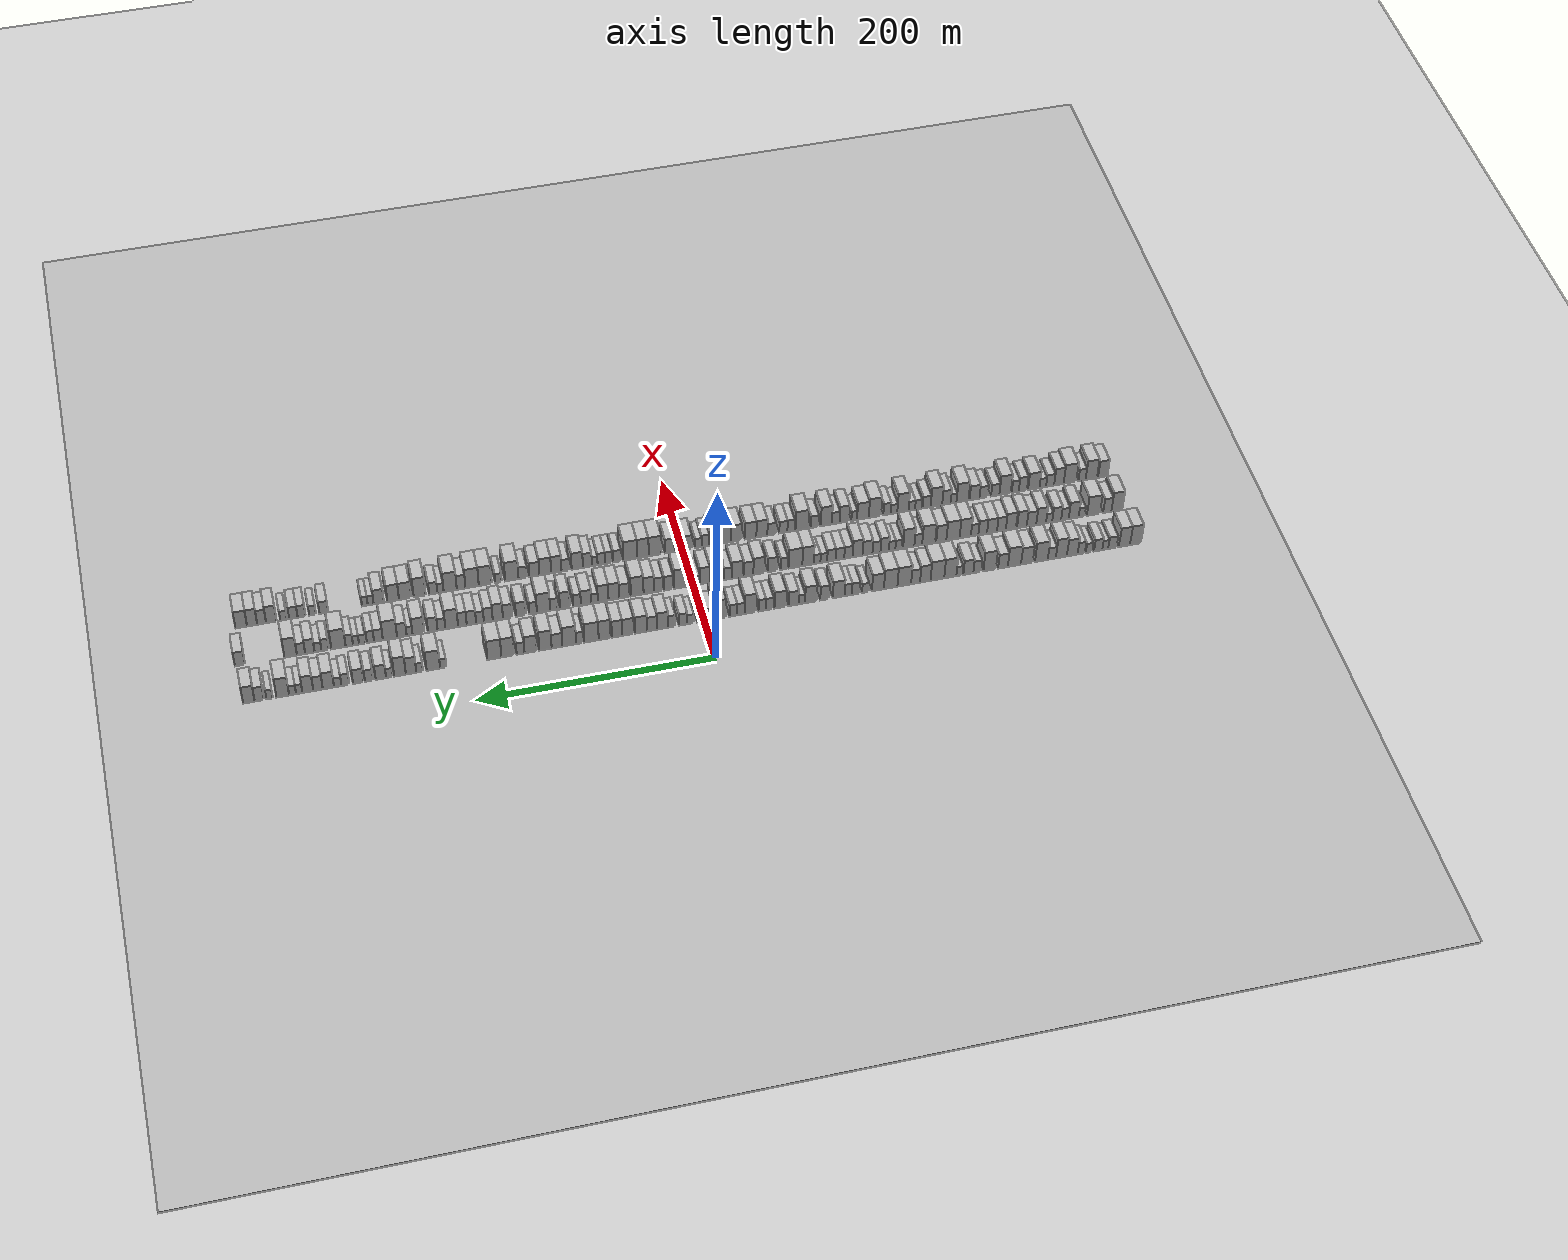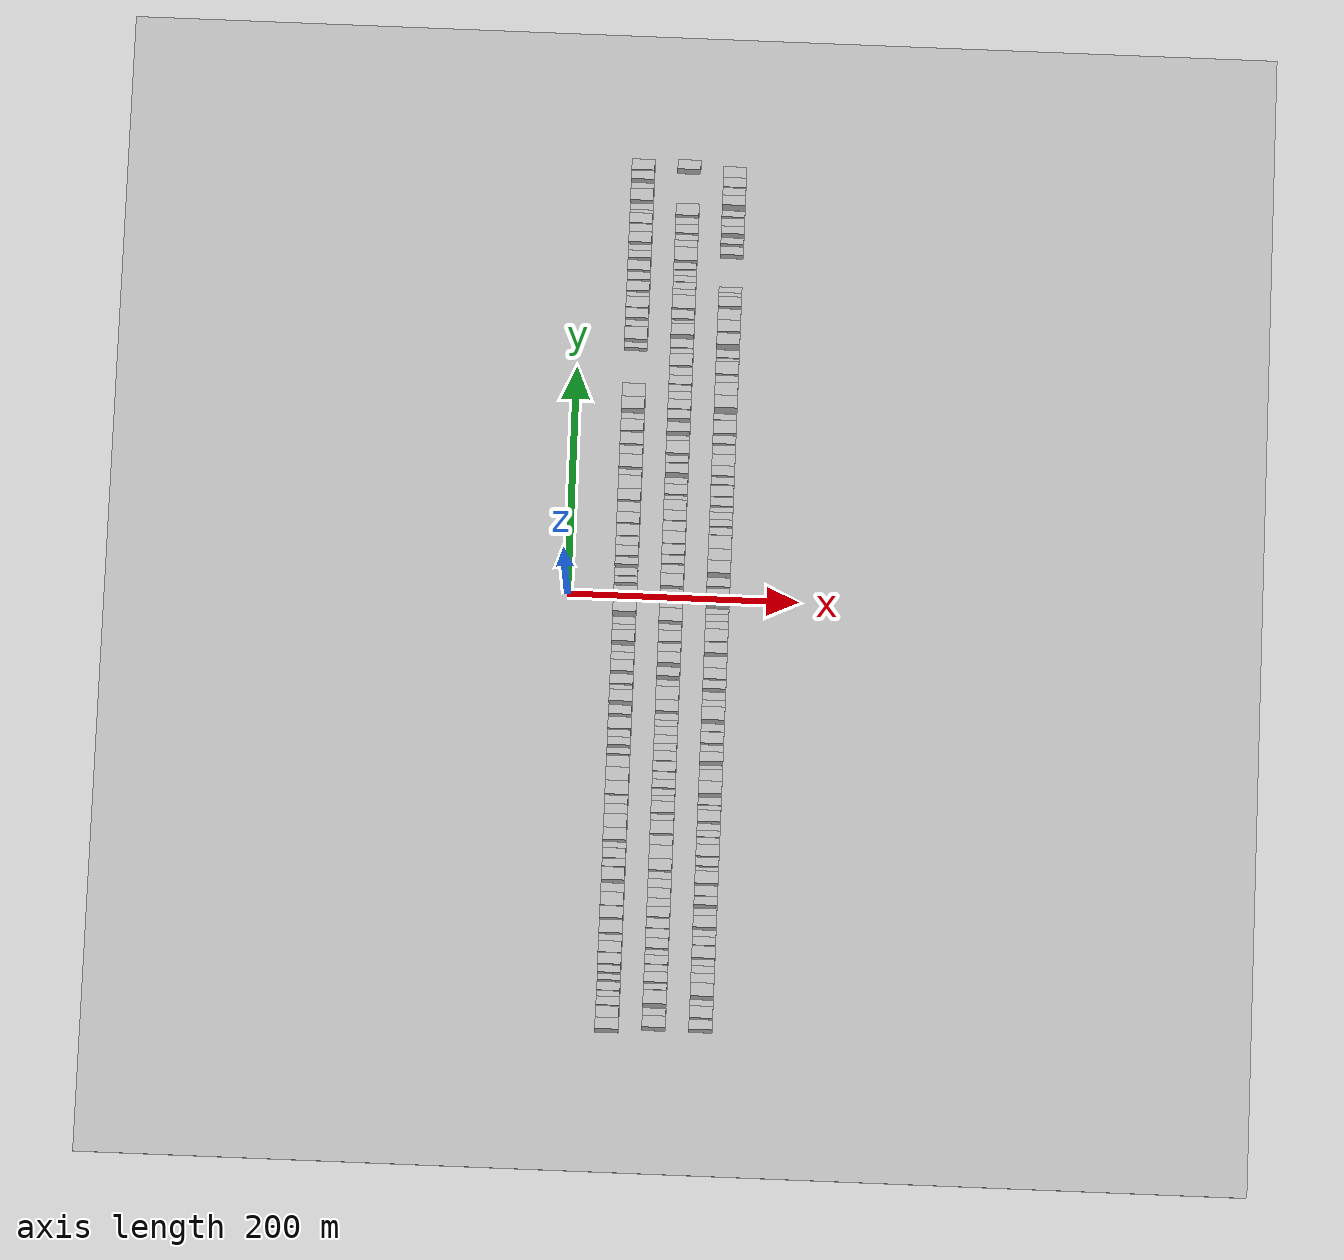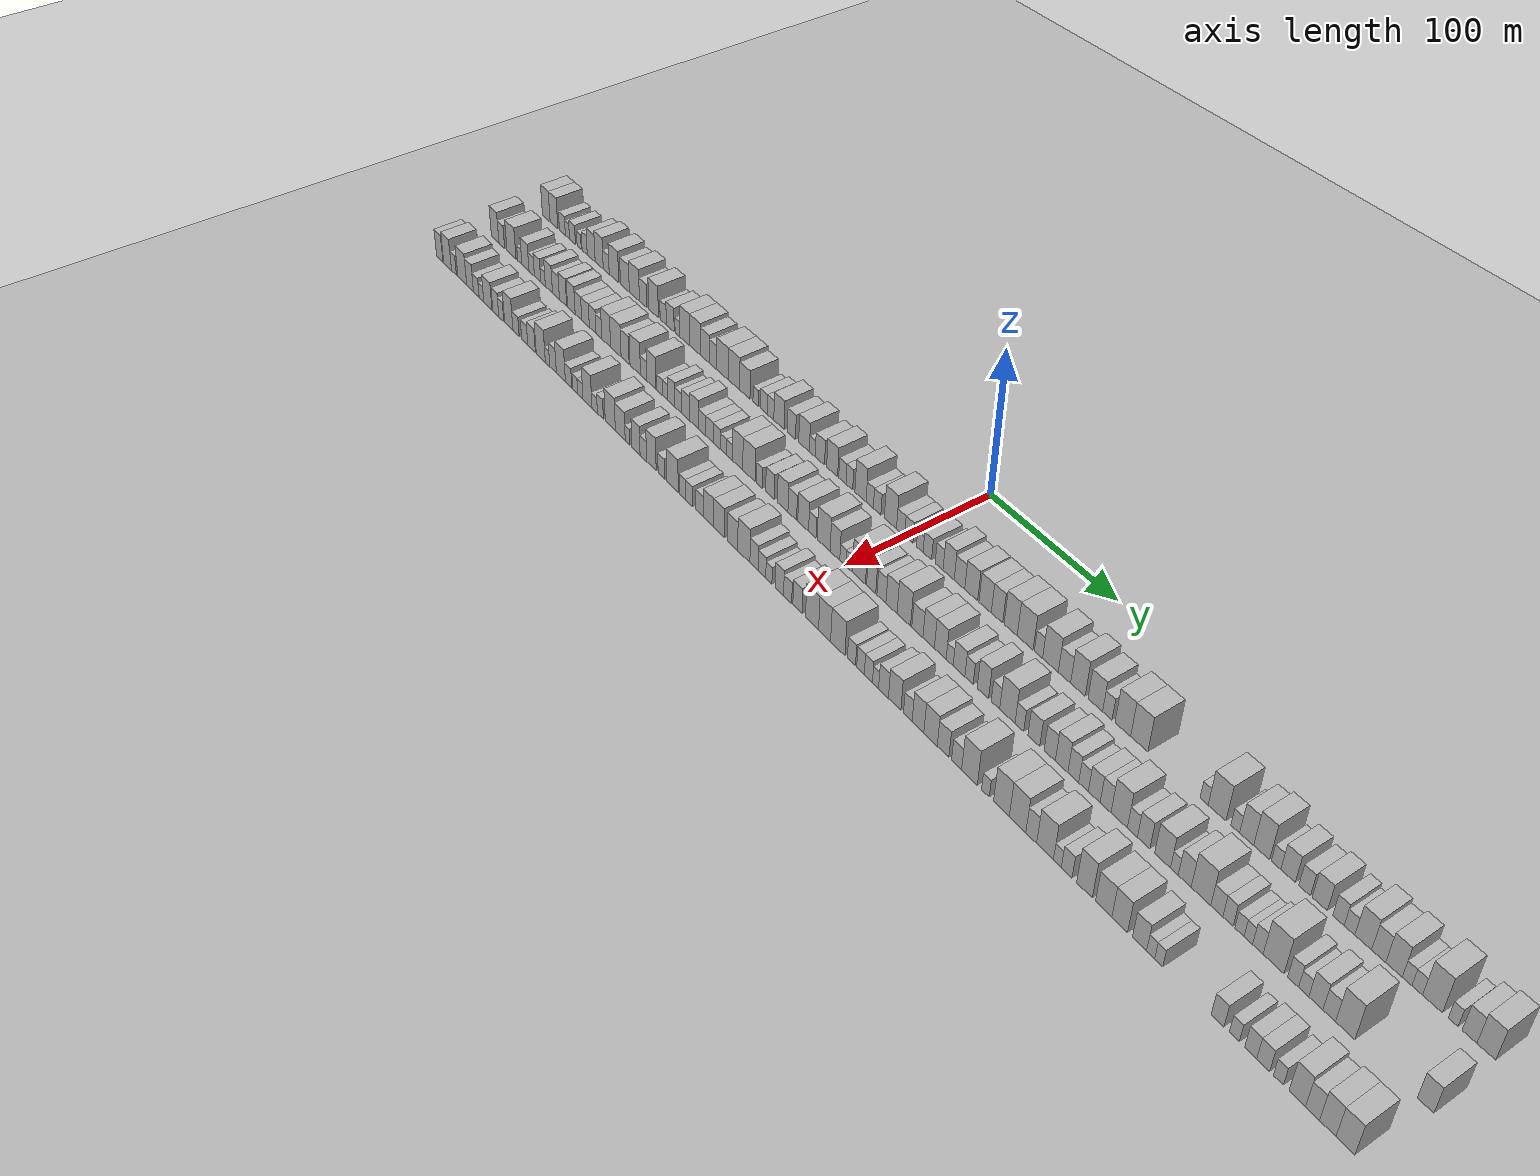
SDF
<?xml version="1.0" encoding="utf-8"?>

<sdf version="1.6">

   <world name="default">

      <gui fullscreen="0">

         <camera name="user_camera">

            <pose>-15 0 4.57585 0 0 0</pose>

            <view_controller>orbit</view_controller>

         </camera>

      </gui>

      <scene>

         <sky>

           <clouds>

             <speed>12</speed>

           </clouds>

         </sky>

         <ambient>0.4 0.4 0.4 1</ambient>

         <background>0.7 0.7 0.7 1</background>

         <shadows>1</shadows>

      </scene>

      <gravity>0 0 -9.8066</gravity>

      <magnetic_field>6e-06 2.3e-05 -4.2e-05</magnetic_field>

      <physics default="0" name="default_physics" type="ode">

         <ode>

            <solver>

               <type>quick</type>

               <iters>10</iters>

               <sor>1.0</sor>

               <use_dynamic_moi_rescaling>0</use_dynamic_moi_rescaling>

            </solver>

            <constraints>

               <cfm>0</cfm>

               <erp>0.2</erp>

               <contact_max_correcting_vel>100</contact_max_correcting_vel>

               <contact_surface_layer>0.001</contact_surface_layer>

            </constraints>

         </ode>

         <max_step_size>0.004</max_step_size>

         <real_time_factor>1</real_time_factor>

         <real_time_update_rate>250</real_time_update_rate>

      </physics>

      <light name="sun" type="directional">

         <cast_shadows>1</cast_shadows>

         <pose>0 0 10 0 0 0</pose>

         <diffuse>0.8 0.8 0.8 1</diffuse>

         <specular>0.2 0.2 0.2 1</specular>

         <attenuation>

            <range>1000</range>

            <constant>0.9</constant>

            <linear>0.01</linear>

            <quadratic>0.001</quadratic>

         </attenuation>

         <direction>-0.5 0.1 -0.9</direction>

      </light>

      <include>

         <name>ground_plane_1</name>

         <uri>model://HANNAS_ground_plane</uri>

         <pose>0 0 0  0 0 0</pose>

      </include>

      <include>

         <name>ground_plane_2</name>

         <uri>model://HANNAS_ground_plane</uri>

         <pose>100 0 0  0 0 0</pose>

      </include>

      <model name="building_1">

         <static>1</static>

         <pose frame="">50.0000 -375.1057 0 0.000000 0.000000 0.000000</pose>

         <link name="link">

            <pose frame="">0 0 12.00 0 0 0</pose>

            <collision name="collision">

               <geometry>

                  <box>

                     <size>20.0000 9.7886 24.0000</size>

                  </box>

               </geometry>

               <max_contacts>10</max_contacts>

               <surface>

                  <contact>

                     <ode/>

                  </contact>

                  <bounce/>

                  <friction>

                     <torsional>

                        <ode/>

                     </torsional>

                     <ode/>

                  </friction>

               </surface>

            </collision>

            <visual name="visual">

               <cast_shadows>0</cast_shadows>

               <geometry>

                  <box>

                     <size>20.0000 9.7886 24.0000</size>

                  </box>

               </geometry>

               <material>

                  <script>

                     <uri>model://HANNAS_wall/materials/scripts</uri>

                     <uri>model://HANNAS_wall/materials/textures</uri>

                     <name>vrc/HANNAS_wall</name>

                  </script>

               </material>

            </visual>

            <self_collide>0</self_collide>

            <enable_wind>0</enable_wind>

            <kinematic>0</kinematic>

         </link>

      </model>

      <model name="building_2">

         <static>1</static>

         <pose frame="">50.0000 -365.2573 0 0.000000 0.000000 0.000000</pose>

         <link name="link">

            <pose frame="">0 0 12.00 0 0 0</pose>

            <collision name="collision">

               <geometry>

                  <box>

                     <size>20.0000 9.9081 24.0000</size>

                  </box>

               </geometry>

               <max_contacts>10</max_contacts>

               <surface>

                  <contact>

                     <ode/>

                  </contact>

                  <bounce/>

                  <friction>

                     <torsional>

                        <ode/>

                     </torsional>

                     <ode/>

                  </friction>

               </surface>

            </collision>

            <visual name="visual">

               <cast_shadows>0</cast_shadows>

               <geometry>

                  <box>

                     <size>20.0000 9.9081 24.0000</size>

                  </box>

               </geometry>

               <material>

                  <script>

                     <uri>model://HANNAS_wall/materials/scripts</uri>

                     <uri>model://HANNAS_wall/materials/textures</uri>

                     <name>vrc/HANNAS_wall</name>

                  </script>

               </material>

            </visual>

            <self_collide>0</self_collide>

            <enable_wind>0</enable_wind>

            <kinematic>0</kinematic>

         </link>

      </model>

      <model name="building_3">

         <static>1</static>

         <pose frame="">50.0000 -354.5814 0 0.000000 0.000000 0.000000</pose>

         <link name="link">

            <pose frame="">0 0 7.50 0 0 0</pose>

            <collision name="collision">

               <geometry>

                  <box>

                     <size>20.0000 7.4438 15.0000</size>

                  </box>

               </geometry>

               <max_contacts>10</max_contacts>

               <surface>

                  <contact>

                     <ode/>

                  </contact>

                  <bounce/>

                  <friction>

                     <torsional>

                        <ode/>

                     </torsional>

                     <ode/>

                  </friction>

               </surface>

            </collision>

            <visual name="visual">

               <cast_shadows>0</cast_shadows>

               <geometry>

                  <box>

                     <size>20.0000 7.4438 15.0000</size>

                  </box>

               </geometry>

               <material>

                  <script>

                     <uri>model://HANNAS_wall/materials/scripts</uri>

                     <uri>model://HANNAS_wall/materials/textures</uri>

                     <name>vrc/HANNAS_wall</name>

                  </script>

               </material>

            </visual>

            <self_collide>0</self_collide>

            <enable_wind>0</enable_wind>

            <kinematic>0</kinematic>

         </link>

      </model>

      <model name="building_4">

         <static>1</static>

         <pose frame="">50.0000 -348.2421 0 0.000000 0.000000 0.000000</pose>

         <link name="link">

            <pose frame="">0 0 6.00 0 0 0</pose>

            <collision name="collision">

               <geometry>

                  <box>

                     <size>20.0000 5.2347 12.0000</size>

                  </box>

               </geometry>

               <max_contacts>10</max_contacts>

               <surface>

                  <contact>

                     <ode/>

                  </contact>

                  <bounce/>

                  <friction>

                     <torsional>

                        <ode/>

                     </torsional>

                     <ode/>

                  </friction>

               </surface>

            </collision>

            <visual name="visual">

               <cast_shadows>0</cast_shadows>

               <geometry>

                  <box>

                     <size>20.0000 5.2347 12.0000</size>

                  </box>

               </geometry>

               <material>

                  <script>

                     <uri>model://HANNAS_wall/materials/scripts</uri>

                     <uri>model://HANNAS_wall/materials/textures</uri>

                     <name>vrc/HANNAS_wall</name>

                  </script>

               </material>

            </visual>

            <self_collide>0</self_collide>

            <enable_wind>0</enable_wind>

            <kinematic>0</kinematic>

         </link>

      </model>

      <model name="building_5">

         <static>1</static>

         <pose frame="">50.0000 -341.9322 0 0.000000 0.000000 0.000000</pose>

         <link name="link">

            <pose frame="">0 0 7.50 0 0 0</pose>

            <collision name="collision">

               <geometry>

                  <box>

                     <size>20.0000 7.3851 15.0000</size>

                  </box>

               </geometry>

               <max_contacts>10</max_contacts>

               <surface>

                  <contact>

                     <ode/>

                  </contact>

                  <bounce/>

                  <friction>

                     <torsional>

                        <ode/>

                     </torsional>

                     <ode/>

                  </friction>

               </surface>

            </collision>

            <visual name="visual">

               <cast_shadows>0</cast_shadows>

               <geometry>

                  <box>

                     <size>20.0000 7.3851 15.0000</size>

                  </box>

               </geometry>

               <material>

                  <script>

                     <uri>model://HANNAS_wall/materials/scripts</uri>

                     <uri>model://HANNAS_wall/materials/textures</uri>

                     <name>vrc/HANNAS_wall</name>

                  </script>

               </material>

            </visual>

            <self_collide>0</self_collide>

            <enable_wind>0</enable_wind>

            <kinematic>0</kinematic>

         </link>

      </model>

      <model name="building_6">

         <static>1</static>

         <pose frame="">50.0000 -333.6332 0 0.000000 0.000000 0.000000</pose>

         <link name="link">

            <pose frame="">0 0 6.00 0 0 0</pose>

            <collision name="collision">

               <geometry>

                  <box>

                     <size>20.0000 5.2130 12.0000</size>

                  </box>

               </geometry>

               <max_contacts>10</max_contacts>

               <surface>

                  <contact>

                     <ode/>

                  </contact>

                  <bounce/>

                  <friction>

                     <torsional>

                        <ode/>

                     </torsional>

                     <ode/>

                  </friction>

               </surface>

            </collision>

            <visual name="visual">

               <cast_shadows>0</cast_shadows>

               <geometry>

                  <box>

                     <size>20.0000 5.2130 12.0000</size>

                  </box>

               </geometry>

               <material>

                  <script>

                     <uri>model://HANNAS_wall/materials/scripts</uri>

                     <uri>model://HANNAS_wall/materials/textures</uri>

                     <name>vrc/HANNAS_wall</name>

                  </script>

               </material>

            </visual>

            <self_collide>0</self_collide>

            <enable_wind>0</enable_wind>

            <kinematic>0</kinematic>

         </link>

      </model>

      <model name="building_7">

         <static>1</static>

         <pose frame="">50.0000 -326.8736 0 0.000000 0.000000 0.000000</pose>

         <link name="link">

            <pose frame="">0 0 7.50 0 0 0</pose>

            <collision name="collision">

               <geometry>

                  <box>

                     <size>20.0000 6.3061 15.0000</size>

                  </box>

               </geometry>

               <max_contacts>10</max_contacts>

               <surface>

                  <contact>

                     <ode/>

                  </contact>

                  <bounce/>

                  <friction>

                     <torsional>

                        <ode/>

                     </torsional>

                     <ode/>

                  </friction>

               </surface>

            </collision>

            <visual name="visual">

               <cast_shadows>0</cast_shadows>

               <geometry>

                  <box>

                     <size>20.0000 6.3061 15.0000</size>

                  </box>

               </geometry>

               <material>

                  <script>

                     <uri>model://HANNAS_wall/materials/scripts</uri>

                     <uri>model://HANNAS_wall/materials/textures</uri>

                     <name>vrc/HANNAS_wall</name>

                  </script>

               </material>

            </visual>

            <self_collide>0</self_collide>

            <enable_wind>0</enable_wind>

            <kinematic>0</kinematic>

         </link>

      </model>

      <model name="building_8">

         <static>1</static>

         <pose frame="">50.0000 -318.9188 0 0.000000 0.000000 0.000000</pose>

         <link name="link">

            <pose frame="">0 0 10.50 0 0 0</pose>

            <collision name="collision">

               <geometry>

                  <box>

                     <size>20.0000 9.6036 21.0000</size>

                  </box>

               </geometry>

               <max_contacts>10</max_contacts>

               <surface>

                  <contact>

                     <ode/>

                  </contact>

                  <bounce/>

                  <friction>

                     <torsional>

                        <ode/>

                     </torsional>

                     <ode/>

                  </friction>

               </surface>

            </collision>

            <visual name="visual">

               <cast_shadows>0</cast_shadows>

               <geometry>

                  <box>

                     <size>20.0000 9.6036 21.0000</size>

                  </box>

               </geometry>

               <material>

                  <script>

                     <uri>model://HANNAS_wall/materials/scripts</uri>

                     <uri>model://HANNAS_wall/materials/textures</uri>

                     <name>vrc/HANNAS_wall</name>

                  </script>

               </material>

            </visual>

            <self_collide>0</self_collide>

            <enable_wind>0</enable_wind>

            <kinematic>0</kinematic>

         </link>

      </model>

      <model name="building_9">

         <static>1</static>

         <pose frame="">50.0000 -309.2327 0 0.000000 0.000000 0.000000</pose>

         <link name="link">

            <pose frame="">0 0 12.00 0 0 0</pose>

            <collision name="collision">

               <geometry>

                  <box>

                     <size>20.0000 9.7687 24.0000</size>

                  </box>

               </geometry>

               <max_contacts>10</max_contacts>

               <surface>

                  <contact>

                     <ode/>

                  </contact>

                  <bounce/>

                  <friction>

                     <torsional>

                        <ode/>

                     </torsional>

                     <ode/>

                  </friction>

               </surface>

            </collision>

            <visual name="visual">

               <cast_shadows>0</cast_shadows>

               <geometry>

                  <box>

                     <size>20.0000 9.7687 24.0000</size>

                  </box>

               </geometry>

               <material>

                  <script>

                     <uri>model://HANNAS_wall/materials/scripts</uri>

                     <uri>model://HANNAS_wall/materials/textures</uri>

                     <name>vrc/HANNAS_wall</name>

                  </script>

               </material>

            </visual>

            <self_collide>0</self_collide>

            <enable_wind>0</enable_wind>

            <kinematic>0</kinematic>

         </link>

      </model>

      <model name="building_10">

         <static>1</static>

         <pose frame="">50.0000 -300.8077 0 0.000000 0.000000 0.000000</pose>

         <link name="link">

            <pose frame="">0 0 7.50 0 0 0</pose>

            <collision name="collision">

               <geometry>

                  <box>

                     <size>20.0000 7.0812 15.0000</size>

                  </box>

               </geometry>

               <max_contacts>10</max_contacts>

               <surface>

                  <contact>

                     <ode/>

                  </contact>

                  <bounce/>

                  <friction>

                     <torsional>

                        <ode/>

                     </torsional>

                     <ode/>

                  </friction>

               </surface>

            </collision>

            <visual name="visual">

               <cast_shadows>0</cast_shadows>

               <geometry>

                  <box>

                     <size>20.0000 7.0812 15.0000</size>

                  </box>

               </geometry>

               <material>

                  <script>

                     <uri>model://HANNAS_wall/materials/scripts</uri>

                     <uri>model://HANNAS_wall/materials/textures</uri>

                     <name>vrc/HANNAS_wall</name>

                  </script>

               </material>

            </visual>

            <self_collide>0</self_collide>

            <enable_wind>0</enable_wind>

            <kinematic>0</kinematic>

         </link>

      </model>

      <model name="building_11">

         <static>1</static>

         <pose frame="">50.0000 -291.6061 0 0.000000 0.000000 0.000000</pose>

         <link name="link">

            <pose frame="">0 0 12.00 0 0 0</pose>

            <collision name="collision">

               <geometry>

                  <box>

                     <size>20.0000 11.3220 24.0000</size>

                  </box>

               </geometry>

               <max_contacts>10</max_contacts>

               <surface>

                  <contact>

                     <ode/>

                  </contact>

                  <bounce/>

                  <friction>

                     <torsional>

                        <ode/>

                     </torsional>

                     <ode/>

                  </friction>

               </surface>

            </collision>

            <visual name="visual">

               <cast_shadows>0</cast_shadows>

               <geometry>

                  <box>

                     <size>20.0000 11.3220 24.0000</size>

                  </box>

               </geometry>

               <material>

                  <script>

                     <uri>model://HANNAS_wall/materials/scripts</uri>

                     <uri>model://HANNAS_wall/materials/textures</uri>

                     <name>vrc/HANNAS_wall</name>

                  </script>

               </material>

            </visual>

            <self_collide>0</self_collide>

            <enable_wind>0</enable_wind>

            <kinematic>0</kinematic>

         </link>

      </model>

      <model name="building_12">

         <static>1</static>

         <pose frame="">50.0000 -278.7945 0 0.000000 0.000000 0.000000</pose>

         <link name="link">

            <pose frame="">0 0 10.50 0 0 0</pose>

            <collision name="collision">

               <geometry>

                  <box>

                     <size>20.0000 10.3011 21.0000</size>

                  </box>

               </geometry>

               <max_contacts>10</max_contacts>

               <surface>

                  <contact>

                     <ode/>

                  </contact>

                  <bounce/>

                  <friction>

                     <torsional>

                        <ode/>

                     </torsional>

                     <ode/>

                  </friction>

               </surface>

            </collision>

            <visual name="visual">

               <cast_shadows>0</cast_shadows>

               <geometry>

                  <box>

                     <size>20.0000 10.3011 21.0000</size>

                  </box>

               </geometry>

               <material>

                  <script>

                     <uri>model://HANNAS_wall/materials/scripts</uri>

                     <uri>model://HANNAS_wall/materials/textures</uri>

                     <name>vrc/HANNAS_wall</name>

                  </script>

               </material>

            </visual>

            <self_collide>0</self_collide>

            <enable_wind>0</enable_wind>

            <kinematic>0</kinematic>

         </link>

      </model>

      <model name="building_13">

         <static>1</static>

         <pose frame="">50.0000 -267.8266 0 0.000000 0.000000 0.000000</pose>

         <link name="link">

            <pose frame="">0 0 12.00 0 0 0</pose>

            <collision name="collision">

               <geometry>

                  <box>

                     <size>20.0000 11.6347 24.0000</size>

                  </box>

               </geometry>

               <max_contacts>10</max_contacts>

               <surface>

                  <contact>

                     <ode/>

                  </contact>

                  <bounce/>

                  <friction>

                     <torsional>

                        <ode/>

                     </torsional>

                     <ode/>

                  </friction>

               </surface>

            </collision>

            <visual name="visual">

               <cast_shadows>0</cast_shadows>

               <geometry>

                  <box>

                     <size>20.0000 11.6347 24.0000</size>

                  </box>

               </geometry>

               <material>

                  <script>

                     <uri>model://HANNAS_wall/materials/scripts</uri>

                     <uri>model://HANNAS_wall/materials/textures</uri>

                     <name>vrc/HANNAS_wall</name>

                  </script>

               </material>

            </visual>

            <self_collide>0</self_collide>

            <enable_wind>0</enable_wind>

            <kinematic>0</kinematic>

         </link>

      </model>

      <model name="building_14">

         <static>1</static>

         <pose frame="">50.0000 -257.7318 0 0.000000 0.000000 0.000000</pose>

         <link name="link">

            <pose frame="">0 0 9.00 0 0 0</pose>

            <collision name="collision">

               <geometry>

                  <box>

                     <size>20.0000 8.5549 18.0000</size>

                  </box>

               </geometry>

               <max_contacts>10</max_contacts>

               <surface>

                  <contact>

                     <ode/>

                  </contact>

                  <bounce/>

                  <friction>

                     <torsional>

                        <ode/>

                     </torsional>

                     <ode/>

                  </friction>

               </surface>

            </collision>

            <visual name="visual">

               <cast_shadows>0</cast_shadows>

               <geometry>

                  <box>

                     <size>20.0000 8.5549 18.0000</size>

                  </box>

               </geometry>

               <material>

                  <script>

                     <uri>model://HANNAS_wall/materials/scripts</uri>

                     <uri>model://HANNAS_wall/materials/textures</uri>

                     <name>vrc/HANNAS_wall</name>

                  </script>

               </material>

            </visual>

            <self_collide>0</self_collide>

            <enable_wind>0</enable_wind>

            <kinematic>0</kinematic>

         </link>

      </model>

      <model name="building_15">

         <static>1</static>

         <pose frame="">50.0000 -245.9967 0 0.000000 0.000000 0.000000</pose>

         <link name="link">

            <pose frame="">0 0 12.00 0 0 0</pose>

            <collision name="collision">

               <geometry>

                  <box>

                     <size>20.0000 10.9153 24.0000</size>

                  </box>

               </geometry>

               <max_contacts>10</max_contacts>

               <surface>

                  <contact>

                     <ode/>

                  </contact>

                  <bounce/>

                  <friction>

                     <torsional>

                        <ode/>

                     </torsional>

                     <ode/>

                  </friction>

               </surface>

            </collision>

            <visual name="visual">

               <cast_shadows>0</cast_shadows>

               <geometry>

                  <box>

                     <size>20.0000 10.9153 24.0000</size>

                  </box>

               </geometry>

               <material>

                  <script>

                     <uri>model://HANNAS_wall/materials/scripts</uri>

                     <uri>model://HANNAS_wall/materials/textures</uri>

                     <name>vrc/HANNAS_wall</name>

                  </script>

               </material>

            </visual>

            <self_collide>0</self_collide>

            <enable_wind>0</enable_wind>

            <kinematic>0</kinematic>

         </link>

      </model>

      <model name="building_16">

         <static>1</static>

         <pose frame="">50.0000 -235.1256 0 0.000000 0.000000 0.000000</pose>

         <link name="link">

            <pose frame="">0 0 7.50 0 0 0</pose>

            <collision name="collision">

               <geometry>

                  <box>

                     <size>20.0000 6.8268 15.0000</size>

                  </box>

               </geometry>

               <max_contacts>10</max_contacts>

               <surface>

                  <contact>

                     <ode/>

                  </contact>

                  <bounce/>

                  <friction>

                     <torsional>

                        <ode/>

                     </torsional>

                     <ode/>

                  </friction>

               </surface>

            </collision>

            <visual name="visual">

               <cast_shadows>0</cast_shadows>

               <geometry>

                  <box>

                     <size>20.0000 6.8268 15.0000</size>

                  </box>

               </geometry>

               <material>

                  <script>

                     <uri>model://HANNAS_wall/materials/scripts</uri>

                     <uri>model://HANNAS_wall/materials/textures</uri>

                     <name>vrc/HANNAS_wall</name>

                  </script>

               </material>

            </visual>

            <self_collide>0</self_collide>

            <enable_wind>0</enable_wind>

            <kinematic>0</kinematic>

         </link>

      </model>

      <model name="building_17">

         <static>1</static>

         <pose frame="">50.0000 -227.3693 0 0.000000 0.000000 0.000000</pose>

         <link name="link">

            <pose frame="">0 0 9.00 0 0 0</pose>

            <collision name="collision">

               <geometry>

                  <box>

                     <size>20.0000 8.6857 18.0000</size>

                  </box>

               </geometry>

               <max_contacts>10</max_contacts>

               <surface>

                  <contact>

                     <ode/>

                  </contact>

                  <bounce/>

                  <friction>

                     <torsional>

                        <ode/>

                     </torsional>

                     <ode/>

                  </friction>

               </surface>

            </collision>

            <visual name="visual">

               <cast_shadows>0</cast_shadows>

               <geometry>

                  <box>

                     <size>20.0000 8.6857 18.0000</size>

                  </box>

               </geometry>

               <material>

                  <script>

                     <uri>model://HANNAS_wall/materials/scripts</uri>

                     <uri>model://HANNAS_wall/materials/textures</uri>

                     <name>vrc/HANNAS_wall</name>

                  </script>

               </material>

            </visual>

            <self_collide>0</self_collide>

            <enable_wind>0</enable_wind>

            <kinematic>0</kinematic>

         </link>

      </model>

      <model name="building_18">

         <static>1</static>

         <pose frame="">50.0000 -219.4277 0 0.000000 0.000000 0.000000</pose>

         <link name="link">

            <pose frame="">0 0 6.00 0 0 0</pose>

            <collision name="collision">

               <geometry>

                  <box>

                     <size>20.0000 5.1975 12.0000</size>

                  </box>

               </geometry>

               <max_contacts>10</max_contacts>

               <surface>

                  <contact>

                     <ode/>

                  </contact>

                  <bounce/>

                  <friction>

                     <torsional>

                        <ode/>

                     </torsional>

                     <ode/>

                  </friction>

               </surface>

            </collision>

            <visual name="visual">

               <cast_shadows>0</cast_shadows>

               <geometry>

                  <box>

                     <size>20.0000 5.1975 12.0000</size>

                  </box>

               </geometry>

               <material>

                  <script>

                     <uri>model://HANNAS_wall/materials/scripts</uri>

                     <uri>model://HANNAS_wall/materials/textures</uri>

                     <name>vrc/HANNAS_wall</name>

                  </script>

               </material>

            </visual>

            <self_collide>0</self_collide>

            <enable_wind>0</enable_wind>

            <kinematic>0</kinematic>

         </link>

      </model>

      <model name="building_19">

         <static>1</static>

         <pose frame="">50.0000 -211.5159 0 0.000000 0.000000 0.000000</pose>

         <link name="link">

            <pose frame="">0 0 12.00 0 0 0</pose>

            <collision name="collision">

               <geometry>

                  <box>

                     <size>20.0000 10.6261 24.0000</size>

                  </box>

               </geometry>

               <max_contacts>10</max_contacts>

               <surface>

                  <contact>

                     <ode/>

                  </contact>

                  <bounce/>

                  <friction>

                     <torsional>

                        <ode/>

                     </torsional>

                     <ode/>

                  </friction>

               </surface>

            </collision>

            <visual name="visual">

               <cast_shadows>0</cast_shadows>

               <geometry>

                  <box>

                     <size>20.0000 10.6261 24.0000</size>

                  </box>

               </geometry>

               <material>

                  <script>

                     <uri>model://HANNAS_wall/materials/scripts</uri>

                     <uri>model://HANNAS_wall/materials/textures</uri>

                     <name>vrc/HANNAS_wall</name>

                  </script>

               </material>

            </visual>

            <self_collide>0</self_collide>

            <enable_wind>0</enable_wind>

            <kinematic>0</kinematic>

         </link>

      </model>

      <model name="building_20">

         <static>1</static>

         <pose frame="">50.0000 -200.2284 0 0.000000 0.000000 0.000000</pose>

         <link name="link">

            <pose frame="">0 0 12.00 0 0 0</pose>

            <collision name="collision">

               <geometry>

                  <box>

                     <size>20.0000 11.9489 24.0000</size>

                  </box>

               </geometry>

               <max_contacts>10</max_contacts>

               <surface>

                  <contact>

                     <ode/>

                  </contact>

                  <bounce/>

                  <friction>

                     <torsional>

                        <ode/>

                     </torsional>

                     <ode/>

                  </friction>

               </surface>

            </collision>

            <visual name="visual">

               <cast_shadows>0</cast_shadows>

               <geometry>

                  <box>

                     <size>20.0000 11.9489 24.0000</size>

                  </box>

               </geometry>

               <material>

                  <script>

                     <uri>model://HANNAS_wall/materials/scripts</uri>

                     <uri>model://HANNAS_wall/materials/textures</uri>

                     <name>vrc/HANNAS_wall</name>

                  </script>

               </material>

            </visual>

            <self_collide>0</self_collide>

            <enable_wind>0</enable_wind>

            <kinematic>0</kinematic>

         </link>

      </model>

      <model name="building_21">

         <static>1</static>

         <pose frame="">50.0000 -189.6851 0 0.000000 0.000000 0.000000</pose>

         <link name="link">

            <pose frame="">0 0 10.50 0 0 0</pose>

            <collision name="collision">

               <geometry>

                  <box>

                     <size>20.0000 9.1375 21.0000</size>

                  </box>

               </geometry>

               <max_contacts>10</max_contacts>

               <surface>

                  <contact>

                     <ode/>

                  </contact>

                  <bounce/>

                  <friction>

                     <torsional>

                        <ode/>

                     </torsional>

                     <ode/>

                  </friction>

               </surface>

            </collision>

            <visual name="visual">

               <cast_shadows>0</cast_shadows>

               <geometry>

                  <box>

                     <size>20.0000 9.1375 21.0000</size>

                  </box>

               </geometry>

               <material>

                  <script>

                     <uri>model://HANNAS_wall/materials/scripts</uri>

                     <uri>model://HANNAS_wall/materials/textures</uri>

                     <name>vrc/HANNAS_wall</name>

                  </script>

               </material>

            </visual>

            <self_collide>0</self_collide>

            <enable_wind>0</enable_wind>

            <kinematic>0</kinematic>

         </link>

      </model>

      <model name="building_22">

         <static>1</static>

         <pose frame="">50.0000 -181.2218 0 0.000000 0.000000 0.000000</pose>

         <link name="link">

            <pose frame="">0 0 9.00 0 0 0</pose>

            <collision name="collision">

               <geometry>

                  <box>

                     <size>20.0000 7.7893 18.0000</size>

                  </box>

               </geometry>

               <max_contacts>10</max_contacts>

               <surface>

                  <contact>

                     <ode/>

                  </contact>

                  <bounce/>

                  <friction>

                     <torsional>

                        <ode/>

                     </torsional>

                     <ode/>

                  </friction>

               </surface>

            </collision>

            <visual name="visual">

               <cast_shadows>0</cast_shadows>

               <geometry>

                  <box>

                     <size>20.0000 7.7893 18.0000</size>

                  </box>

               </geometry>

               <material>

                  <script>

                     <uri>model://HANNAS_wall/materials/scripts</uri>

                     <uri>model://HANNAS_wall/materials/textures</uri>

                     <name>vrc/HANNAS_wall</name>

                  </script>

               </material>

            </visual>

            <self_collide>0</self_collide>

            <enable_wind>0</enable_wind>

            <kinematic>0</kinematic>

         </link>

      </model>

      <model name="building_23">

         <static>1</static>

         <pose frame="">50.0000 -171.3598 0 0.000000 0.000000 0.000000</pose>

         <link name="link">

            <pose frame="">0 0 12.00 0 0 0</pose>

            <collision name="collision">

               <geometry>

                  <box>

                     <size>20.0000 11.9347 24.0000</size>

                  </box>

               </geometry>

               <max_contacts>10</max_contacts>

               <surface>

                  <contact>

                     <ode/>

                  </contact>

                  <bounce/>

                  <friction>

                     <torsional>

                        <ode/>

                     </torsional>

                     <ode/>

                  </friction>

               </surface>

            </collision>

            <visual name="visual">

               <cast_shadows>0</cast_shadows>

               <geometry>

                  <box>

                     <size>20.0000 11.9347 24.0000</size>

                  </box>

               </geometry>

               <material>

                  <script>

                     <uri>model://HANNAS_wall/materials/scripts</uri>

                     <uri>model://HANNAS_wall/materials/textures</uri>

                     <name>vrc/HANNAS_wall</name>

                  </script>

               </material>

            </visual>

            <self_collide>0</self_collide>

            <enable_wind>0</enable_wind>

            <kinematic>0</kinematic>

         </link>

      </model>

      <model name="building_24">

         <static>1</static>

         <pose frame="">50.0000 -159.5305 0 0.000000 0.000000 0.000000</pose>

         <link name="link">

            <pose frame="">0 0 12.00 0 0 0</pose>

            <collision name="collision">

               <geometry>

                  <box>

                     <size>20.0000 11.7240 24.0000</size>

                  </box>

               </geometry>

               <max_contacts>10</max_contacts>

               <surface>

                  <contact>

                     <ode/>

                  </contact>

                  <bounce/>

                  <friction>

                     <torsional>

                        <ode/>

                     </torsional>

                     <ode/>

                  </friction>

               </surface>

            </collision>

            <visual name="visual">

               <cast_shadows>0</cast_shadows>

               <geometry>

                  <box>

                     <size>20.0000 11.7240 24.0000</size>

                  </box>

               </geometry>

               <material>

                  <script>

                     <uri>model://HANNAS_wall/materials/scripts</uri>

                     <uri>model://HANNAS_wall/materials/textures</uri>

                     <name>vrc/HANNAS_wall</name>

                  </script>

               </material>

            </visual>

            <self_collide>0</self_collide>

            <enable_wind>0</enable_wind>

            <kinematic>0</kinematic>

         </link>

      </model>

      <model name="building_25">

         <static>1</static>

         <pose frame="">50.0000 -148.4868 0 0.000000 0.000000 0.000000</pose>

         <link name="link">

            <pose frame="">0 0 10.50 0 0 0</pose>

            <collision name="collision">

               <geometry>

                  <box>

                     <size>20.0000 10.3634 21.0000</size>

                  </box>

               </geometry>

               <max_contacts>10</max_contacts>

               <surface>

                  <contact>

                     <ode/>

                  </contact>

                  <bounce/>

                  <friction>

                     <torsional>

                        <ode/>

                     </torsional>

                     <ode/>

                  </friction>

               </surface>

            </collision>

            <visual name="visual">

               <cast_shadows>0</cast_shadows>

               <geometry>

                  <box>

                     <size>20.0000 10.3634 21.0000</size>

                  </box>

               </geometry>

               <material>

                  <script>

                     <uri>model://HANNAS_wall/materials/scripts</uri>

                     <uri>model://HANNAS_wall/materials/textures</uri>

                     <name>vrc/HANNAS_wall</name>

                  </script>

               </material>

            </visual>

            <self_collide>0</self_collide>

            <enable_wind>0</enable_wind>

            <kinematic>0</kinematic>

         </link>

      </model>

      <model name="building_26">

         <static>1</static>

         <pose frame="">50.0000 -137.5446 0 0.000000 0.000000 0.000000</pose>

         <link name="link">

            <pose frame="">0 0 6.00 0 0 0</pose>

            <collision name="collision">

               <geometry>

                  <box>

                     <size>20.0000 5.5210 12.0000</size>

                  </box>

               </geometry>

               <max_contacts>10</max_contacts>

               <surface>

                  <contact>

                     <ode/>

                  </contact>

                  <bounce/>

                  <friction>

                     <torsional>

                        <ode/>

                     </torsional>

                     <ode/>

                  </friction>

               </surface>

            </collision>

            <visual name="visual">

               <cast_shadows>0</cast_shadows>

               <geometry>

                  <box>

                     <size>20.0000 5.5210 12.0000</size>

                  </box>

               </geometry>

               <material>

                  <script>

                     <uri>model://HANNAS_wall/materials/scripts</uri>

                     <uri>model://HANNAS_wall/materials/textures</uri>

                     <name>vrc/HANNAS_wall</name>

                  </script>

               </material>

            </visual>

            <self_collide>0</self_collide>

            <enable_wind>0</enable_wind>

            <kinematic>0</kinematic>

         </link>

      </model>

      <model name="building_27">

         <static>1</static>

         <pose frame="">50.0000 -129.3545 0 0.000000 0.000000 0.000000</pose>

         <link name="link">

            <pose frame="">0 0 7.50 0 0 0</pose>

            <collision name="collision">

               <geometry>

                  <box>

                     <size>20.0000 6.8593 15.0000</size>

                  </box>

               </geometry>

               <max_contacts>10</max_contacts>

               <surface>

                  <contact>

                     <ode/>

                  </contact>

                  <bounce/>

                  <friction>

                     <torsional>

                        <ode/>

                     </torsional>

                     <ode/>

                  </friction>

               </surface>

            </collision>

            <visual name="visual">

               <cast_shadows>0</cast_shadows>

               <geometry>

                  <box>

                     <size>20.0000 6.8593 15.0000</size>

                  </box>

               </geometry>

               <material>

                  <script>

                     <uri>model://HANNAS_wall/materials/scripts</uri>

                     <uri>model://HANNAS_wall/materials/textures</uri>

                     <name>vrc/HANNAS_wall</name>

                  </script>

               </material>

            </visual>

            <self_collide>0</self_collide>

            <enable_wind>0</enable_wind>

            <kinematic>0</kinematic>

         </link>

      </model>

      <model name="building_28">

         <static>1</static>

         <pose frame="">50.0000 -122.7703 0 0.000000 0.000000 0.000000</pose>

         <link name="link">

            <pose frame="">0 0 7.50 0 0 0</pose>

            <collision name="collision">

               <geometry>

                  <box>

                     <size>20.0000 6.3090 15.0000</size>

                  </box>

               </geometry>

               <max_contacts>10</max_contacts>

               <surface>

                  <contact>

                     <ode/>

                  </contact>

                  <bounce/>

                  <friction>

                     <torsional>

                        <ode/>

                     </torsional>

                     <ode/>

                  </friction>

               </surface>

            </collision>

            <visual name="visual">

               <cast_shadows>0</cast_shadows>

               <geometry>

                  <box>

                     <size>20.0000 6.3090 15.0000</size>

                  </box>

               </geometry>

               <material>

                  <script>

                     <uri>model://HANNAS_wall/materials/scripts</uri>

                     <uri>model://HANNAS_wall/materials/textures</uri>

                     <name>vrc/HANNAS_wall</name>

                  </script>

               </material>

            </visual>

            <self_collide>0</self_collide>

            <enable_wind>0</enable_wind>

            <kinematic>0</kinematic>

         </link>

      </model>

      <model name="building_29">

         <static>1</static>

         <pose frame="">50.0000 -114.5321 0 0.000000 0.000000 0.000000</pose>

         <link name="link">

            <pose frame="">0 0 10.50 0 0 0</pose>

            <collision name="collision">

               <geometry>

                  <box>

                     <size>20.0000 10.1676 21.0000</size>

                  </box>

               </geometry>

               <max_contacts>10</max_contacts>

               <surface>

                  <contact>

                     <ode/>

                  </contact>

                  <bounce/>

                  <friction>

                     <torsional>

                        <ode/>

                     </torsional>

                     <ode/>

                  </friction>

               </surface>

            </collision>

            <visual name="visual">

               <cast_shadows>0</cast_shadows>

               <geometry>

                  <box>

                     <size>20.0000 10.1676 21.0000</size>

                  </box>

               </geometry>

               <material>

                  <script>

                     <uri>model://HANNAS_wall/materials/scripts</uri>

                     <uri>model://HANNAS_wall/materials/textures</uri>

                     <name>vrc/HANNAS_wall</name>

                  </script>

               </material>

            </visual>

            <self_collide>0</self_collide>

            <enable_wind>0</enable_wind>

            <kinematic>0</kinematic>

         </link>

      </model>

      <model name="building_30">

         <static>1</static>

         <pose frame="">50.0000 -102.5261 0 0.000000 0.000000 0.000000</pose>

         <link name="link">

            <pose frame="">0 0 9.00 0 0 0</pose>

            <collision name="collision">

               <geometry>

                  <box>

                     <size>20.0000 7.8445 18.0000</size>

                  </box>

               </geometry>

               <max_contacts>10</max_contacts>

               <surface>

                  <contact>

                     <ode/>

                  </contact>

                  <bounce/>

                  <friction>

                     <torsional>

                        <ode/>

                     </torsional>

                     <ode/>

                  </friction>

               </surface>

            </collision>

            <visual name="visual">

               <cast_shadows>0</cast_shadows>

               <geometry>

                  <box>

                     <size>20.0000 7.8445 18.0000</size>

                  </box>

               </geometry>

               <material>

                  <script>

                     <uri>model://HANNAS_wall/materials/scripts</uri>

                     <uri>model://HANNAS_wall/materials/textures</uri>

                     <name>vrc/HANNAS_wall</name>

                  </script>

               </material>

            </visual>

            <self_collide>0</self_collide>

            <enable_wind>0</enable_wind>

            <kinematic>0</kinematic>

         </link>

      </model>

      <model name="building_31">

         <static>1</static>

         <pose frame="">50.0000 -90.5469 0 0.000000 0.000000 0.000000</pose>

         <link name="link">

            <pose frame="">0 0 10.50 0 0 0</pose>

            <collision name="collision">

               <geometry>

                  <box>

                     <size>20.0000 10.1137 21.0000</size>

                  </box>

               </geometry>

               <max_contacts>10</max_contacts>

               <surface>

                  <contact>

                     <ode/>

                  </contact>

                  <bounce/>

                  <friction>

                     <torsional>

                        <ode/>

                     </torsional>

                     <ode/>

                  </friction>

               </surface>

            </collision>

            <visual name="visual">

               <cast_shadows>0</cast_shadows>

               <geometry>

                  <box>

                     <size>20.0000 10.1137 21.0000</size>

                  </box>

               </geometry>

               <material>

                  <script>

                     <uri>model://HANNAS_wall/materials/scripts</uri>

                     <uri>model://HANNAS_wall/materials/textures</uri>

                     <name>vrc/HANNAS_wall</name>

                  </script>

               </material>

            </visual>

            <self_collide>0</self_collide>

            <enable_wind>0</enable_wind>

            <kinematic>0</kinematic>

         </link>

      </model>

      <model name="building_32">

         <static>1</static>

         <pose frame="">50.0000 -82.7300 0 0.000000 0.000000 0.000000</pose>

         <link name="link">

            <pose frame="">0 0 6.00 0 0 0</pose>

            <collision name="collision">

               <geometry>

                  <box>

                     <size>20.0000 5.5202 12.0000</size>

                  </box>

               </geometry>

               <max_contacts>10</max_contacts>

               <surface>

                  <contact>

                     <ode/>

                  </contact>

                  <bounce/>

                  <friction>

                     <torsional>

                        <ode/>

                     </torsional>

                     <ode/>

                  </friction>

               </surface>

            </collision>

            <visual name="visual">

               <cast_shadows>0</cast_shadows>

               <geometry>

                  <box>

                     <size>20.0000 5.5202 12.0000</size>

                  </box>

               </geometry>

               <material>

                  <script>

                     <uri>model://HANNAS_wall/materials/scripts</uri>

                     <uri>model://HANNAS_wall/materials/textures</uri>

                     <name>vrc/HANNAS_wall</name>

                  </script>

               </material>

            </visual>

            <self_collide>0</self_collide>

            <enable_wind>0</enable_wind>

            <kinematic>0</kinematic>

         </link>

      </model>

      <model name="building_33">

         <static>1</static>

         <pose frame="">50.0000 -75.6578 0 0.000000 0.000000 0.000000</pose>

         <link name="link">

            <pose frame="">0 0 9.00 0 0 0</pose>

            <collision name="collision">

               <geometry>

                  <box>

                     <size>20.0000 8.6242 18.0000</size>

                  </box>

               </geometry>

               <max_contacts>10</max_contacts>

               <surface>

                  <contact>

                     <ode/>

                  </contact>

                  <bounce/>

                  <friction>

                     <torsional>

                        <ode/>

                     </torsional>

                     <ode/>

                  </friction>

               </surface>

            </collision>

            <visual name="visual">

               <cast_shadows>0</cast_shadows>

               <geometry>

                  <box>

                     <size>20.0000 8.6242 18.0000</size>

                  </box>

               </geometry>

               <material>

                  <script>

                     <uri>model://HANNAS_wall/materials/scripts</uri>

                     <uri>model://HANNAS_wall/materials/textures</uri>

                     <name>vrc/HANNAS_wall</name>

                  </script>

               </material>

            </visual>

            <self_collide>0</self_collide>

            <enable_wind>0</enable_wind>

            <kinematic>0</kinematic>

         </link>

      </model>

      <model name="building_34">

         <static>1</static>

         <pose frame="">50.0000 -64.3255 0 0.000000 0.000000 0.000000</pose>

         <link name="link">

            <pose frame="">0 0 10.50 0 0 0</pose>

            <collision name="collision">

               <geometry>

                  <box>

                     <size>20.0000 10.0405 21.0000</size>

                  </box>

               </geometry>

               <max_contacts>10</max_contacts>

               <surface>

                  <contact>

                     <ode/>

                  </contact>

                  <bounce/>

                  <friction>

                     <torsional>

                        <ode/>

                     </torsional>

                     <ode/>

                  </friction>

               </surface>

            </collision>

            <visual name="visual">

               <cast_shadows>0</cast_shadows>

               <geometry>

                  <box>

                     <size>20.0000 10.0405 21.0000</size>

                  </box>

               </geometry>

               <material>

                  <script>

                     <uri>model://HANNAS_wall/materials/scripts</uri>

                     <uri>model://HANNAS_wall/materials/textures</uri>

                     <name>vrc/HANNAS_wall</name>

                  </script>

               </material>

            </visual>

            <self_collide>0</self_collide>

            <enable_wind>0</enable_wind>

            <kinematic>0</kinematic>

         </link>

      </model>

      <model name="building_35">

         <static>1</static>

         <pose frame="">50.0000 -54.9833 0 0.000000 0.000000 0.000000</pose>

         <link name="link">

            <pose frame="">0 0 7.50 0 0 0</pose>

            <collision name="collision">

               <geometry>

                  <box>

                     <size>20.0000 6.6439 15.0000</size>

                  </box>

               </geometry>

               <max_contacts>10</max_contacts>

               <surface>

                  <contact>

                     <ode/>

                  </contact>

                  <bounce/>

                  <friction>

                     <torsional>

                        <ode/>

                     </torsional>

                     <ode/>

                  </friction>

               </surface>

            </collision>

            <visual name="visual">

               <cast_shadows>0</cast_shadows>

               <geometry>

                  <box>

                     <size>20.0000 6.6439 15.0000</size>

                  </box>

               </geometry>

               <material>

                  <script>

                     <uri>model://HANNAS_wall/materials/scripts</uri>

                     <uri>model://HANNAS_wall/materials/textures</uri>

                     <name>vrc/HANNAS_wall</name>

                  </script>

               </material>

            </visual>

            <self_collide>0</self_collide>

            <enable_wind>0</enable_wind>

            <kinematic>0</kinematic>

         </link>

      </model>

      <model name="building_36">

         <static>1</static>

         <pose frame="">50.0000 -48.6580 0 0.000000 0.000000 0.000000</pose>

         <link name="link">

            <pose frame="">0 0 7.50 0 0 0</pose>

            <collision name="collision">

               <geometry>

                  <box>

                     <size>20.0000 6.0067 15.0000</size>

                  </box>

               </geometry>

               <max_contacts>10</max_contacts>

               <surface>

                  <contact>

                     <ode/>

                  </contact>

                  <bounce/>

                  <friction>

                     <torsional>

                        <ode/>

                     </torsional>

                     <ode/>

                  </friction>

               </surface>

            </collision>

            <visual name="visual">

               <cast_shadows>0</cast_shadows>

               <geometry>

                  <box>

                     <size>20.0000 6.0067 15.0000</size>

                  </box>

               </geometry>

               <material>

                  <script>

                     <uri>model://HANNAS_wall/materials/scripts</uri>

                     <uri>model://HANNAS_wall/materials/textures</uri>

                     <name>vrc/HANNAS_wall</name>

                  </script>

               </material>

            </visual>

            <self_collide>0</self_collide>

            <enable_wind>0</enable_wind>

            <kinematic>0</kinematic>

         </link>

      </model>

      <model name="building_37">

         <static>1</static>

         <pose frame="">50.0000 -38.6834 0 0.000000 0.000000 0.000000</pose>

         <link name="link">

            <pose frame="">0 0 12.00 0 0 0</pose>

            <collision name="collision">

               <geometry>

                  <box>

                     <size>20.0000 9.9426 24.0000</size>

                  </box>

               </geometry>

               <max_contacts>10</max_contacts>

               <surface>

                  <contact>

                     <ode/>

                  </contact>

                  <bounce/>

                  <friction>

                     <torsional>

                        <ode/>

                     </torsional>

                     <ode/>

                  </friction>

               </surface>

            </collision>

            <visual name="visual">

               <cast_shadows>0</cast_shadows>

               <geometry>

                  <box>

                     <size>20.0000 9.9426 24.0000</size>

                  </box>

               </geometry>

               <material>

                  <script>

                     <uri>model://HANNAS_wall/materials/scripts</uri>

                     <uri>model://HANNAS_wall/materials/textures</uri>

                     <name>vrc/HANNAS_wall</name>

                  </script>

               </material>

            </visual>

            <self_collide>0</self_collide>

            <enable_wind>0</enable_wind>

            <kinematic>0</kinematic>

         </link>

      </model>

      <model name="building_38">

         <static>1</static>

         <pose frame="">50.0000 -30.5172 0 0.000000 0.000000 0.000000</pose>

         <link name="link">

            <pose frame="">0 0 7.50 0 0 0</pose>

            <collision name="collision">

               <geometry>

                  <box>

                     <size>20.0000 6.3896 15.0000</size>

                  </box>

               </geometry>

               <max_contacts>10</max_contacts>

               <surface>

                  <contact>

                     <ode/>

                  </contact>

                  <bounce/>

                  <friction>

                     <torsional>

                        <ode/>

                     </torsional>

                     <ode/>

                  </friction>

               </surface>

            </collision>

            <visual name="visual">

               <cast_shadows>0</cast_shadows>

               <geometry>

                  <box>

                     <size>20.0000 6.3896 15.0000</size>

                  </box>

               </geometry>

               <material>

                  <script>

                     <uri>model://HANNAS_wall/materials/scripts</uri>

                     <uri>model://HANNAS_wall/materials/textures</uri>

                     <name>vrc/HANNAS_wall</name>

                  </script>

               </material>

            </visual>

            <self_collide>0</self_collide>

            <enable_wind>0</enable_wind>

            <kinematic>0</kinematic>

         </link>

      </model>

      <model name="building_39">

         <static>1</static>

         <pose frame="">50.0000 -24.0216 0 0.000000 0.000000 0.000000</pose>

         <link name="link">

            <pose frame="">0 0 7.50 0 0 0</pose>

            <collision name="collision">

               <geometry>

                  <box>

                     <size>20.0000 6.6016 15.0000</size>

                  </box>

               </geometry>

               <max_contacts>10</max_contacts>

               <surface>

                  <contact>

                     <ode/>

                  </contact>

                  <bounce/>

                  <friction>

                     <torsional>

                        <ode/>

                     </torsional>

                     <ode/>

                  </friction>

               </surface>

            </collision>

            <visual name="visual">

               <cast_shadows>0</cast_shadows>

               <geometry>

                  <box>

                     <size>20.0000 6.6016 15.0000</size>

                  </box>

               </geometry>

               <material>

                  <script>

                     <uri>model://HANNAS_wall/materials/scripts</uri>

                     <uri>model://HANNAS_wall/materials/textures</uri>

                     <name>vrc/HANNAS_wall</name>

                  </script>

               </material>

            </visual>

            <self_collide>0</self_collide>

            <enable_wind>0</enable_wind>

            <kinematic>0</kinematic>

         </link>

      </model>

      <model name="building_40">

         <static>1</static>

         <pose frame="">50.0000 -12.4712 0 0.000000 0.000000 0.000000</pose>

         <link name="link">

            <pose frame="">0 0 12.00 0 0 0</pose>

            <collision name="collision">

               <geometry>

                  <box>

                     <size>20.0000 10.4992 24.0000</size>

                  </box>

               </geometry>

               <max_contacts>10</max_contacts>

               <surface>

                  <contact>

                     <ode/>

                  </contact>

                  <bounce/>

                  <friction>

                     <torsional>

                        <ode/>

                     </torsional>

                     <ode/>

                  </friction>

               </surface>

            </collision>

            <visual name="visual">

               <cast_shadows>0</cast_shadows>

               <geometry>

                  <box>

                     <size>20.0000 10.4992 24.0000</size>

                  </box>

               </geometry>

               <material>

                  <script>

                     <uri>model://HANNAS_wall/materials/scripts</uri>

                     <uri>model://HANNAS_wall/materials/textures</uri>

                     <name>vrc/HANNAS_wall</name>

                  </script>

               </material>

            </visual>

            <self_collide>0</self_collide>

            <enable_wind>0</enable_wind>

            <kinematic>0</kinematic>

         </link>

      </model>

      <model name="building_41">

         <static>1</static>

         <pose frame="">50.0000 -3.7257 0 0.000000 0.000000 0.000000</pose>

         <link name="link">

            <pose frame="">0 0 7.50 0 0 0</pose>

            <collision name="collision">

               <geometry>

                  <box>

                     <size>20.0000 6.9919 15.0000</size>

                  </box>

               </geometry>

               <max_contacts>10</max_contacts>

               <surface>

                  <contact>

                     <ode/>

                  </contact>

                  <bounce/>

                  <friction>

                     <torsional>

                        <ode/>

                     </torsional>

                     <ode/>

                  </friction>

               </surface>

            </collision>

            <visual name="visual">

               <cast_shadows>0</cast_shadows>

               <geometry>

                  <box>

                     <size>20.0000 6.9919 15.0000</size>

                  </box>

               </geometry>

               <material>

                  <script>

                     <uri>model://HANNAS_wall/materials/scripts</uri>

                     <uri>model://HANNAS_wall/materials/textures</uri>

                     <name>vrc/HANNAS_wall</name>

                  </script>

               </material>

            </visual>

            <self_collide>0</self_collide>

            <enable_wind>0</enable_wind>

            <kinematic>0</kinematic>

         </link>

      </model>

      <model name="building_42">

         <static>1</static>

         <pose frame="">50.0000 3.2710 0 0.000000 0.000000 0.000000</pose>

         <link name="link">

            <pose frame="">0 0 7.50 0 0 0</pose>

            <collision name="collision">

               <geometry>

                  <box>

                     <size>20.0000 7.0014 15.0000</size>

                  </box>

               </geometry>

               <max_contacts>10</max_contacts>

               <surface>

                  <contact>

                     <ode/>

                  </contact>

                  <bounce/>

                  <friction>

                     <torsional>

                        <ode/>

                     </torsional>

                     <ode/>

                  </friction>

               </surface>

            </collision>

            <visual name="visual">

               <cast_shadows>0</cast_shadows>

               <geometry>

                  <box>

                     <size>20.0000 7.0014 15.0000</size>

                  </box>

               </geometry>

               <material>

                  <script>

                     <uri>model://HANNAS_wall/materials/scripts</uri>

                     <uri>model://HANNAS_wall/materials/textures</uri>

                     <name>vrc/HANNAS_wall</name>

                  </script>

               </material>

            </visual>

            <self_collide>0</self_collide>

            <enable_wind>0</enable_wind>

            <kinematic>0</kinematic>

         </link>

      </model>

      <model name="building_43">

         <static>1</static>

         <pose frame="">50.0000 12.5421 0 0.000000 0.000000 0.000000</pose>

         <link name="link">

            <pose frame="">0 0 6.00 0 0 0</pose>

            <collision name="collision">

               <geometry>

                  <box>

                     <size>20.0000 5.5408 12.0000</size>

                  </box>

               </geometry>

               <max_contacts>10</max_contacts>

               <surface>

                  <contact>

                     <ode/>

                  </contact>

                  <bounce/>

                  <friction>

                     <torsional>

                        <ode/>

                     </torsional>

                     <ode/>

                  </friction>

               </surface>

            </collision>

            <visual name="visual">

               <cast_shadows>0</cast_shadows>

               <geometry>

                  <box>

                     <size>20.0000 5.5408 12.0000</size>

                  </box>

               </geometry>

               <material>

                  <script>

                     <uri>model://HANNAS_wall/materials/scripts</uri>

                     <uri>model://HANNAS_wall/materials/textures</uri>

                     <name>vrc/HANNAS_wall</name>

                  </script>

               </material>

            </visual>

            <self_collide>0</self_collide>

            <enable_wind>0</enable_wind>

            <kinematic>0</kinematic>

         </link>

      </model>

      <model name="building_44">

         <static>1</static>

         <pose frame="">50.0000 18.8378 0 0.000000 0.000000 0.000000</pose>

         <link name="link">

            <pose frame="">0 0 7.50 0 0 0</pose>

            <collision name="collision">

               <geometry>

                  <box>

                     <size>20.0000 7.0507 15.0000</size>

                  </box>

               </geometry>

               <max_contacts>10</max_contacts>

               <surface>

                  <contact>

                     <ode/>

                  </contact>

                  <bounce/>

                  <friction>

                     <torsional>

                        <ode/>

                     </torsional>

                     <ode/>

                  </friction>

               </surface>

            </collision>

            <visual name="visual">

               <cast_shadows>0</cast_shadows>

               <geometry>

                  <box>

                     <size>20.0000 7.0507 15.0000</size>

                  </box>

               </geometry>

               <material>

                  <script>

                     <uri>model://HANNAS_wall/materials/scripts</uri>

                     <uri>model://HANNAS_wall/materials/textures</uri>

                     <name>vrc/HANNAS_wall</name>

                  </script>

               </material>

            </visual>

            <self_collide>0</self_collide>

            <enable_wind>0</enable_wind>

            <kinematic>0</kinematic>

         </link>

      </model>

      <model name="building_45">

         <static>1</static>

         <pose frame="">50.0000 28.5747 0 0.000000 0.000000 0.000000</pose>

         <link name="link">

            <pose frame="">0 0 7.50 0 0 0</pose>

            <collision name="collision">

               <geometry>

                  <box>

                     <size>20.0000 6.4230 15.0000</size>

                  </box>

               </geometry>

               <max_contacts>10</max_contacts>

               <surface>

                  <contact>

                     <ode/>

                  </contact>

                  <bounce/>

                  <friction>

                     <torsional>

                        <ode/>

                     </torsional>

                     <ode/>

                  </friction>

               </surface>

            </collision>

            <visual name="visual">

               <cast_shadows>0</cast_shadows>

               <geometry>

                  <box>

                     <size>20.0000 6.4230 15.0000</size>

                  </box>

               </geometry>

               <material>

                  <script>

                     <uri>model://HANNAS_wall/materials/scripts</uri>

                     <uri>model://HANNAS_wall/materials/textures</uri>

                     <name>vrc/HANNAS_wall</name>

                  </script>

               </material>

            </visual>

            <self_collide>0</self_collide>

            <enable_wind>0</enable_wind>

            <kinematic>0</kinematic>

         </link>

      </model>

      <model name="building_46">

         <static>1</static>

         <pose frame="">50.0000 36.3425 0 0.000000 0.000000 0.000000</pose>

         <link name="link">

            <pose frame="">0 0 10.50 0 0 0</pose>

            <collision name="collision">

               <geometry>

                  <box>

                     <size>20.0000 9.1125 21.0000</size>

                  </box>

               </geometry>

               <max_contacts>10</max_contacts>

               <surface>

                  <contact>

                     <ode/>

                  </contact>

                  <bounce/>

                  <friction>

                     <torsional>

                        <ode/>

                     </torsional>

                     <ode/>

                  </friction>

               </surface>

            </collision>

            <visual name="visual">

               <cast_shadows>0</cast_shadows>

               <geometry>

                  <box>

                     <size>20.0000 9.1125 21.0000</size>

                  </box>

               </geometry>

               <material>

                  <script>

                     <uri>model://HANNAS_wall/materials/scripts</uri>

                     <uri>model://HANNAS_wall/materials/textures</uri>

                     <name>vrc/HANNAS_wall</name>

                  </script>

               </material>

            </visual>

            <self_collide>0</self_collide>

            <enable_wind>0</enable_wind>

            <kinematic>0</kinematic>

         </link>

      </model>

      <model name="building_47">

         <static>1</static>

         <pose frame="">50.0000 45.1180 0 0.000000 0.000000 0.000000</pose>

         <link name="link">

            <pose frame="">0 0 9.00 0 0 0</pose>

            <collision name="collision">

               <geometry>

                  <box>

                     <size>20.0000 8.4386 18.0000</size>

                  </box>

               </geometry>

               <max_contacts>10</max_contacts>

               <surface>

                  <contact>

                     <ode/>

                  </contact>

                  <bounce/>

                  <friction>

                     <torsional>

                        <ode/>

                     </torsional>

                     <ode/>

                  </friction>

               </surface>

            </collision>

            <visual name="visual">

               <cast_shadows>0</cast_shadows>

               <geometry>

                  <box>

                     <size>20.0000 8.4386 18.0000</size>

                  </box>

               </geometry>

               <material>

                  <script>

                     <uri>model://HANNAS_wall/materials/scripts</uri>

                     <uri>model://HANNAS_wall/materials/textures</uri>

                     <name>vrc/HANNAS_wall</name>

                  </script>

               </material>

            </visual>

            <self_collide>0</self_collide>

            <enable_wind>0</enable_wind>

            <kinematic>0</kinematic>

         </link>

      </model>

      <model name="building_48">

         <static>1</static>

         <pose frame="">50.0000 54.4829 0 0.000000 0.000000 0.000000</pose>

         <link name="link">

            <pose frame="">0 0 10.50 0 0 0</pose>

            <collision name="collision">

               <geometry>

                  <box>

                     <size>20.0000 10.2913 21.0000</size>

                  </box>

               </geometry>

               <max_contacts>10</max_contacts>

               <surface>

                  <contact>

                     <ode/>

                  </contact>

                  <bounce/>

                  <friction>

                     <torsional>

                        <ode/>

                     </torsional>

                     <ode/>

                  </friction>

               </surface>

            </collision>

            <visual name="visual">

               <cast_shadows>0</cast_shadows>

               <geometry>

                  <box>

                     <size>20.0000 10.2913 21.0000</size>

                  </box>

               </geometry>

               <material>

                  <script>

                     <uri>model://HANNAS_wall/materials/scripts</uri>

                     <uri>model://HANNAS_wall/materials/textures</uri>

                     <name>vrc/HANNAS_wall</name>

                  </script>

               </material>

            </visual>

            <self_collide>0</self_collide>

            <enable_wind>0</enable_wind>

            <kinematic>0</kinematic>

         </link>

      </model>

      <model name="building_49">

         <static>1</static>

         <pose frame="">50.0000 65.4643 0 0.000000 0.000000 0.000000</pose>

         <link name="link">

            <pose frame="">0 0 10.50 0 0 0</pose>

            <collision name="collision">

               <geometry>

                  <box>

                     <size>20.0000 9.6715 21.0000</size>

                  </box>

               </geometry>

               <max_contacts>10</max_contacts>

               <surface>

                  <contact>

                     <ode/>

                  </contact>

                  <bounce/>

                  <friction>

                     <torsional>

                        <ode/>

                     </torsional>

                     <ode/>

                  </friction>

               </surface>

            </collision>

            <visual name="visual">

               <cast_shadows>0</cast_shadows>

               <geometry>

                  <box>

                     <size>20.0000 9.6715 21.0000</size>

                  </box>

               </geometry>

               <material>

                  <script>

                     <uri>model://HANNAS_wall/materials/scripts</uri>

                     <uri>model://HANNAS_wall/materials/textures</uri>

                     <name>vrc/HANNAS_wall</name>

                  </script>

               </material>

            </visual>

            <self_collide>0</self_collide>

            <enable_wind>0</enable_wind>

            <kinematic>0</kinematic>

         </link>

      </model>

      <model name="building_50">

         <static>1</static>

         <pose frame="">50.0000 74.7260 0 0.000000 0.000000 0.000000</pose>

         <link name="link">

            <pose frame="">0 0 10.50 0 0 0</pose>

            <collision name="collision">

               <geometry>

                  <box>

                     <size>20.0000 8.8518 21.0000</size>

                  </box>

               </geometry>

               <max_contacts>10</max_contacts>

               <surface>

                  <contact>

                     <ode/>

                  </contact>

                  <bounce/>

                  <friction>

                     <torsional>

                        <ode/>

                     </torsional>

                     <ode/>

                  </friction>

               </surface>

            </collision>

            <visual name="visual">

               <cast_shadows>0</cast_shadows>

               <geometry>

                  <box>

                     <size>20.0000 8.8518 21.0000</size>

                  </box>

               </geometry>

               <material>

                  <script>

                     <uri>model://HANNAS_wall/materials/scripts</uri>

                     <uri>model://HANNAS_wall/materials/textures</uri>

                     <name>vrc/HANNAS_wall</name>

                  </script>

               </material>

            </visual>

            <self_collide>0</self_collide>

            <enable_wind>0</enable_wind>

            <kinematic>0</kinematic>

         </link>

      </model>

      <model name="building_51">

         <static>1</static>

         <pose frame="">50.0000 85.1890 0 0.000000 0.000000 0.000000</pose>

         <link name="link">

            <pose frame="">0 0 12.00 0 0 0</pose>

            <collision name="collision">

               <geometry>

                  <box>

                     <size>20.0000 10.0742 24.0000</size>

                  </box>

               </geometry>

               <max_contacts>10</max_contacts>

               <surface>

                  <contact>

                     <ode/>

                  </contact>

                  <bounce/>

                  <friction>

                     <torsional>

                        <ode/>

                     </torsional>

                     <ode/>

                  </friction>

               </surface>

            </collision>

            <visual name="visual">

               <cast_shadows>0</cast_shadows>

               <geometry>

                  <box>

                     <size>20.0000 10.0742 24.0000</size>

                  </box>

               </geometry>

               <material>

                  <script>

                     <uri>model://HANNAS_wall/materials/scripts</uri>

                     <uri>model://HANNAS_wall/materials/textures</uri>

                     <name>vrc/HANNAS_wall</name>

                  </script>

               </material>

            </visual>

            <self_collide>0</self_collide>

            <enable_wind>0</enable_wind>

            <kinematic>0</kinematic>

         </link>

      </model>

      <model name="building_52">

         <static>1</static>

         <pose frame="">50.0000 96.1986 0 0.000000 0.000000 0.000000</pose>

         <link name="link">

            <pose frame="">0 0 12.00 0 0 0</pose>

            <collision name="collision">

               <geometry>

                  <box>

                     <size>20.0000 11.9450 24.0000</size>

                  </box>

               </geometry>

               <max_contacts>10</max_contacts>

               <surface>

                  <contact>

                     <ode/>

                  </contact>

                  <bounce/>

                  <friction>

                     <torsional>

                        <ode/>

                     </torsional>

                     <ode/>

                  </friction>

               </surface>

            </collision>

            <visual name="visual">

               <cast_shadows>0</cast_shadows>

               <geometry>

                  <box>

                     <size>20.0000 11.9450 24.0000</size>

                  </box>

               </geometry>

               <material>

                  <script>

                     <uri>model://HANNAS_wall/materials/scripts</uri>

                     <uri>model://HANNAS_wall/materials/textures</uri>

                     <name>vrc/HANNAS_wall</name>

                  </script>

               </material>

            </visual>

            <self_collide>0</self_collide>

            <enable_wind>0</enable_wind>

            <kinematic>0</kinematic>

         </link>

      </model>

      <model name="building_53">

         <static>1</static>

         <pose frame="">50.0000 106.2073 0 0.000000 0.000000 0.000000</pose>

         <link name="link">

            <pose frame="">0 0 7.50 0 0 0</pose>

            <collision name="collision">

               <geometry>

                  <box>

                     <size>20.0000 6.0725 15.0000</size>

                  </box>

               </geometry>

               <max_contacts>10</max_contacts>

               <surface>

                  <contact>

                     <ode/>

                  </contact>

                  <bounce/>

                  <friction>

                     <torsional>

                        <ode/>

                     </torsional>

                     <ode/>

                  </friction>

               </surface>

            </collision>

            <visual name="visual">

               <cast_shadows>0</cast_shadows>

               <geometry>

                  <box>

                     <size>20.0000 6.0725 15.0000</size>

                  </box>

               </geometry>

               <material>

                  <script>

                     <uri>model://HANNAS_wall/materials/scripts</uri>

                     <uri>model://HANNAS_wall/materials/textures</uri>

                     <name>vrc/HANNAS_wall</name>

                  </script>

               </material>

            </visual>

            <self_collide>0</self_collide>

            <enable_wind>0</enable_wind>

            <kinematic>0</kinematic>

         </link>

      </model>

      <model name="building_54">

         <static>1</static>

         <pose frame="">50.0000 114.9942 0 0.000000 0.000000 0.000000</pose>

         <link name="link">

            <pose frame="">0 0 12.00 0 0 0</pose>

            <collision name="collision">

               <geometry>

                  <box>

                     <size>20.0000 11.5012 24.0000</size>

                  </box>

               </geometry>

               <max_contacts>10</max_contacts>

               <surface>

                  <contact>

                     <ode/>

                  </contact>

                  <bounce/>

                  <friction>

                     <torsional>

                        <ode/>

                     </torsional>

                     <ode/>

                  </friction>

               </surface>

            </collision>

            <visual name="visual">

               <cast_shadows>0</cast_shadows>

               <geometry>

                  <box>

                     <size>20.0000 11.5012 24.0000</size>

                  </box>

               </geometry>

               <material>

                  <script>

                     <uri>model://HANNAS_wall/materials/scripts</uri>

                     <uri>model://HANNAS_wall/materials/textures</uri>

                     <name>vrc/HANNAS_wall</name>

                  </script>

               </material>

            </visual>

            <self_collide>0</self_collide>

            <enable_wind>0</enable_wind>

            <kinematic>0</kinematic>

         </link>

      </model>

      <model name="building_55">

         <static>1</static>

         <pose frame="">50.0000 125.2269 0 0.000000 0.000000 0.000000</pose>

         <link name="link">

            <pose frame="">0 0 9.00 0 0 0</pose>

            <collision name="collision">

               <geometry>

                  <box>

                     <size>20.0000 8.9643 18.0000</size>

                  </box>

               </geometry>

               <max_contacts>10</max_contacts>

               <surface>

                  <contact>

                     <ode/>

                  </contact>

                  <bounce/>

                  <friction>

                     <torsional>

                        <ode/>

                     </torsional>

                     <ode/>

                  </friction>

               </surface>

            </collision>

            <visual name="visual">

               <cast_shadows>0</cast_shadows>

               <geometry>

                  <box>

                     <size>20.0000 8.9643 18.0000</size>

                  </box>

               </geometry>

               <material>

                  <script>

                     <uri>model://HANNAS_wall/materials/scripts</uri>

                     <uri>model://HANNAS_wall/materials/textures</uri>

                     <name>vrc/HANNAS_wall</name>

                  </script>

               </material>

            </visual>

            <self_collide>0</self_collide>

            <enable_wind>0</enable_wind>

            <kinematic>0</kinematic>

         </link>

      </model>

      <model name="building_56">

         <static>1</static>

         <pose frame="">50.0000 134.9218 0 0.000000 0.000000 0.000000</pose>

         <link name="link">

            <pose frame="">0 0 12.00 0 0 0</pose>

            <collision name="collision">

               <geometry>

                  <box>

                     <size>20.0000 10.4256 24.0000</size>

                  </box>

               </geometry>

               <max_contacts>10</max_contacts>

               <surface>

                  <contact>

                     <ode/>

                  </contact>

                  <bounce/>

                  <friction>

                     <torsional>

                        <ode/>

                     </torsional>

                     <ode/>

                  </friction>

               </surface>

            </collision>

            <visual name="visual">

               <cast_shadows>0</cast_shadows>

               <geometry>

                  <box>

                     <size>20.0000 10.4256 24.0000</size>

                  </box>

               </geometry>

               <material>

                  <script>

                     <uri>model://HANNAS_wall/materials/scripts</uri>

                     <uri>model://HANNAS_wall/materials/textures</uri>

                     <name>vrc/HANNAS_wall</name>

                  </script>

               </material>

            </visual>

            <self_collide>0</self_collide>

            <enable_wind>0</enable_wind>

            <kinematic>0</kinematic>

         </link>

      </model>

      <model name="building_57">

         <static>1</static>

         <pose frame="">50.0000 147.2808 0 0.000000 0.000000 0.000000</pose>

         <link name="link">

            <pose frame="">0 0 10.50 0 0 0</pose>

            <collision name="collision">

               <geometry>

                  <box>

                     <size>20.0000 10.2925 21.0000</size>

                  </box>

               </geometry>

               <max_contacts>10</max_contacts>

               <surface>

                  <contact>

                     <ode/>

                  </contact>

                  <bounce/>

                  <friction>

                     <torsional>

                        <ode/>

                     </torsional>

                     <ode/>

                  </friction>

               </surface>

            </collision>

            <visual name="visual">

               <cast_shadows>0</cast_shadows>

               <geometry>

                  <box>

                     <size>20.0000 10.2925 21.0000</size>

                  </box>

               </geometry>

               <material>

                  <script>

                     <uri>model://HANNAS_wall/materials/scripts</uri>

                     <uri>model://HANNAS_wall/materials/textures</uri>

                     <name>vrc/HANNAS_wall</name>

                  </script>

               </material>

            </visual>

            <self_collide>0</self_collide>

            <enable_wind>0</enable_wind>

            <kinematic>0</kinematic>

         </link>

      </model>

      <model name="building_58">

         <static>1</static>

         <pose frame="">50.0000 155.7194 0 0.000000 0.000000 0.000000</pose>

         <link name="link">

            <pose frame="">0 0 7.50 0 0 0</pose>

            <collision name="collision">

               <geometry>

                  <box>

                     <size>20.0000 6.5847 15.0000</size>

                  </box>

               </geometry>

               <max_contacts>10</max_contacts>

               <surface>

                  <contact>

                     <ode/>

                  </contact>

                  <bounce/>

                  <friction>

                     <torsional>

                        <ode/>

                     </torsional>

                     <ode/>

                  </friction>

               </surface>

            </collision>

            <visual name="visual">

               <cast_shadows>0</cast_shadows>

               <geometry>

                  <box>

                     <size>20.0000 6.5847 15.0000</size>

                  </box>

               </geometry>

               <material>

                  <script>

                     <uri>model://HANNAS_wall/materials/scripts</uri>

                     <uri>model://HANNAS_wall/materials/textures</uri>

                     <name>vrc/HANNAS_wall</name>

                  </script>

               </material>

            </visual>

            <self_collide>0</self_collide>

            <enable_wind>0</enable_wind>

            <kinematic>0</kinematic>

         </link>

      </model>

      <model name="building_59">

         <static>1</static>

         <pose frame="">50.0000 166.3810 0 0.000000 0.000000 0.000000</pose>

         <link name="link">

            <pose frame="">0 0 12.00 0 0 0</pose>

            <collision name="collision">

               <geometry>

                  <box>

                     <size>20.0000 10.7384 24.0000</size>

                  </box>

               </geometry>

               <max_contacts>10</max_contacts>

               <surface>

                  <contact>

                     <ode/>

                  </contact>

                  <bounce/>

                  <friction>

                     <torsional>

                        <ode/>

                     </torsional>

                     <ode/>

                  </friction>

               </surface>

            </collision>

            <visual name="visual">

               <cast_shadows>0</cast_shadows>

               <geometry>

                  <box>

                     <size>20.0000 10.7384 24.0000</size>

                  </box>

               </geometry>

               <material>

                  <script>

                     <uri>model://HANNAS_wall/materials/scripts</uri>

                     <uri>model://HANNAS_wall/materials/textures</uri>

                     <name>vrc/HANNAS_wall</name>

                  </script>

               </material>

            </visual>

            <self_collide>0</self_collide>

            <enable_wind>0</enable_wind>

            <kinematic>0</kinematic>

         </link>

      </model>

      <model name="building_60">

         <static>1</static>

         <pose frame="">50.0000 177.5760 0 0.000000 0.000000 0.000000</pose>

         <link name="link">

            <pose frame="">0 0 12.00 0 0 0</pose>

            <collision name="collision">

               <geometry>

                  <box>

                     <size>20.0000 11.6517 24.0000</size>

                  </box>

               </geometry>

               <max_contacts>10</max_contacts>

               <surface>

                  <contact>

                     <ode/>

                  </contact>

                  <bounce/>

                  <friction>

                     <torsional>

                        <ode/>

                     </torsional>

                     <ode/>

                  </friction>

               </surface>

            </collision>

            <visual name="visual">

               <cast_shadows>0</cast_shadows>

               <geometry>

                  <box>

                     <size>20.0000 11.6517 24.0000</size>

                  </box>

               </geometry>

               <material>

                  <script>

                     <uri>model://HANNAS_wall/materials/scripts</uri>

                     <uri>model://HANNAS_wall/materials/textures</uri>

                     <name>vrc/HANNAS_wall</name>

                  </script>

               </material>

            </visual>

            <self_collide>0</self_collide>

            <enable_wind>0</enable_wind>

            <kinematic>0</kinematic>

         </link>

      </model>

      <model name="building_61">

         <static>1</static>

         <pose frame="">50.0000 220.0739 0 0.000000 0.000000 0.000000</pose>

         <link name="link">

            <pose frame="">0 0 6.00 0 0 0</pose>

            <collision name="collision">

               <geometry>

                  <box>

                     <size>20.0000 5.1147 12.0000</size>

                  </box>

               </geometry>

               <max_contacts>10</max_contacts>

               <surface>

                  <contact>

                     <ode/>

                  </contact>

                  <bounce/>

                  <friction>

                     <torsional>

                        <ode/>

                     </torsional>

                     <ode/>

                  </friction>

               </surface>

            </collision>

            <visual name="visual">

               <cast_shadows>0</cast_shadows>

               <geometry>

                  <box>

                     <size>20.0000 5.1147 12.0000</size>

                  </box>

               </geometry>

               <material>

                  <script>

                     <uri>model://HANNAS_wall/materials/scripts</uri>

                     <uri>model://HANNAS_wall/materials/textures</uri>

                     <name>vrc/HANNAS_wall</name>

                  </script>

               </material>

            </visual>

            <self_collide>0</self_collide>

            <enable_wind>0</enable_wind>

            <kinematic>0</kinematic>

         </link>

      </model>

      <model name="building_62">

         <static>1</static>

         <pose frame="">50.0000 228.2328 0 0.000000 0.000000 0.000000</pose>

         <link name="link">

            <pose frame="">0 0 12.00 0 0 0</pose>

            <collision name="collision">

               <geometry>

                  <box>

                     <size>20.0000 11.2030 24.0000</size>

                  </box>

               </geometry>

               <max_contacts>10</max_contacts>

               <surface>

                  <contact>

                     <ode/>

                  </contact>

                  <bounce/>

                  <friction>

                     <torsional>

                        <ode/>

                     </torsional>

                     <ode/>

                  </friction>

               </surface>

            </collision>

            <visual name="visual">

               <cast_shadows>0</cast_shadows>

               <geometry>

                  <box>

                     <size>20.0000 11.2030 24.0000</size>

                  </box>

               </geometry>

               <material>

                  <script>

                     <uri>model://HANNAS_wall/materials/scripts</uri>

                     <uri>model://HANNAS_wall/materials/textures</uri>

                     <name>vrc/HANNAS_wall</name>

                  </script>

               </material>

            </visual>

            <self_collide>0</self_collide>

            <enable_wind>0</enable_wind>

            <kinematic>0</kinematic>

         </link>

      </model>

      <model name="building_63">

         <static>1</static>

         <pose frame="">50.0000 239.5823 0 0.000000 0.000000 0.000000</pose>

         <link name="link">

            <pose frame="">0 0 6.00 0 0 0</pose>

            <collision name="collision">

               <geometry>

                  <box>

                     <size>20.0000 5.4959 12.0000</size>

                  </box>

               </geometry>

               <max_contacts>10</max_contacts>

               <surface>

                  <contact>

                     <ode/>

                  </contact>

                  <bounce/>

                  <friction>

                     <torsional>

                        <ode/>

                     </torsional>

                     <ode/>

                  </friction>

               </surface>

            </collision>

            <visual name="visual">

               <cast_shadows>0</cast_shadows>

               <geometry>

                  <box>

                     <size>20.0000 5.4959 12.0000</size>

                  </box>

               </geometry>

               <material>

                  <script>

                     <uri>model://HANNAS_wall/materials/scripts</uri>

                     <uri>model://HANNAS_wall/materials/textures</uri>

                     <name>vrc/HANNAS_wall</name>

                  </script>

               </material>

            </visual>

            <self_collide>0</self_collide>

            <enable_wind>0</enable_wind>

            <kinematic>0</kinematic>

         </link>

      </model>

      <model name="building_64">

         <static>1</static>

         <pose frame="">50.0000 246.6383 0 0.000000 0.000000 0.000000</pose>

         <link name="link">

            <pose frame="">0 0 10.50 0 0 0</pose>

            <collision name="collision">

               <geometry>

                  <box>

                     <size>20.0000 8.6162 21.0000</size>

                  </box>

               </geometry>

               <max_contacts>10</max_contacts>

               <surface>

                  <contact>

                     <ode/>

                  </contact>

                  <bounce/>

                  <friction>

                     <torsional>

                        <ode/>

                     </torsional>

                     <ode/>

                  </friction>

               </surface>

            </collision>

            <visual name="visual">

               <cast_shadows>0</cast_shadows>

               <geometry>

                  <box>

                     <size>20.0000 8.6162 21.0000</size>

                  </box>

               </geometry>

               <material>

                  <script>

                     <uri>model://HANNAS_wall/materials/scripts</uri>

                     <uri>model://HANNAS_wall/materials/textures</uri>

                     <name>vrc/HANNAS_wall</name>

                  </script>

               </material>

            </visual>

            <self_collide>0</self_collide>

            <enable_wind>0</enable_wind>

            <kinematic>0</kinematic>

         </link>

      </model>

      <model name="building_65">

         <static>1</static>

         <pose frame="">50.0000 255.7881 0 0.000000 0.000000 0.000000</pose>

         <link name="link">

            <pose frame="">0 0 12.00 0 0 0</pose>

            <collision name="collision">

               <geometry>

                  <box>

                     <size>20.0000 9.6833 24.0000</size>

                  </box>

               </geometry>

               <max_contacts>10</max_contacts>

               <surface>

                  <contact>

                     <ode/>

                  </contact>

                  <bounce/>

                  <friction>

                     <torsional>

                        <ode/>

                     </torsional>

                     <ode/>

                  </friction>

               </surface>

            </collision>

            <visual name="visual">

               <cast_shadows>0</cast_shadows>

               <geometry>

                  <box>

                     <size>20.0000 9.6833 24.0000</size>

                  </box>

               </geometry>

               <material>

                  <script>

                     <uri>model://HANNAS_wall/materials/scripts</uri>

                     <uri>model://HANNAS_wall/materials/textures</uri>

                     <name>vrc/HANNAS_wall</name>

                  </script>

               </material>

            </visual>

            <self_collide>0</self_collide>

            <enable_wind>0</enable_wind>

            <kinematic>0</kinematic>

         </link>

      </model>

      <model name="building_66">

         <static>1</static>

         <pose frame="">50.0000 264.4620 0 0.000000 0.000000 0.000000</pose>

         <link name="link">

            <pose frame="">0 0 6.00 0 0 0</pose>

            <collision name="collision">

               <geometry>

                  <box>

                     <size>20.0000 5.6646 12.0000</size>

                  </box>

               </geometry>

               <max_contacts>10</max_contacts>

               <surface>

                  <contact>

                     <ode/>

                  </contact>

                  <bounce/>

                  <friction>

                     <torsional>

                        <ode/>

                     </torsional>

                     <ode/>

                  </friction>

               </surface>

            </collision>

            <visual name="visual">

               <cast_shadows>0</cast_shadows>

               <geometry>

                  <box>

                     <size>20.0000 5.6646 12.0000</size>

                  </box>

               </geometry>

               <material>

                  <script>

                     <uri>model://HANNAS_wall/materials/scripts</uri>

                     <uri>model://HANNAS_wall/materials/textures</uri>

                     <name>vrc/HANNAS_wall</name>

                  </script>

               </material>

            </visual>

            <self_collide>0</self_collide>

            <enable_wind>0</enable_wind>

            <kinematic>0</kinematic>

         </link>

      </model>

      <model name="building_67">

         <static>1</static>

         <pose frame="">50.0000 271.5773 0 0.000000 0.000000 0.000000</pose>

         <link name="link">

            <pose frame="">0 0 9.00 0 0 0</pose>

            <collision name="collision">

               <geometry>

                  <box>

                     <size>20.0000 8.5660 18.0000</size>

                  </box>

               </geometry>

               <max_contacts>10</max_contacts>

               <surface>

                  <contact>

                     <ode/>

                  </contact>

                  <bounce/>

                  <friction>

                     <torsional>

                        <ode/>

                     </torsional>

                     <ode/>

                  </friction>

               </surface>

            </collision>

            <visual name="visual">

               <cast_shadows>0</cast_shadows>

               <geometry>

                  <box>

                     <size>20.0000 8.5660 18.0000</size>

                  </box>

               </geometry>

               <material>

                  <script>

                     <uri>model://HANNAS_wall/materials/scripts</uri>

                     <uri>model://HANNAS_wall/materials/textures</uri>

                     <name>vrc/HANNAS_wall</name>

                  </script>

               </material>

            </visual>

            <self_collide>0</self_collide>

            <enable_wind>0</enable_wind>

            <kinematic>0</kinematic>

         </link>

      </model>

      <model name="building_68">

         <static>1</static>

         <pose frame="">50.0000 281.2679 0 0.000000 0.000000 0.000000</pose>

         <link name="link">

            <pose frame="">0 0 7.50 0 0 0</pose>

            <collision name="collision">

               <geometry>

                  <box>

                     <size>20.0000 6.8151 15.0000</size>

                  </box>

               </geometry>

               <max_contacts>10</max_contacts>

               <surface>

                  <contact>

                     <ode/>

                  </contact>

                  <bounce/>

                  <friction>

                     <torsional>

                        <ode/>

                     </torsional>

                     <ode/>

                  </friction>

               </surface>

            </collision>

            <visual name="visual">

               <cast_shadows>0</cast_shadows>

               <geometry>

                  <box>

                     <size>20.0000 6.8151 15.0000</size>

                  </box>

               </geometry>

               <material>

                  <script>

                     <uri>model://HANNAS_wall/materials/scripts</uri>

                     <uri>model://HANNAS_wall/materials/textures</uri>

                     <name>vrc/HANNAS_wall</name>

                  </script>

               </material>

            </visual>

            <self_collide>0</self_collide>

            <enable_wind>0</enable_wind>

            <kinematic>0</kinematic>

         </link>

      </model>

      <model name="building_69">

         <static>1</static>

         <pose frame="">50.0000 290.0460 0 0.000000 0.000000 0.000000</pose>

         <link name="link">

            <pose frame="">0 0 9.00 0 0 0</pose>

            <collision name="collision">

               <geometry>

                  <box>

                     <size>20.0000 8.7411 18.0000</size>

                  </box>

               </geometry>

               <max_contacts>10</max_contacts>

               <surface>

                  <contact>

                     <ode/>

                  </contact>

                  <bounce/>

                  <friction>

                     <torsional>

                        <ode/>

                     </torsional>

                     <ode/>

                  </friction>

               </surface>

            </collision>

            <visual name="visual">

               <cast_shadows>0</cast_shadows>

               <geometry>

                  <box>

                     <size>20.0000 8.7411 18.0000</size>

                  </box>

               </geometry>

               <material>

                  <script>

                     <uri>model://HANNAS_wall/materials/scripts</uri>

                     <uri>model://HANNAS_wall/materials/textures</uri>

                     <name>vrc/HANNAS_wall</name>

                  </script>

               </material>

            </visual>

            <self_collide>0</self_collide>

            <enable_wind>0</enable_wind>

            <kinematic>0</kinematic>

         </link>

      </model>

      <model name="building_70">

         <static>1</static>

         <pose frame="">50.0000 300.6713 0 0.000000 0.000000 0.000000</pose>

         <link name="link">

            <pose frame="">0 0 7.50 0 0 0</pose>

            <collision name="collision">

               <geometry>

                  <box>

                     <size>20.0000 6.5094 15.0000</size>

                  </box>

               </geometry>

               <max_contacts>10</max_contacts>

               <surface>

                  <contact>

                     <ode/>

                  </contact>

                  <bounce/>

                  <friction>

                     <torsional>

                        <ode/>

                     </torsional>

                     <ode/>

                  </friction>

               </surface>

            </collision>

            <visual name="visual">

               <cast_shadows>0</cast_shadows>

               <geometry>

                  <box>

                     <size>20.0000 6.5094 15.0000</size>

                  </box>

               </geometry>

               <material>

                  <script>

                     <uri>model://HANNAS_wall/materials/scripts</uri>

                     <uri>model://HANNAS_wall/materials/textures</uri>

                     <name>vrc/HANNAS_wall</name>

                  </script>

               </material>

            </visual>

            <self_collide>0</self_collide>

            <enable_wind>0</enable_wind>

            <kinematic>0</kinematic>

         </link>

      </model>

      <model name="building_71">

         <static>1</static>

         <pose frame="">50.0000 306.9253 0 0.000000 0.000000 0.000000</pose>

         <link name="link">

            <pose frame="">0 0 6.00 0 0 0</pose>

            <collision name="collision">

               <geometry>

                  <box>

                     <size>20.0000 5.9985 12.0000</size>

                  </box>

               </geometry>

               <max_contacts>10</max_contacts>

               <surface>

                  <contact>

                     <ode/>

                  </contact>

                  <bounce/>

                  <friction>

                     <torsional>

                        <ode/>

                     </torsional>

                     <ode/>

                  </friction>

               </surface>

            </collision>

            <visual name="visual">

               <cast_shadows>0</cast_shadows>

               <geometry>

                  <box>

                     <size>20.0000 5.9985 12.0000</size>

                  </box>

               </geometry>

               <material>

                  <script>

                     <uri>model://HANNAS_wall/materials/scripts</uri>

                     <uri>model://HANNAS_wall/materials/textures</uri>

                     <name>vrc/HANNAS_wall</name>

                  </script>

               </material>

            </visual>

            <self_collide>0</self_collide>

            <enable_wind>0</enable_wind>

            <kinematic>0</kinematic>

         </link>

      </model>

      <model name="building_72">

         <static>1</static>

         <pose frame="">50.0000 314.5481 0 0.000000 0.000000 0.000000</pose>

         <link name="link">

            <pose frame="">0 0 10.50 0 0 0</pose>

            <collision name="collision">

               <geometry>

                  <box>

                     <size>20.0000 9.2471 21.0000</size>

                  </box>

               </geometry>

               <max_contacts>10</max_contacts>

               <surface>

                  <contact>

                     <ode/>

                  </contact>

                  <bounce/>

                  <friction>

                     <torsional>

                        <ode/>

                     </torsional>

                     <ode/>

                  </friction>

               </surface>

            </collision>

            <visual name="visual">

               <cast_shadows>0</cast_shadows>

               <geometry>

                  <box>

                     <size>20.0000 9.2471 21.0000</size>

                  </box>

               </geometry>

               <material>

                  <script>

                     <uri>model://HANNAS_wall/materials/scripts</uri>

                     <uri>model://HANNAS_wall/materials/textures</uri>

                     <name>vrc/HANNAS_wall</name>

                  </script>

               </material>

            </visual>

            <self_collide>0</self_collide>

            <enable_wind>0</enable_wind>

            <kinematic>0</kinematic>

         </link>

      </model>

      <model name="building_73">

         <static>1</static>

         <pose frame="">50.0000 323.0401 0 0.000000 0.000000 0.000000</pose>

         <link name="link">

            <pose frame="">0 0 9.00 0 0 0</pose>

            <collision name="collision">

               <geometry>

                  <box>

                     <size>20.0000 7.7370 18.0000</size>

                  </box>

               </geometry>

               <max_contacts>10</max_contacts>

               <surface>

                  <contact>

                     <ode/>

                  </contact>

                  <bounce/>

                  <friction>

                     <torsional>

                        <ode/>

                     </torsional>

                     <ode/>

                  </friction>

               </surface>

            </collision>

            <visual name="visual">

               <cast_shadows>0</cast_shadows>

               <geometry>

                  <box>

                     <size>20.0000 7.7370 18.0000</size>

                  </box>

               </geometry>

               <material>

                  <script>

                     <uri>model://HANNAS_wall/materials/scripts</uri>

                     <uri>model://HANNAS_wall/materials/textures</uri>

                     <name>vrc/HANNAS_wall</name>

                  </script>

               </material>

            </visual>

            <self_collide>0</self_collide>

            <enable_wind>0</enable_wind>

            <kinematic>0</kinematic>

         </link>

      </model>

      <model name="building_74">

         <static>1</static>

         <pose frame="">50.0000 331.3880 0 0.000000 0.000000 0.000000</pose>

         <link name="link">

            <pose frame="">0 0 10.50 0 0 0</pose>

            <collision name="collision">

               <geometry>

                  <box>

                     <size>20.0000 8.9587 21.0000</size>

                  </box>

               </geometry>

               <max_contacts>10</max_contacts>

               <surface>

                  <contact>

                     <ode/>

                  </contact>

                  <bounce/>

                  <friction>

                     <torsional>

                        <ode/>

                     </torsional>

                     <ode/>

                  </friction>

               </surface>

            </collision>

            <visual name="visual">

               <cast_shadows>0</cast_shadows>

               <geometry>

                  <box>

                     <size>20.0000 8.9587 21.0000</size>

                  </box>

               </geometry>

               <material>

                  <script>

                     <uri>model://HANNAS_wall/materials/scripts</uri>

                     <uri>model://HANNAS_wall/materials/textures</uri>

                     <name>vrc/HANNAS_wall</name>

                  </script>

               </material>

            </visual>

            <self_collide>0</self_collide>

            <enable_wind>0</enable_wind>

            <kinematic>0</kinematic>

         </link>

      </model>

      <model name="building_75">

         <static>1</static>

         <pose frame="">50.0000 338.4319 0 0.000000 0.000000 0.000000</pose>

         <link name="link">

            <pose frame="">0 0 6.00 0 0 0</pose>

            <collision name="collision">

               <geometry>

                  <box>

                     <size>20.0000 5.1292 12.0000</size>

                  </box>

               </geometry>

               <max_contacts>10</max_contacts>

               <surface>

                  <contact>

                     <ode/>

                  </contact>

                  <bounce/>

                  <friction>

                     <torsional>

                        <ode/>

                     </torsional>

                     <ode/>

                  </friction>

               </surface>

            </collision>

            <visual name="visual">

               <cast_shadows>0</cast_shadows>

               <geometry>

                  <box>

                     <size>20.0000 5.1292 12.0000</size>

                  </box>

               </geometry>

               <material>

                  <script>

                     <uri>model://HANNAS_wall/materials/scripts</uri>

                     <uri>model://HANNAS_wall/materials/textures</uri>

                     <name>vrc/HANNAS_wall</name>

                  </script>

               </material>

            </visual>

            <self_collide>0</self_collide>

            <enable_wind>0</enable_wind>

            <kinematic>0</kinematic>

         </link>

      </model>

      <model name="building_76">

         <static>1</static>

         <pose frame="">50.0000 343.8183 0 0.000000 0.000000 0.000000</pose>

         <link name="link">

            <pose frame="">0 0 6.00 0 0 0</pose>

            <collision name="collision">

               <geometry>

                  <box>

                     <size>20.0000 5.6436 12.0000</size>

                  </box>

               </geometry>

               <max_contacts>10</max_contacts>

               <surface>

                  <contact>

                     <ode/>

                  </contact>

                  <bounce/>

                  <friction>

                     <torsional>

                        <ode/>

                     </torsional>

                     <ode/>

                  </friction>

               </surface>

            </collision>

            <visual name="visual">

               <cast_shadows>0</cast_shadows>

               <geometry>

                  <box>

                     <size>20.0000 5.6436 12.0000</size>

                  </box>

               </geometry>

               <material>

                  <script>

                     <uri>model://HANNAS_wall/materials/scripts</uri>

                     <uri>model://HANNAS_wall/materials/textures</uri>

                     <name>vrc/HANNAS_wall</name>

                  </script>

               </material>

            </visual>

            <self_collide>0</self_collide>

            <enable_wind>0</enable_wind>

            <kinematic>0</kinematic>

         </link>

      </model>

      <model name="building_77">

         <static>1</static>

         <pose frame="">50.0000 351.8368 0 0.000000 0.000000 0.000000</pose>

         <link name="link">

            <pose frame="">0 0 12.00 0 0 0</pose>

            <collision name="collision">

               <geometry>

                  <box>

                     <size>20.0000 10.3933 24.0000</size>

                  </box>

               </geometry>

               <max_contacts>10</max_contacts>

               <surface>

                  <contact>

                     <ode/>

                  </contact>

                  <bounce/>

                  <friction>

                     <torsional>

                        <ode/>

                     </torsional>

                     <ode/>

                  </friction>

               </surface>

            </collision>

            <visual name="visual">

               <cast_shadows>0</cast_shadows>

               <geometry>

                  <box>

                     <size>20.0000 10.3933 24.0000</size>

                  </box>

               </geometry>

               <material>

                  <script>

                     <uri>model://HANNAS_wall/materials/scripts</uri>

                     <uri>model://HANNAS_wall/materials/textures</uri>

                     <name>vrc/HANNAS_wall</name>

                  </script>

               </material>

            </visual>

            <self_collide>0</self_collide>

            <enable_wind>0</enable_wind>

            <kinematic>0</kinematic>

         </link>

      </model>

      <model name="building_78">

         <static>1</static>

         <pose frame="">50.0000 362.5720 0 0.000000 0.000000 0.000000</pose>

         <link name="link">

            <pose frame="">0 0 6.00 0 0 0</pose>

            <collision name="collision">

               <geometry>

                  <box>

                     <size>20.0000 5.0772 12.0000</size>

                  </box>

               </geometry>

               <max_contacts>10</max_contacts>

               <surface>

                  <contact>

                     <ode/>

                  </contact>

                  <bounce/>

                  <friction>

                     <torsional>

                        <ode/>

                     </torsional>

                     <ode/>

                  </friction>

               </surface>

            </collision>

            <visual name="visual">

               <cast_shadows>0</cast_shadows>

               <geometry>

                  <box>

                     <size>20.0000 5.0772 12.0000</size>

                  </box>

               </geometry>

               <material>

                  <script>

                     <uri>model://HANNAS_wall/materials/scripts</uri>

                     <uri>model://HANNAS_wall/materials/textures</uri>

                     <name>vrc/HANNAS_wall</name>

                  </script>

               </material>

            </visual>

            <self_collide>0</self_collide>

            <enable_wind>0</enable_wind>

            <kinematic>0</kinematic>

         </link>

      </model>

      <model name="building_79">

         <static>1</static>

         <pose frame="">50.0000 370.8876 0 0.000000 0.000000 0.000000</pose>

         <link name="link">

            <pose frame="">0 0 9.00 0 0 0</pose>

            <collision name="collision">

               <geometry>

                  <box>

                     <size>20.0000 7.5540 18.0000</size>

                  </box>

               </geometry>

               <max_contacts>10</max_contacts>

               <surface>

                  <contact>

                     <ode/>

                  </contact>

                  <bounce/>

                  <friction>

                     <torsional>

                        <ode/>

                     </torsional>

                     <ode/>

                  </friction>

               </surface>

            </collision>

            <visual name="visual">

               <cast_shadows>0</cast_shadows>

               <geometry>

                  <box>

                     <size>20.0000 7.5540 18.0000</size>

                  </box>

               </geometry>

               <material>

                  <script>

                     <uri>model://HANNAS_wall/materials/scripts</uri>

                     <uri>model://HANNAS_wall/materials/textures</uri>

                     <name>vrc/HANNAS_wall</name>

                  </script>

               </material>

            </visual>

            <self_collide>0</self_collide>

            <enable_wind>0</enable_wind>

            <kinematic>0</kinematic>

         </link>

      </model>

      <model name="building_80">

         <static>1</static>

         <pose frame="">50.0000 379.3829 0 0.000000 0.000000 0.000000</pose>

         <link name="link">

            <pose frame="">0 0 10.50 0 0 0</pose>

            <collision name="collision">

               <geometry>

                  <box>

                     <size>20.0000 9.4367 21.0000</size>

                  </box>

               </geometry>

               <max_contacts>10</max_contacts>

               <surface>

                  <contact>

                     <ode/>

                  </contact>

                  <bounce/>

                  <friction>

                     <torsional>

                        <ode/>

                     </torsional>

                     <ode/>

                  </friction>

               </surface>

            </collision>

            <visual name="visual">

               <cast_shadows>0</cast_shadows>

               <geometry>

                  <box>

                     <size>20.0000 9.4367 21.0000</size>

                  </box>

               </geometry>

               <material>

                  <script>

                     <uri>model://HANNAS_wall/materials/scripts</uri>

                     <uri>model://HANNAS_wall/materials/textures</uri>

                     <name>vrc/HANNAS_wall</name>

                  </script>

               </material>

            </visual>

            <self_collide>0</self_collide>

            <enable_wind>0</enable_wind>

            <kinematic>0</kinematic>

         </link>

      </model>

      <model name="building_81">

         <static>1</static>

         <pose frame="">90.0000 -372.0526 0 0.000000 0.000000 0.000000</pose>

         <link name="link">

            <pose frame="">0 0 12.00 0 0 0</pose>

            <collision name="collision">

               <geometry>

                  <box>

                     <size>20.0000 9.8948 24.0000</size>

                  </box>

               </geometry>

               <max_contacts>10</max_contacts>

               <surface>

                  <contact>

                     <ode/>

                  </contact>

                  <bounce/>

                  <friction>

                     <torsional>

                        <ode/>

                     </torsional>

                     <ode/>

                  </friction>

               </surface>

            </collision>

            <visual name="visual">

               <cast_shadows>0</cast_shadows>

               <geometry>

                  <box>

                     <size>20.0000 9.8948 24.0000</size>

                  </box>

               </geometry>

               <material>

                  <script>

                     <uri>model://HANNAS_wall/materials/scripts</uri>

                     <uri>model://HANNAS_wall/materials/textures</uri>

                     <name>vrc/HANNAS_wall</name>

                  </script>

               </material>

            </visual>

            <self_collide>0</self_collide>

            <enable_wind>0</enable_wind>

            <kinematic>0</kinematic>

         </link>

      </model>

      <model name="building_82">

         <static>1</static>

         <pose frame="">90.0000 -363.4476 0 0.000000 0.000000 0.000000</pose>

         <link name="link">

            <pose frame="">0 0 9.00 0 0 0</pose>

            <collision name="collision">

               <geometry>

                  <box>

                     <size>20.0000 7.3152 18.0000</size>

                  </box>

               </geometry>

               <max_contacts>10</max_contacts>

               <surface>

                  <contact>

                     <ode/>

                  </contact>

                  <bounce/>

                  <friction>

                     <torsional>

                        <ode/>

                     </torsional>

                     <ode/>

                  </friction>

               </surface>

            </collision>

            <visual name="visual">

               <cast_shadows>0</cast_shadows>

               <geometry>

                  <box>

                     <size>20.0000 7.3152 18.0000</size>

                  </box>

               </geometry>

               <material>

                  <script>

                     <uri>model://HANNAS_wall/materials/scripts</uri>

                     <uri>model://HANNAS_wall/materials/textures</uri>

                     <name>vrc/HANNAS_wall</name>

                  </script>

               </material>

            </visual>

            <self_collide>0</self_collide>

            <enable_wind>0</enable_wind>

            <kinematic>0</kinematic>

         </link>

      </model>

      <model name="building_83">

         <static>1</static>

         <pose frame="">90.0000 -350.9479 0 0.000000 0.000000 0.000000</pose>

         <link name="link">

            <pose frame="">0 0 12.00 0 0 0</pose>

            <collision name="collision">

               <geometry>

                  <box>

                     <size>20.0000 11.6841 24.0000</size>

                  </box>

               </geometry>

               <max_contacts>10</max_contacts>

               <surface>

                  <contact>

                     <ode/>

                  </contact>

                  <bounce/>

                  <friction>

                     <torsional>

                        <ode/>

                     </torsional>

                     <ode/>

                  </friction>

               </surface>

            </collision>

            <visual name="visual">

               <cast_shadows>0</cast_shadows>

               <geometry>

                  <box>

                     <size>20.0000 11.6841 24.0000</size>

                  </box>

               </geometry>

               <material>

                  <script>

                     <uri>model://HANNAS_wall/materials/scripts</uri>

                     <uri>model://HANNAS_wall/materials/textures</uri>

                     <name>vrc/HANNAS_wall</name>

                  </script>

               </material>

            </visual>

            <self_collide>0</self_collide>

            <enable_wind>0</enable_wind>

            <kinematic>0</kinematic>

         </link>

      </model>

      <model name="building_84">

         <static>1</static>

         <pose frame="">90.0000 -340.4274 0 0.000000 0.000000 0.000000</pose>

         <link name="link">

            <pose frame="">0 0 6.00 0 0 0</pose>

            <collision name="collision">

               <geometry>

                  <box>

                     <size>20.0000 5.3569 12.0000</size>

                  </box>

               </geometry>

               <max_contacts>10</max_contacts>

               <surface>

                  <contact>

                     <ode/>

                  </contact>

                  <bounce/>

                  <friction>

                     <torsional>

                        <ode/>

                     </torsional>

                     <ode/>

                  </friction>

               </surface>

            </collision>

            <visual name="visual">

               <cast_shadows>0</cast_shadows>

               <geometry>

                  <box>

                     <size>20.0000 5.3569 12.0000</size>

                  </box>

               </geometry>

               <material>

                  <script>

                     <uri>model://HANNAS_wall/materials/scripts</uri>

                     <uri>model://HANNAS_wall/materials/textures</uri>

                     <name>vrc/HANNAS_wall</name>

                  </script>

               </material>

            </visual>

            <self_collide>0</self_collide>

            <enable_wind>0</enable_wind>

            <kinematic>0</kinematic>

         </link>

      </model>

      <model name="building_85">

         <static>1</static>

         <pose frame="">90.0000 -333.2567 0 0.000000 0.000000 0.000000</pose>

         <link name="link">

            <pose frame="">0 0 10.50 0 0 0</pose>

            <collision name="collision">

               <geometry>

                  <box>

                     <size>20.0000 8.9844 21.0000</size>

                  </box>

               </geometry>

               <max_contacts>10</max_contacts>

               <surface>

                  <contact>

                     <ode/>

                  </contact>

                  <bounce/>

                  <friction>

                     <torsional>

                        <ode/>

                     </torsional>

                     <ode/>

                  </friction>

               </surface>

            </collision>

            <visual name="visual">

               <cast_shadows>0</cast_shadows>

               <geometry>

                  <box>

                     <size>20.0000 8.9844 21.0000</size>

                  </box>

               </geometry>

               <material>

                  <script>

                     <uri>model://HANNAS_wall/materials/scripts</uri>

                     <uri>model://HANNAS_wall/materials/textures</uri>

                     <name>vrc/HANNAS_wall</name>

                  </script>

               </material>

            </visual>

            <self_collide>0</self_collide>

            <enable_wind>0</enable_wind>

            <kinematic>0</kinematic>

         </link>

      </model>

      <model name="building_86">

         <static>1</static>

         <pose frame="">90.0000 -325.3793 0 0.000000 0.000000 0.000000</pose>

         <link name="link">

            <pose frame="">0 0 7.50 0 0 0</pose>

            <collision name="collision">

               <geometry>

                  <box>

                     <size>20.0000 6.7705 15.0000</size>

                  </box>

               </geometry>

               <max_contacts>10</max_contacts>

               <surface>

                  <contact>

                     <ode/>

                  </contact>

                  <bounce/>

                  <friction>

                     <torsional>

                        <ode/>

                     </torsional>

                     <ode/>

                  </friction>

               </surface>

            </collision>

            <visual name="visual">

               <cast_shadows>0</cast_shadows>

               <geometry>

                  <box>

                     <size>20.0000 6.7705 15.0000</size>

                  </box>

               </geometry>

               <material>

                  <script>

                     <uri>model://HANNAS_wall/materials/scripts</uri>

                     <uri>model://HANNAS_wall/materials/textures</uri>

                     <name>vrc/HANNAS_wall</name>

                  </script>

               </material>

            </visual>

            <self_collide>0</self_collide>

            <enable_wind>0</enable_wind>

            <kinematic>0</kinematic>

         </link>

      </model>

      <model name="building_87">

         <static>1</static>

         <pose frame="">90.0000 -318.0382 0 0.000000 0.000000 0.000000</pose>

         <link name="link">

            <pose frame="">0 0 9.00 0 0 0</pose>

            <collision name="collision">

               <geometry>

                  <box>

                     <size>20.0000 7.9116 18.0000</size>

                  </box>

               </geometry>

               <max_contacts>10</max_contacts>

               <surface>

                  <contact>

                     <ode/>

                  </contact>

                  <bounce/>

                  <friction>

                     <torsional>

                        <ode/>

                     </torsional>

                     <ode/>

                  </friction>

               </surface>

            </collision>

            <visual name="visual">

               <cast_shadows>0</cast_shadows>

               <geometry>

                  <box>

                     <size>20.0000 7.9116 18.0000</size>

                  </box>

               </geometry>

               <material>

                  <script>

                     <uri>model://HANNAS_wall/materials/scripts</uri>

                     <uri>model://HANNAS_wall/materials/textures</uri>

                     <name>vrc/HANNAS_wall</name>

                  </script>

               </material>

            </visual>

            <self_collide>0</self_collide>

            <enable_wind>0</enable_wind>

            <kinematic>0</kinematic>

         </link>

      </model>

      <model name="building_88">

         <static>1</static>

         <pose frame="">90.0000 -311.3241 0 0.000000 0.000000 0.000000</pose>

         <link name="link">

            <pose frame="">0 0 6.00 0 0 0</pose>

            <collision name="collision">

               <geometry>

                  <box>

                     <size>20.0000 5.5167 12.0000</size>

                  </box>

               </geometry>

               <max_contacts>10</max_contacts>

               <surface>

                  <contact>

                     <ode/>

                  </contact>

                  <bounce/>

                  <friction>

                     <torsional>

                        <ode/>

                     </torsional>

                     <ode/>

                  </friction>

               </surface>

            </collision>

            <visual name="visual">

               <cast_shadows>0</cast_shadows>

               <geometry>

                  <box>

                     <size>20.0000 5.5167 12.0000</size>

                  </box>

               </geometry>

               <material>

                  <script>

                     <uri>model://HANNAS_wall/materials/scripts</uri>

                     <uri>model://HANNAS_wall/materials/textures</uri>

                     <name>vrc/HANNAS_wall</name>

                  </script>

               </material>

            </visual>

            <self_collide>0</self_collide>

            <enable_wind>0</enable_wind>

            <kinematic>0</kinematic>

         </link>

      </model>

      <model name="building_89">

         <static>1</static>

         <pose frame="">90.0000 -304.1664 0 0.000000 0.000000 0.000000</pose>

         <link name="link">

            <pose frame="">0 0 10.50 0 0 0</pose>

            <collision name="collision">

               <geometry>

                  <box>

                     <size>20.0000 8.7987 21.0000</size>

                  </box>

               </geometry>

               <max_contacts>10</max_contacts>

               <surface>

                  <contact>

                     <ode/>

                  </contact>

                  <bounce/>

                  <friction>

                     <torsional>

                        <ode/>

                     </torsional>

                     <ode/>

                  </friction>

               </surface>

            </collision>

            <visual name="visual">

               <cast_shadows>0</cast_shadows>

               <geometry>

                  <box>

                     <size>20.0000 8.7987 21.0000</size>

                  </box>

               </geometry>

               <material>

                  <script>

                     <uri>model://HANNAS_wall/materials/scripts</uri>

                     <uri>model://HANNAS_wall/materials/textures</uri>

                     <name>vrc/HANNAS_wall</name>

                  </script>

               </material>

            </visual>

            <self_collide>0</self_collide>

            <enable_wind>0</enable_wind>

            <kinematic>0</kinematic>

         </link>

      </model>

      <model name="building_90">

         <static>1</static>

         <pose frame="">90.0000 -295.5574 0 0.000000 0.000000 0.000000</pose>

         <link name="link">

            <pose frame="">0 0 9.00 0 0 0</pose>

            <collision name="collision">

               <geometry>

                  <box>

                     <size>20.0000 8.4194 18.0000</size>

                  </box>

               </geometry>

               <max_contacts>10</max_contacts>

               <surface>

                  <contact>

                     <ode/>

                  </contact>

                  <bounce/>

                  <friction>

                     <torsional>

                        <ode/>

                     </torsional>

                     <ode/>

                  </friction>

               </surface>

            </collision>

            <visual name="visual">

               <cast_shadows>0</cast_shadows>

               <geometry>

                  <box>

                     <size>20.0000 8.4194 18.0000</size>

                  </box>

               </geometry>

               <material>

                  <script>

                     <uri>model://HANNAS_wall/materials/scripts</uri>

                     <uri>model://HANNAS_wall/materials/textures</uri>

                     <name>vrc/HANNAS_wall</name>

                  </script>

               </material>

            </visual>

            <self_collide>0</self_collide>

            <enable_wind>0</enable_wind>

            <kinematic>0</kinematic>

         </link>

      </model>

      <model name="building_91">

         <static>1</static>

         <pose frame="">90.0000 -287.0091 0 0.000000 0.000000 0.000000</pose>

         <link name="link">

            <pose frame="">0 0 10.50 0 0 0</pose>

            <collision name="collision">

               <geometry>

                  <box>

                     <size>20.0000 8.6771 21.0000</size>

                  </box>

               </geometry>

               <max_contacts>10</max_contacts>

               <surface>

                  <contact>

                     <ode/>

                  </contact>

                  <bounce/>

                  <friction>

                     <torsional>

                        <ode/>

                     </torsional>

                     <ode/>

                  </friction>

               </surface>

            </collision>

            <visual name="visual">

               <cast_shadows>0</cast_shadows>

               <geometry>

                  <box>

                     <size>20.0000 8.6771 21.0000</size>

                  </box>

               </geometry>

               <material>

                  <script>

                     <uri>model://HANNAS_wall/materials/scripts</uri>

                     <uri>model://HANNAS_wall/materials/textures</uri>

                     <name>vrc/HANNAS_wall</name>

                  </script>

               </material>

            </visual>

            <self_collide>0</self_collide>

            <enable_wind>0</enable_wind>

            <kinematic>0</kinematic>

         </link>

      </model>

      <model name="building_92">

         <static>1</static>

         <pose frame="">90.0000 -277.1499 0 0.000000 0.000000 0.000000</pose>

         <link name="link">

            <pose frame="">0 0 10.50 0 0 0</pose>

            <collision name="collision">

               <geometry>

                  <box>

                     <size>20.0000 9.0413 21.0000</size>

                  </box>

               </geometry>

               <max_contacts>10</max_contacts>

               <surface>

                  <contact>

                     <ode/>

                  </contact>

                  <bounce/>

                  <friction>

                     <torsional>

                        <ode/>

                     </torsional>

                     <ode/>

                  </friction>

               </surface>

            </collision>

            <visual name="visual">

               <cast_shadows>0</cast_shadows>

               <geometry>

                  <box>

                     <size>20.0000 9.0413 21.0000</size>

                  </box>

               </geometry>

               <material>

                  <script>

                     <uri>model://HANNAS_wall/materials/scripts</uri>

                     <uri>model://HANNAS_wall/materials/textures</uri>

                     <name>vrc/HANNAS_wall</name>

                  </script>

               </material>

            </visual>

            <self_collide>0</self_collide>

            <enable_wind>0</enable_wind>

            <kinematic>0</kinematic>

         </link>

      </model>

      <model name="building_93">

         <static>1</static>

         <pose frame="">90.0000 -268.7550 0 0.000000 0.000000 0.000000</pose>

         <link name="link">

            <pose frame="">0 0 9.00 0 0 0</pose>

            <collision name="collision">

               <geometry>

                  <box>

                     <size>20.0000 7.7486 18.0000</size>

                  </box>

               </geometry>

               <max_contacts>10</max_contacts>

               <surface>

                  <contact>

                     <ode/>

                  </contact>

                  <bounce/>

                  <friction>

                     <torsional>

                        <ode/>

                     </torsional>

                     <ode/>

                  </friction>

               </surface>

            </collision>

            <visual name="visual">

               <cast_shadows>0</cast_shadows>

               <geometry>

                  <box>

                     <size>20.0000 7.7486 18.0000</size>

                  </box>

               </geometry>

               <material>

                  <script>

                     <uri>model://HANNAS_wall/materials/scripts</uri>

                     <uri>model://HANNAS_wall/materials/textures</uri>

                     <name>vrc/HANNAS_wall</name>

                  </script>

               </material>

            </visual>

            <self_collide>0</self_collide>

            <enable_wind>0</enable_wind>

            <kinematic>0</kinematic>

         </link>

      </model>

      <model name="building_94">

         <static>1</static>

         <pose frame="">90.0000 -260.4542 0 0.000000 0.000000 0.000000</pose>

         <link name="link">

            <pose frame="">0 0 9.00 0 0 0</pose>

            <collision name="collision">

               <geometry>

                  <box>

                     <size>20.0000 8.8531 18.0000</size>

                  </box>

               </geometry>

               <max_contacts>10</max_contacts>

               <surface>

                  <contact>

                     <ode/>

                  </contact>

                  <bounce/>

                  <friction>

                     <torsional>

                        <ode/>

                     </torsional>

                     <ode/>

                  </friction>

               </surface>

            </collision>

            <visual name="visual">

               <cast_shadows>0</cast_shadows>

               <geometry>

                  <box>

                     <size>20.0000 8.8531 18.0000</size>

                  </box>

               </geometry>

               <material>

                  <script>

                     <uri>model://HANNAS_wall/materials/scripts</uri>

                     <uri>model://HANNAS_wall/materials/textures</uri>

                     <name>vrc/HANNAS_wall</name>

                  </script>

               </material>

            </visual>

            <self_collide>0</self_collide>

            <enable_wind>0</enable_wind>

            <kinematic>0</kinematic>

         </link>

      </model>

      <model name="building_95">

         <static>1</static>

         <pose frame="">90.0000 -252.1604 0 0.000000 0.000000 0.000000</pose>

         <link name="link">

            <pose frame="">0 0 9.00 0 0 0</pose>

            <collision name="collision">

               <geometry>

                  <box>

                     <size>20.0000 7.7344 18.0000</size>

                  </box>

               </geometry>

               <max_contacts>10</max_contacts>

               <surface>

                  <contact>

                     <ode/>

                  </contact>

                  <bounce/>

                  <friction>

                     <torsional>

                        <ode/>

                     </torsional>

                     <ode/>

                  </friction>

               </surface>

            </collision>

            <visual name="visual">

               <cast_shadows>0</cast_shadows>

               <geometry>

                  <box>

                     <size>20.0000 7.7344 18.0000</size>

                  </box>

               </geometry>

               <material>

                  <script>

                     <uri>model://HANNAS_wall/materials/scripts</uri>

                     <uri>model://HANNAS_wall/materials/textures</uri>

                     <name>vrc/HANNAS_wall</name>

                  </script>

               </material>

            </visual>

            <self_collide>0</self_collide>

            <enable_wind>0</enable_wind>

            <kinematic>0</kinematic>

         </link>

      </model>

      <model name="building_96">

         <static>1</static>

         <pose frame="">90.0000 -244.9713 0 0.000000 0.000000 0.000000</pose>

         <link name="link">

            <pose frame="">0 0 7.50 0 0 0</pose>

            <collision name="collision">

               <geometry>

                  <box>

                     <size>20.0000 6.6440 15.0000</size>

                  </box>

               </geometry>

               <max_contacts>10</max_contacts>

               <surface>

                  <contact>

                     <ode/>

                  </contact>

                  <bounce/>

                  <friction>

                     <torsional>

                        <ode/>

                     </torsional>

                     <ode/>

                  </friction>

               </surface>

            </collision>

            <visual name="visual">

               <cast_shadows>0</cast_shadows>

               <geometry>

                  <box>

                     <size>20.0000 6.6440 15.0000</size>

                  </box>

               </geometry>

               <material>

                  <script>

                     <uri>model://HANNAS_wall/materials/scripts</uri>

                     <uri>model://HANNAS_wall/materials/textures</uri>

                     <name>vrc/HANNAS_wall</name>

                  </script>

               </material>

            </visual>

            <self_collide>0</self_collide>

            <enable_wind>0</enable_wind>

            <kinematic>0</kinematic>

         </link>

      </model>

      <model name="building_97">

         <static>1</static>

         <pose frame="">90.0000 -236.6431 0 0.000000 0.000000 0.000000</pose>

         <link name="link">

            <pose frame="">0 0 12.00 0 0 0</pose>

            <collision name="collision">

               <geometry>

                  <box>

                     <size>20.0000 10.0123 24.0000</size>

                  </box>

               </geometry>

               <max_contacts>10</max_contacts>

               <surface>

                  <contact>

                     <ode/>

                  </contact>

                  <bounce/>

                  <friction>

                     <torsional>

                        <ode/>

                     </torsional>

                     <ode/>

                  </friction>

               </surface>

            </collision>

            <visual name="visual">

               <cast_shadows>0</cast_shadows>

               <geometry>

                  <box>

                     <size>20.0000 10.0123 24.0000</size>

                  </box>

               </geometry>

               <material>

                  <script>

                     <uri>model://HANNAS_wall/materials/scripts</uri>

                     <uri>model://HANNAS_wall/materials/textures</uri>

                     <name>vrc/HANNAS_wall</name>

                  </script>

               </material>

            </visual>

            <self_collide>0</self_collide>

            <enable_wind>0</enable_wind>

            <kinematic>0</kinematic>

         </link>

      </model>

      <model name="building_98">

         <static>1</static>

         <pose frame="">90.0000 -225.7573 0 0.000000 0.000000 0.000000</pose>

         <link name="link">

            <pose frame="">0 0 12.00 0 0 0</pose>

            <collision name="collision">

               <geometry>

                  <box>

                     <size>20.0000 11.7594 24.0000</size>

                  </box>

               </geometry>

               <max_contacts>10</max_contacts>

               <surface>

                  <contact>

                     <ode/>

                  </contact>

                  <bounce/>

                  <friction>

                     <torsional>

                        <ode/>

                     </torsional>

                     <ode/>

                  </friction>

               </surface>

            </collision>

            <visual name="visual">

               <cast_shadows>0</cast_shadows>

               <geometry>

                  <box>

                     <size>20.0000 11.7594 24.0000</size>

                  </box>

               </geometry>

               <material>

                  <script>

                     <uri>model://HANNAS_wall/materials/scripts</uri>

                     <uri>model://HANNAS_wall/materials/textures</uri>

                     <name>vrc/HANNAS_wall</name>

                  </script>

               </material>

            </visual>

            <self_collide>0</self_collide>

            <enable_wind>0</enable_wind>

            <kinematic>0</kinematic>

         </link>

      </model>

      <model name="building_99">

         <static>1</static>

         <pose frame="">90.0000 -215.4258 0 0.000000 0.000000 0.000000</pose>

         <link name="link">

            <pose frame="">0 0 10.50 0 0 0</pose>

            <collision name="collision">

               <geometry>

                  <box>

                     <size>20.0000 8.9036 21.0000</size>

                  </box>

               </geometry>

               <max_contacts>10</max_contacts>

               <surface>

                  <contact>

                     <ode/>

                  </contact>

                  <bounce/>

                  <friction>

                     <torsional>

                        <ode/>

                     </torsional>

                     <ode/>

                  </friction>

               </surface>

            </collision>

            <visual name="visual">

               <cast_shadows>0</cast_shadows>

               <geometry>

                  <box>

                     <size>20.0000 8.9036 21.0000</size>

                  </box>

               </geometry>

               <material>

                  <script>

                     <uri>model://HANNAS_wall/materials/scripts</uri>

                     <uri>model://HANNAS_wall/materials/textures</uri>

                     <name>vrc/HANNAS_wall</name>

                  </script>

               </material>

            </visual>

            <self_collide>0</self_collide>

            <enable_wind>0</enable_wind>

            <kinematic>0</kinematic>

         </link>

      </model>

      <model name="building_100">

         <static>1</static>

         <pose frame="">90.0000 -204.2478 0 0.000000 0.000000 0.000000</pose>

         <link name="link">

            <pose frame="">0 0 12.00 0 0 0</pose>

            <collision name="collision">

               <geometry>

                  <box>

                     <size>20.0000 11.4525 24.0000</size>

                  </box>

               </geometry>

               <max_contacts>10</max_contacts>

               <surface>

                  <contact>

                     <ode/>

                  </contact>

                  <bounce/>

                  <friction>

                     <torsional>

                        <ode/>

                     </torsional>

                     <ode/>

                  </friction>

               </surface>

            </collision>

            <visual name="visual">

               <cast_shadows>0</cast_shadows>

               <geometry>

                  <box>

                     <size>20.0000 11.4525 24.0000</size>

                  </box>

               </geometry>

               <material>

                  <script>

                     <uri>model://HANNAS_wall/materials/scripts</uri>

                     <uri>model://HANNAS_wall/materials/textures</uri>

                     <name>vrc/HANNAS_wall</name>

                  </script>

               </material>

            </visual>

            <self_collide>0</self_collide>

            <enable_wind>0</enable_wind>

            <kinematic>0</kinematic>

         </link>

      </model>

      <model name="building_101">

         <static>1</static>

         <pose frame="">90.0000 -195.0919 0 0.000000 0.000000 0.000000</pose>

         <link name="link">

            <pose frame="">0 0 7.50 0 0 0</pose>

            <collision name="collision">

               <geometry>

                  <box>

                     <size>20.0000 6.8593 15.0000</size>

                  </box>

               </geometry>

               <max_contacts>10</max_contacts>

               <surface>

                  <contact>

                     <ode/>

                  </contact>

                  <bounce/>

                  <friction>

                     <torsional>

                        <ode/>

                     </torsional>

                     <ode/>

                  </friction>

               </surface>

            </collision>

            <visual name="visual">

               <cast_shadows>0</cast_shadows>

               <geometry>

                  <box>

                     <size>20.0000 6.8593 15.0000</size>

                  </box>

               </geometry>

               <material>

                  <script>

                     <uri>model://HANNAS_wall/materials/scripts</uri>

                     <uri>model://HANNAS_wall/materials/textures</uri>

                     <name>vrc/HANNAS_wall</name>

                  </script>

               </material>

            </visual>

            <self_collide>0</self_collide>

            <enable_wind>0</enable_wind>

            <kinematic>0</kinematic>

         </link>

      </model>

      <model name="building_102">

         <static>1</static>

         <pose frame="">90.0000 -186.7038 0 0.000000 0.000000 0.000000</pose>

         <link name="link">

            <pose frame="">0 0 12.00 0 0 0</pose>

            <collision name="collision">

               <geometry>

                  <box>

                     <size>20.0000 9.9169 24.0000</size>

                  </box>

               </geometry>

               <max_contacts>10</max_contacts>

               <surface>

                  <contact>

                     <ode/>

                  </contact>

                  <bounce/>

                  <friction>

                     <torsional>

                        <ode/>

                     </torsional>

                     <ode/>

                  </friction>

               </surface>

            </collision>

            <visual name="visual">

               <cast_shadows>0</cast_shadows>

               <geometry>

                  <box>

                     <size>20.0000 9.9169 24.0000</size>

                  </box>

               </geometry>

               <material>

                  <script>

                     <uri>model://HANNAS_wall/materials/scripts</uri>

                     <uri>model://HANNAS_wall/materials/textures</uri>

                     <name>vrc/HANNAS_wall</name>

                  </script>

               </material>

            </visual>

            <self_collide>0</self_collide>

            <enable_wind>0</enable_wind>

            <kinematic>0</kinematic>

         </link>

      </model>

      <model name="building_103">

         <static>1</static>

         <pose frame="">90.0000 -177.8192 0 0.000000 0.000000 0.000000</pose>

         <link name="link">

            <pose frame="">0 0 6.00 0 0 0</pose>

            <collision name="collision">

               <geometry>

                  <box>

                     <size>20.0000 5.8522 12.0000</size>

                  </box>

               </geometry>

               <max_contacts>10</max_contacts>

               <surface>

                  <contact>

                     <ode/>

                  </contact>

                  <bounce/>

                  <friction>

                     <torsional>

                        <ode/>

                     </torsional>

                     <ode/>

                  </friction>

               </surface>

            </collision>

            <visual name="visual">

               <cast_shadows>0</cast_shadows>

               <geometry>

                  <box>

                     <size>20.0000 5.8522 12.0000</size>

                  </box>

               </geometry>

               <material>

                  <script>

                     <uri>model://HANNAS_wall/materials/scripts</uri>

                     <uri>model://HANNAS_wall/materials/textures</uri>

                     <name>vrc/HANNAS_wall</name>

                  </script>

               </material>

            </visual>

            <self_collide>0</self_collide>

            <enable_wind>0</enable_wind>

            <kinematic>0</kinematic>

         </link>

      </model>

      <model name="building_104">

         <static>1</static>

         <pose frame="">90.0000 -172.0731 0 0.000000 0.000000 0.000000</pose>

         <link name="link">

            <pose frame="">0 0 6.00 0 0 0</pose>

            <collision name="collision">

               <geometry>

                  <box>

                     <size>20.0000 5.6401 12.0000</size>

                  </box>

               </geometry>

               <max_contacts>10</max_contacts>

               <surface>

                  <contact>

                     <ode/>

                  </contact>

                  <bounce/>

                  <friction>

                     <torsional>

                        <ode/>

                     </torsional>

                     <ode/>

                  </friction>

               </surface>

            </collision>

            <visual name="visual">

               <cast_shadows>0</cast_shadows>

               <geometry>

                  <box>

                     <size>20.0000 5.6401 12.0000</size>

                  </box>

               </geometry>

               <material>

                  <script>

                     <uri>model://HANNAS_wall/materials/scripts</uri>

                     <uri>model://HANNAS_wall/materials/textures</uri>

                     <name>vrc/HANNAS_wall</name>

                  </script>

               </material>

            </visual>

            <self_collide>0</self_collide>

            <enable_wind>0</enable_wind>

            <kinematic>0</kinematic>

         </link>

      </model>

      <model name="building_105">

         <static>1</static>

         <pose frame="">90.0000 -165.5355 0 0.000000 0.000000 0.000000</pose>

         <link name="link">

            <pose frame="">0 0 9.00 0 0 0</pose>

            <collision name="collision">

               <geometry>

                  <box>

                     <size>20.0000 7.4351 18.0000</size>

                  </box>

               </geometry>

               <max_contacts>10</max_contacts>

               <surface>

                  <contact>

                     <ode/>

                  </contact>

                  <bounce/>

                  <friction>

                     <torsional>

                        <ode/>

                     </torsional>

                     <ode/>

                  </friction>

               </surface>

            </collision>

            <visual name="visual">

               <cast_shadows>0</cast_shadows>

               <geometry>

                  <box>

                     <size>20.0000 7.4351 18.0000</size>

                  </box>

               </geometry>

               <material>

                  <script>

                     <uri>model://HANNAS_wall/materials/scripts</uri>

                     <uri>model://HANNAS_wall/materials/textures</uri>

                     <name>vrc/HANNAS_wall</name>

                  </script>

               </material>

            </visual>

            <self_collide>0</self_collide>

            <enable_wind>0</enable_wind>

            <kinematic>0</kinematic>

         </link>

      </model>

      <model name="building_106">

         <static>1</static>

         <pose frame="">90.0000 -158.3221 0 0.000000 0.000000 0.000000</pose>

         <link name="link">

            <pose frame="">0 0 7.50 0 0 0</pose>

            <collision name="collision">

               <geometry>

                  <box>

                     <size>20.0000 6.9916 15.0000</size>

                  </box>

               </geometry>

               <max_contacts>10</max_contacts>

               <surface>

                  <contact>

                     <ode/>

                  </contact>

                  <bounce/>

                  <friction>

                     <torsional>

                        <ode/>

                     </torsional>

                     <ode/>

                  </friction>

               </surface>

            </collision>

            <visual name="visual">

               <cast_shadows>0</cast_shadows>

               <geometry>

                  <box>

                     <size>20.0000 6.9916 15.0000</size>

                  </box>

               </geometry>

               <material>

                  <script>

                     <uri>model://HANNAS_wall/materials/scripts</uri>

                     <uri>model://HANNAS_wall/materials/textures</uri>

                     <name>vrc/HANNAS_wall</name>

                  </script>

               </material>

            </visual>

            <self_collide>0</self_collide>

            <enable_wind>0</enable_wind>

            <kinematic>0</kinematic>

         </link>

      </model>

      <model name="building_107">

         <static>1</static>

         <pose frame="">90.0000 -150.5027 0 0.000000 0.000000 0.000000</pose>

         <link name="link">

            <pose frame="">0 0 9.00 0 0 0</pose>

            <collision name="collision">

               <geometry>

                  <box>

                     <size>20.0000 8.6473 18.0000</size>

                  </box>

               </geometry>

               <max_contacts>10</max_contacts>

               <surface>

                  <contact>

                     <ode/>

                  </contact>

                  <bounce/>

                  <friction>

                     <torsional>

                        <ode/>

                     </torsional>

                     <ode/>

                  </friction>

               </surface>

            </collision>

            <visual name="visual">

               <cast_shadows>0</cast_shadows>

               <geometry>

                  <box>

                     <size>20.0000 8.6473 18.0000</size>

                  </box>

               </geometry>

               <material>

                  <script>

                     <uri>model://HANNAS_wall/materials/scripts</uri>

                     <uri>model://HANNAS_wall/materials/textures</uri>

                     <name>vrc/HANNAS_wall</name>

                  </script>

               </material>

            </visual>

            <self_collide>0</self_collide>

            <enable_wind>0</enable_wind>

            <kinematic>0</kinematic>

         </link>

      </model>

      <model name="building_108">

         <static>1</static>

         <pose frame="">90.0000 -141.8351 0 0.000000 0.000000 0.000000</pose>

         <link name="link">

            <pose frame="">0 0 10.50 0 0 0</pose>

            <collision name="collision">

               <geometry>

                  <box>

                     <size>20.0000 8.6880 21.0000</size>

                  </box>

               </geometry>

               <max_contacts>10</max_contacts>

               <surface>

                  <contact>

                     <ode/>

                  </contact>

                  <bounce/>

                  <friction>

                     <torsional>

                        <ode/>

                     </torsional>

                     <ode/>

                  </friction>

               </surface>

            </collision>

            <visual name="visual">

               <cast_shadows>0</cast_shadows>

               <geometry>

                  <box>

                     <size>20.0000 8.6880 21.0000</size>

                  </box>

               </geometry>

               <material>

                  <script>

                     <uri>model://HANNAS_wall/materials/scripts</uri>

                     <uri>model://HANNAS_wall/materials/textures</uri>

                     <name>vrc/HANNAS_wall</name>

                  </script>

               </material>

            </visual>

            <self_collide>0</self_collide>

            <enable_wind>0</enable_wind>

            <kinematic>0</kinematic>

         </link>

      </model>

      <model name="building_109">

         <static>1</static>

         <pose frame="">90.0000 -133.8086 0 0.000000 0.000000 0.000000</pose>

         <link name="link">

            <pose frame="">0 0 7.50 0 0 0</pose>

            <collision name="collision">

               <geometry>

                  <box>

                     <size>20.0000 7.3650 15.0000</size>

                  </box>

               </geometry>

               <max_contacts>10</max_contacts>

               <surface>

                  <contact>

                     <ode/>

                  </contact>

                  <bounce/>

                  <friction>

                     <torsional>

                        <ode/>

                     </torsional>

                     <ode/>

                  </friction>

               </surface>

            </collision>

            <visual name="visual">

               <cast_shadows>0</cast_shadows>

               <geometry>

                  <box>

                     <size>20.0000 7.3650 15.0000</size>

                  </box>

               </geometry>

               <material>

                  <script>

                     <uri>model://HANNAS_wall/materials/scripts</uri>

                     <uri>model://HANNAS_wall/materials/textures</uri>

                     <name>vrc/HANNAS_wall</name>

                  </script>

               </material>

            </visual>

            <self_collide>0</self_collide>

            <enable_wind>0</enable_wind>

            <kinematic>0</kinematic>

         </link>

      </model>

      <model name="building_110">

         <static>1</static>

         <pose frame="">90.0000 -126.3890 0 0.000000 0.000000 0.000000</pose>

         <link name="link">

            <pose frame="">0 0 7.50 0 0 0</pose>

            <collision name="collision">

               <geometry>

                  <box>

                     <size>20.0000 7.4741 15.0000</size>

                  </box>

               </geometry>

               <max_contacts>10</max_contacts>

               <surface>

                  <contact>

                     <ode/>

                  </contact>

                  <bounce/>

                  <friction>

                     <torsional>

                        <ode/>

                     </torsional>

                     <ode/>

                  </friction>

               </surface>

            </collision>

            <visual name="visual">

               <cast_shadows>0</cast_shadows>

               <geometry>

                  <box>

                     <size>20.0000 7.4741 15.0000</size>

                  </box>

               </geometry>

               <material>

                  <script>

                     <uri>model://HANNAS_wall/materials/scripts</uri>

                     <uri>model://HANNAS_wall/materials/textures</uri>

                     <name>vrc/HANNAS_wall</name>

                  </script>

               </material>

            </visual>

            <self_collide>0</self_collide>

            <enable_wind>0</enable_wind>

            <kinematic>0</kinematic>

         </link>

      </model>

      <model name="building_111">

         <static>1</static>

         <pose frame="">90.0000 -118.9176 0 0.000000 0.000000 0.000000</pose>

         <link name="link">

            <pose frame="">0 0 7.50 0 0 0</pose>

            <collision name="collision">

               <geometry>

                  <box>

                     <size>20.0000 7.4687 15.0000</size>

                  </box>

               </geometry>

               <max_contacts>10</max_contacts>

               <surface>

                  <contact>

                     <ode/>

                  </contact>

                  <bounce/>

                  <friction>

                     <torsional>

                        <ode/>

                     </torsional>

                     <ode/>

                  </friction>

               </surface>

            </collision>

            <visual name="visual">

               <cast_shadows>0</cast_shadows>

               <geometry>

                  <box>

                     <size>20.0000 7.4687 15.0000</size>

                  </box>

               </geometry>

               <material>

                  <script>

                     <uri>model://HANNAS_wall/materials/scripts</uri>

                     <uri>model://HANNAS_wall/materials/textures</uri>

                     <name>vrc/HANNAS_wall</name>

                  </script>

               </material>

            </visual>

            <self_collide>0</self_collide>

            <enable_wind>0</enable_wind>

            <kinematic>0</kinematic>

         </link>

      </model>

      <model name="building_112">

         <static>1</static>

         <pose frame="">90.0000 -112.2161 0 0.000000 0.000000 0.000000</pose>

         <link name="link">

            <pose frame="">0 0 6.00 0 0 0</pose>

            <collision name="collision">

               <geometry>

                  <box>

                     <size>20.0000 5.9344 12.0000</size>

                  </box>

               </geometry>

               <max_contacts>10</max_contacts>

               <surface>

                  <contact>

                     <ode/>

                  </contact>

                  <bounce/>

                  <friction>

                     <torsional>

                        <ode/>

                     </torsional>

                     <ode/>

                  </friction>

               </surface>

            </collision>

            <visual name="visual">

               <cast_shadows>0</cast_shadows>

               <geometry>

                  <box>

                     <size>20.0000 5.9344 12.0000</size>

                  </box>

               </geometry>

               <material>

                  <script>

                     <uri>model://HANNAS_wall/materials/scripts</uri>

                     <uri>model://HANNAS_wall/materials/textures</uri>

                     <name>vrc/HANNAS_wall</name>

                  </script>

               </material>

            </visual>

            <self_collide>0</self_collide>

            <enable_wind>0</enable_wind>

            <kinematic>0</kinematic>

         </link>

      </model>

      <model name="building_113">

         <static>1</static>

         <pose frame="">90.0000 -106.3579 0 0.000000 0.000000 0.000000</pose>

         <link name="link">

            <pose frame="">0 0 6.00 0 0 0</pose>

            <collision name="collision">

               <geometry>

                  <box>

                     <size>20.0000 5.7819 12.0000</size>

                  </box>

               </geometry>

               <max_contacts>10</max_contacts>

               <surface>

                  <contact>

                     <ode/>

                  </contact>

                  <bounce/>

                  <friction>

                     <torsional>

                        <ode/>

                     </torsional>

                     <ode/>

                  </friction>

               </surface>

            </collision>

            <visual name="visual">

               <cast_shadows>0</cast_shadows>

               <geometry>

                  <box>

                     <size>20.0000 5.7819 12.0000</size>

                  </box>

               </geometry>

               <material>

                  <script>

                     <uri>model://HANNAS_wall/materials/scripts</uri>

                     <uri>model://HANNAS_wall/materials/textures</uri>

                     <name>vrc/HANNAS_wall</name>

                  </script>

               </material>

            </visual>

            <self_collide>0</self_collide>

            <enable_wind>0</enable_wind>

            <kinematic>0</kinematic>

         </link>

      </model>

      <model name="building_114">

         <static>1</static>

         <pose frame="">90.0000 -98.4893 0 0.000000 0.000000 0.000000</pose>

         <link name="link">

            <pose frame="">0 0 12.00 0 0 0</pose>

            <collision name="collision">

               <geometry>

                  <box>

                     <size>20.0000 9.9552 24.0000</size>

                  </box>

               </geometry>

               <max_contacts>10</max_contacts>

               <surface>

                  <contact>

                     <ode/>

                  </contact>

                  <bounce/>

                  <friction>

                     <torsional>

                        <ode/>

                     </torsional>

                     <ode/>

                  </friction>

               </surface>

            </collision>

            <visual name="visual">

               <cast_shadows>0</cast_shadows>

               <geometry>

                  <box>

                     <size>20.0000 9.9552 24.0000</size>

                  </box>

               </geometry>

               <material>

                  <script>

                     <uri>model://HANNAS_wall/materials/scripts</uri>

                     <uri>model://HANNAS_wall/materials/textures</uri>

                     <name>vrc/HANNAS_wall</name>

                  </script>

               </material>

            </visual>

            <self_collide>0</self_collide>

            <enable_wind>0</enable_wind>

            <kinematic>0</kinematic>

         </link>

      </model>

      <model name="building_115">

         <static>1</static>

         <pose frame="">90.0000 -87.6347 0 0.000000 0.000000 0.000000</pose>

         <link name="link">

            <pose frame="">0 0 12.00 0 0 0</pose>

            <collision name="collision">

               <geometry>

                  <box>

                     <size>20.0000 11.7541 24.0000</size>

                  </box>

               </geometry>

               <max_contacts>10</max_contacts>

               <surface>

                  <contact>

                     <ode/>

                  </contact>

                  <bounce/>

                  <friction>

                     <torsional>

                        <ode/>

                     </torsional>

                     <ode/>

                  </friction>

               </surface>

            </collision>

            <visual name="visual">

               <cast_shadows>0</cast_shadows>

               <geometry>

                  <box>

                     <size>20.0000 11.7541 24.0000</size>

                  </box>

               </geometry>

               <material>

                  <script>

                     <uri>model://HANNAS_wall/materials/scripts</uri>

                     <uri>model://HANNAS_wall/materials/textures</uri>

                     <name>vrc/HANNAS_wall</name>

                  </script>

               </material>

            </visual>

            <self_collide>0</self_collide>

            <enable_wind>0</enable_wind>

            <kinematic>0</kinematic>

         </link>

      </model>

      <model name="building_116">

         <static>1</static>

         <pose frame="">90.0000 -77.7081 0 0.000000 0.000000 0.000000</pose>

         <link name="link">

            <pose frame="">0 0 7.50 0 0 0</pose>

            <collision name="collision">

               <geometry>

                  <box>

                     <size>20.0000 6.0991 15.0000</size>

                  </box>

               </geometry>

               <max_contacts>10</max_contacts>

               <surface>

                  <contact>

                     <ode/>

                  </contact>

                  <bounce/>

                  <friction>

                     <torsional>

                        <ode/>

                     </torsional>

                     <ode/>

                  </friction>

               </surface>

            </collision>

            <visual name="visual">

               <cast_shadows>0</cast_shadows>

               <geometry>

                  <box>

                     <size>20.0000 6.0991 15.0000</size>

                  </box>

               </geometry>

               <material>

                  <script>

                     <uri>model://HANNAS_wall/materials/scripts</uri>

                     <uri>model://HANNAS_wall/materials/textures</uri>

                     <name>vrc/HANNAS_wall</name>

                  </script>

               </material>

            </visual>

            <self_collide>0</self_collide>

            <enable_wind>0</enable_wind>

            <kinematic>0</kinematic>

         </link>

      </model>

      <model name="building_117">

         <static>1</static>

         <pose frame="">90.0000 -67.6753 0 0.000000 0.000000 0.000000</pose>

         <link name="link">

            <pose frame="">0 0 9.00 0 0 0</pose>

            <collision name="collision">

               <geometry>

                  <box>

                     <size>20.0000 7.9665 18.0000</size>

                  </box>

               </geometry>

               <max_contacts>10</max_contacts>

               <surface>

                  <contact>

                     <ode/>

                  </contact>

                  <bounce/>

                  <friction>

                     <torsional>

                        <ode/>

                     </torsional>

                     <ode/>

                  </friction>

               </surface>

            </collision>

            <visual name="visual">

               <cast_shadows>0</cast_shadows>

               <geometry>

                  <box>

                     <size>20.0000 7.9665 18.0000</size>

                  </box>

               </geometry>

               <material>

                  <script>

                     <uri>model://HANNAS_wall/materials/scripts</uri>

                     <uri>model://HANNAS_wall/materials/textures</uri>

                     <name>vrc/HANNAS_wall</name>

                  </script>

               </material>

            </visual>

            <self_collide>0</self_collide>

            <enable_wind>0</enable_wind>

            <kinematic>0</kinematic>

         </link>

      </model>

      <model name="building_118">

         <static>1</static>

         <pose frame="">90.0000 -55.8404 0 0.000000 0.000000 0.000000</pose>

         <link name="link">

            <pose frame="">0 0 10.50 0 0 0</pose>

            <collision name="collision">

               <geometry>

                  <box>

                     <size>20.0000 9.7034 21.0000</size>

                  </box>

               </geometry>

               <max_contacts>10</max_contacts>

               <surface>

                  <contact>

                     <ode/>

                  </contact>

                  <bounce/>

                  <friction>

                     <torsional>

                        <ode/>

                     </torsional>

                     <ode/>

                  </friction>

               </surface>

            </collision>

            <visual name="visual">

               <cast_shadows>0</cast_shadows>

               <geometry>

                  <box>

                     <size>20.0000 9.7034 21.0000</size>

                  </box>

               </geometry>

               <material>

                  <script>

                     <uri>model://HANNAS_wall/materials/scripts</uri>

                     <uri>model://HANNAS_wall/materials/textures</uri>

                     <name>vrc/HANNAS_wall</name>

                  </script>

               </material>

            </visual>

            <self_collide>0</self_collide>

            <enable_wind>0</enable_wind>

            <kinematic>0</kinematic>

         </link>

      </model>

      <model name="building_119">

         <static>1</static>

         <pose frame="">90.0000 -47.0130 0 0.000000 0.000000 0.000000</pose>

         <link name="link">

            <pose frame="">0 0 9.00 0 0 0</pose>

            <collision name="collision">

               <geometry>

                  <box>

                     <size>20.0000 7.9514 18.0000</size>

                  </box>

               </geometry>

               <max_contacts>10</max_contacts>

               <surface>

                  <contact>

                     <ode/>

                  </contact>

                  <bounce/>

                  <friction>

                     <torsional>

                        <ode/>

                     </torsional>

                     <ode/>

                  </friction>

               </surface>

            </collision>

            <visual name="visual">

               <cast_shadows>0</cast_shadows>

               <geometry>

                  <box>

                     <size>20.0000 7.9514 18.0000</size>

                  </box>

               </geometry>

               <material>

                  <script>

                     <uri>model://HANNAS_wall/materials/scripts</uri>

                     <uri>model://HANNAS_wall/materials/textures</uri>

                     <name>vrc/HANNAS_wall</name>

                  </script>

               </material>

            </visual>

            <self_collide>0</self_collide>

            <enable_wind>0</enable_wind>

            <kinematic>0</kinematic>

         </link>

      </model>

      <model name="building_120">

         <static>1</static>

         <pose frame="">90.0000 -37.1246 0 0.000000 0.000000 0.000000</pose>

         <link name="link">

            <pose frame="">0 0 10.50 0 0 0</pose>

            <collision name="collision">

               <geometry>

                  <box>

                     <size>20.0000 9.8254 21.0000</size>

                  </box>

               </geometry>

               <max_contacts>10</max_contacts>

               <surface>

                  <contact>

                     <ode/>

                  </contact>

                  <bounce/>

                  <friction>

                     <torsional>

                        <ode/>

                     </torsional>

                     <ode/>

                  </friction>

               </surface>

            </collision>

            <visual name="visual">

               <cast_shadows>0</cast_shadows>

               <geometry>

                  <box>

                     <size>20.0000 9.8254 21.0000</size>

                  </box>

               </geometry>

               <material>

                  <script>

                     <uri>model://HANNAS_wall/materials/scripts</uri>

                     <uri>model://HANNAS_wall/materials/textures</uri>

                     <name>vrc/HANNAS_wall</name>

                  </script>

               </material>

            </visual>

            <self_collide>0</self_collide>

            <enable_wind>0</enable_wind>

            <kinematic>0</kinematic>

         </link>

      </model>

      <model name="building_121">

         <static>1</static>

         <pose frame="">90.0000 -28.9061 0 0.000000 0.000000 0.000000</pose>

         <link name="link">

            <pose frame="">0 0 7.50 0 0 0</pose>

            <collision name="collision">

               <geometry>

                  <box>

                     <size>20.0000 6.6118 15.0000</size>

                  </box>

               </geometry>

               <max_contacts>10</max_contacts>

               <surface>

                  <contact>

                     <ode/>

                  </contact>

                  <bounce/>

                  <friction>

                     <torsional>

                        <ode/>

                     </torsional>

                     <ode/>

                  </friction>

               </surface>

            </collision>

            <visual name="visual">

               <cast_shadows>0</cast_shadows>

               <geometry>

                  <box>

                     <size>20.0000 6.6118 15.0000</size>

                  </box>

               </geometry>

               <material>

                  <script>

                     <uri>model://HANNAS_wall/materials/scripts</uri>

                     <uri>model://HANNAS_wall/materials/textures</uri>

                     <name>vrc/HANNAS_wall</name>

                  </script>

               </material>

            </visual>

            <self_collide>0</self_collide>

            <enable_wind>0</enable_wind>

            <kinematic>0</kinematic>

         </link>

      </model>

      <model name="building_122">

         <static>1</static>

         <pose frame="">90.0000 -18.8615 0 0.000000 0.000000 0.000000</pose>

         <link name="link">

            <pose frame="">0 0 12.00 0 0 0</pose>

            <collision name="collision">

               <geometry>

                  <box>

                     <size>20.0000 11.4774 24.0000</size>

                  </box>

               </geometry>

               <max_contacts>10</max_contacts>

               <surface>

                  <contact>

                     <ode/>

                  </contact>

                  <bounce/>

                  <friction>

                     <torsional>

                        <ode/>

                     </torsional>

                     <ode/>

                  </friction>

               </surface>

            </collision>

            <visual name="visual">

               <cast_shadows>0</cast_shadows>

               <geometry>

                  <box>

                     <size>20.0000 11.4774 24.0000</size>

                  </box>

               </geometry>

               <material>

                  <script>

                     <uri>model://HANNAS_wall/materials/scripts</uri>

                     <uri>model://HANNAS_wall/materials/textures</uri>

                     <name>vrc/HANNAS_wall</name>

                  </script>

               </material>

            </visual>

            <self_collide>0</self_collide>

            <enable_wind>0</enable_wind>

            <kinematic>0</kinematic>

         </link>

      </model>

      <model name="building_123">

         <static>1</static>

         <pose frame="">90.0000 -8.9110 0 0.000000 0.000000 0.000000</pose>

         <link name="link">

            <pose frame="">0 0 10.50 0 0 0</pose>

            <collision name="collision">

               <geometry>

                  <box>

                     <size>20.0000 8.4237 21.0000</size>

                  </box>

               </geometry>

               <max_contacts>10</max_contacts>

               <surface>

                  <contact>

                     <ode/>

                  </contact>

                  <bounce/>

                  <friction>

                     <torsional>

                        <ode/>

                     </torsional>

                     <ode/>

                  </friction>

               </surface>

            </collision>

            <visual name="visual">

               <cast_shadows>0</cast_shadows>

               <geometry>

                  <box>

                     <size>20.0000 8.4237 21.0000</size>

                  </box>

               </geometry>

               <material>

                  <script>

                     <uri>model://HANNAS_wall/materials/scripts</uri>

                     <uri>model://HANNAS_wall/materials/textures</uri>

                     <name>vrc/HANNAS_wall</name>

                  </script>

               </material>

            </visual>

            <self_collide>0</self_collide>

            <enable_wind>0</enable_wind>

            <kinematic>0</kinematic>

         </link>

      </model>

      <model name="building_124">

         <static>1</static>

         <pose frame="">90.0000 -2.1294 0 0.000000 0.000000 0.000000</pose>

         <link name="link">

            <pose frame="">0 0 6.00 0 0 0</pose>

            <collision name="collision">

               <geometry>

                  <box>

                     <size>20.0000 5.1395 12.0000</size>

                  </box>

               </geometry>

               <max_contacts>10</max_contacts>

               <surface>

                  <contact>

                     <ode/>

                  </contact>

                  <bounce/>

                  <friction>

                     <torsional>

                        <ode/>

                     </torsional>

                     <ode/>

                  </friction>

               </surface>

            </collision>

            <visual name="visual">

               <cast_shadows>0</cast_shadows>

               <geometry>

                  <box>

                     <size>20.0000 5.1395 12.0000</size>

                  </box>

               </geometry>

               <material>

                  <script>

                     <uri>model://HANNAS_wall/materials/scripts</uri>

                     <uri>model://HANNAS_wall/materials/textures</uri>

                     <name>vrc/HANNAS_wall</name>

                  </script>

               </material>

            </visual>

            <self_collide>0</self_collide>

            <enable_wind>0</enable_wind>

            <kinematic>0</kinematic>

         </link>

      </model>

      <model name="building_125">

         <static>1</static>

         <pose frame="">90.0000 3.2508 0 0.000000 0.000000 0.000000</pose>

         <link name="link">

            <pose frame="">0 0 6.00 0 0 0</pose>

            <collision name="collision">

               <geometry>

                  <box>

                     <size>20.0000 5.6209 12.0000</size>

                  </box>

               </geometry>

               <max_contacts>10</max_contacts>

               <surface>

                  <contact>

                     <ode/>

                  </contact>

                  <bounce/>

                  <friction>

                     <torsional>

                        <ode/>

                     </torsional>

                     <ode/>

                  </friction>

               </surface>

            </collision>

            <visual name="visual">

               <cast_shadows>0</cast_shadows>

               <geometry>

                  <box>

                     <size>20.0000 5.6209 12.0000</size>

                  </box>

               </geometry>

               <material>

                  <script>

                     <uri>model://HANNAS_wall/materials/scripts</uri>

                     <uri>model://HANNAS_wall/materials/textures</uri>

                     <name>vrc/HANNAS_wall</name>

                  </script>

               </material>

            </visual>

            <self_collide>0</self_collide>

            <enable_wind>0</enable_wind>

            <kinematic>0</kinematic>

         </link>

      </model>

      <model name="building_126">

         <static>1</static>

         <pose frame="">90.0000 11.6590 0 0.000000 0.000000 0.000000</pose>

         <link name="link">

            <pose frame="">0 0 12.00 0 0 0</pose>

            <collision name="collision">

               <geometry>

                  <box>

                     <size>20.0000 11.1955 24.0000</size>

                  </box>

               </geometry>

               <max_contacts>10</max_contacts>

               <surface>

                  <contact>

                     <ode/>

                  </contact>

                  <bounce/>

                  <friction>

                     <torsional>

                        <ode/>

                     </torsional>

                     <ode/>

                  </friction>

               </surface>

            </collision>

            <visual name="visual">

               <cast_shadows>0</cast_shadows>

               <geometry>

                  <box>

                     <size>20.0000 11.1955 24.0000</size>

                  </box>

               </geometry>

               <material>

                  <script>

                     <uri>model://HANNAS_wall/materials/scripts</uri>

                     <uri>model://HANNAS_wall/materials/textures</uri>

                     <name>vrc/HANNAS_wall</name>

                  </script>

               </material>

            </visual>

            <self_collide>0</self_collide>

            <enable_wind>0</enable_wind>

            <kinematic>0</kinematic>

         </link>

      </model>

      <model name="building_127">

         <static>1</static>

         <pose frame="">90.0000 22.0823 0 0.000000 0.000000 0.000000</pose>

         <link name="link">

            <pose frame="">0 0 9.00 0 0 0</pose>

            <collision name="collision">

               <geometry>

                  <box>

                     <size>20.0000 7.6511 18.0000</size>

                  </box>

               </geometry>

               <max_contacts>10</max_contacts>

               <surface>

                  <contact>

                     <ode/>

                  </contact>

                  <bounce/>

                  <friction>

                     <torsional>

                        <ode/>

                     </torsional>

                     <ode/>

                  </friction>

               </surface>

            </collision>

            <visual name="visual">

               <cast_shadows>0</cast_shadows>

               <geometry>

                  <box>

                     <size>20.0000 7.6511 18.0000</size>

                  </box>

               </geometry>

               <material>

                  <script>

                     <uri>model://HANNAS_wall/materials/scripts</uri>

                     <uri>model://HANNAS_wall/materials/textures</uri>

                     <name>vrc/HANNAS_wall</name>

                  </script>

               </material>

            </visual>

            <self_collide>0</self_collide>

            <enable_wind>0</enable_wind>

            <kinematic>0</kinematic>

         </link>

      </model>

      <model name="building_128">

         <static>1</static>

         <pose frame="">90.0000 30.6399 0 0.000000 0.000000 0.000000</pose>

         <link name="link">

            <pose frame="">0 0 9.00 0 0 0</pose>

            <collision name="collision">

               <geometry>

                  <box>

                     <size>20.0000 7.4641 18.0000</size>

                  </box>

               </geometry>

               <max_contacts>10</max_contacts>

               <surface>

                  <contact>

                     <ode/>

                  </contact>

                  <bounce/>

                  <friction>

                     <torsional>

                        <ode/>

                     </torsional>

                     <ode/>

                  </friction>

               </surface>

            </collision>

            <visual name="visual">

               <cast_shadows>0</cast_shadows>

               <geometry>

                  <box>

                     <size>20.0000 7.4641 18.0000</size>

                  </box>

               </geometry>

               <material>

                  <script>

                     <uri>model://HANNAS_wall/materials/scripts</uri>

                     <uri>model://HANNAS_wall/materials/textures</uri>

                     <name>vrc/HANNAS_wall</name>

                  </script>

               </material>

            </visual>

            <self_collide>0</self_collide>

            <enable_wind>0</enable_wind>

            <kinematic>0</kinematic>

         </link>

      </model>

      <model name="building_129">

         <static>1</static>

         <pose frame="">90.0000 38.9452 0 0.000000 0.000000 0.000000</pose>

         <link name="link">

            <pose frame="">0 0 10.50 0 0 0</pose>

            <collision name="collision">

               <geometry>

                  <box>

                     <size>20.0000 9.1465 21.0000</size>

                  </box>

               </geometry>

               <max_contacts>10</max_contacts>

               <surface>

                  <contact>

                     <ode/>

                  </contact>

                  <bounce/>

                  <friction>

                     <torsional>

                        <ode/>

                     </torsional>

                     <ode/>

                  </friction>

               </surface>

            </collision>

            <visual name="visual">

               <cast_shadows>0</cast_shadows>

               <geometry>

                  <box>

                     <size>20.0000 9.1465 21.0000</size>

                  </box>

               </geometry>

               <material>

                  <script>

                     <uri>model://HANNAS_wall/materials/scripts</uri>

                     <uri>model://HANNAS_wall/materials/textures</uri>

                     <name>vrc/HANNAS_wall</name>

                  </script>

               </material>

            </visual>

            <self_collide>0</self_collide>

            <enable_wind>0</enable_wind>

            <kinematic>0</kinematic>

         </link>

      </model>

      <model name="building_130">

         <static>1</static>

         <pose frame="">90.0000 48.9912 0 0.000000 0.000000 0.000000</pose>

         <link name="link">

            <pose frame="">0 0 12.00 0 0 0</pose>

            <collision name="collision">

               <geometry>

                  <box>

                     <size>20.0000 10.9455 24.0000</size>

                  </box>

               </geometry>

               <max_contacts>10</max_contacts>

               <surface>

                  <contact>

                     <ode/>

                  </contact>

                  <bounce/>

                  <friction>

                     <torsional>

                        <ode/>

                     </torsional>

                     <ode/>

                  </friction>

               </surface>

            </collision>

            <visual name="visual">

               <cast_shadows>0</cast_shadows>

               <geometry>

                  <box>

                     <size>20.0000 10.9455 24.0000</size>

                  </box>

               </geometry>

               <material>

                  <script>

                     <uri>model://HANNAS_wall/materials/scripts</uri>

                     <uri>model://HANNAS_wall/materials/textures</uri>

                     <name>vrc/HANNAS_wall</name>

                  </script>

               </material>

            </visual>

            <self_collide>0</self_collide>

            <enable_wind>0</enable_wind>

            <kinematic>0</kinematic>

         </link>

      </model>

      <model name="building_131">

         <static>1</static>

         <pose frame="">90.0000 59.9214 0 0.000000 0.000000 0.000000</pose>

         <link name="link">

            <pose frame="">0 0 9.00 0 0 0</pose>

            <collision name="collision">

               <geometry>

                  <box>

                     <size>20.0000 8.9148 18.0000</size>

                  </box>

               </geometry>

               <max_contacts>10</max_contacts>

               <surface>

                  <contact>

                     <ode/>

                  </contact>

                  <bounce/>

                  <friction>

                     <torsional>

                        <ode/>

                     </torsional>

                     <ode/>

                  </friction>

               </surface>

            </collision>

            <visual name="visual">

               <cast_shadows>0</cast_shadows>

               <geometry>

                  <box>

                     <size>20.0000 8.9148 18.0000</size>

                  </box>

               </geometry>

               <material>

                  <script>

                     <uri>model://HANNAS_wall/materials/scripts</uri>

                     <uri>model://HANNAS_wall/materials/textures</uri>

                     <name>vrc/HANNAS_wall</name>

                  </script>

               </material>

            </visual>

            <self_collide>0</self_collide>

            <enable_wind>0</enable_wind>

            <kinematic>0</kinematic>

         </link>

      </model>

      <model name="building_132">

         <static>1</static>

         <pose frame="">90.0000 68.8969 0 0.000000 0.000000 0.000000</pose>

         <link name="link">

            <pose frame="">0 0 10.50 0 0 0</pose>

            <collision name="collision">

               <geometry>

                  <box>

                     <size>20.0000 9.0363 21.0000</size>

                  </box>

               </geometry>

               <max_contacts>10</max_contacts>

               <surface>

                  <contact>

                     <ode/>

                  </contact>

                  <bounce/>

                  <friction>

                     <torsional>

                        <ode/>

                     </torsional>

                     <ode/>

                  </friction>

               </surface>

            </collision>

            <visual name="visual">

               <cast_shadows>0</cast_shadows>

               <geometry>

                  <box>

                     <size>20.0000 9.0363 21.0000</size>

                  </box>

               </geometry>

               <material>

                  <script>

                     <uri>model://HANNAS_wall/materials/scripts</uri>

                     <uri>model://HANNAS_wall/materials/textures</uri>

                     <name>vrc/HANNAS_wall</name>

                  </script>

               </material>

            </visual>

            <self_collide>0</self_collide>

            <enable_wind>0</enable_wind>

            <kinematic>0</kinematic>

         </link>

      </model>

      <model name="building_133">

         <static>1</static>

         <pose frame="">90.0000 78.0055 0 0.000000 0.000000 0.000000</pose>

         <link name="link">

            <pose frame="">0 0 10.50 0 0 0</pose>

            <collision name="collision">

               <geometry>

                  <box>

                     <size>20.0000 9.1809 21.0000</size>

                  </box>

               </geometry>

               <max_contacts>10</max_contacts>

               <surface>

                  <contact>

                     <ode/>

                  </contact>

                  <bounce/>

                  <friction>

                     <torsional>

                        <ode/>

                     </torsional>

                     <ode/>

                  </friction>

               </surface>

            </collision>

            <visual name="visual">

               <cast_shadows>0</cast_shadows>

               <geometry>

                  <box>

                     <size>20.0000 9.1809 21.0000</size>

                  </box>

               </geometry>

               <material>

                  <script>

                     <uri>model://HANNAS_wall/materials/scripts</uri>

                     <uri>model://HANNAS_wall/materials/textures</uri>

                     <name>vrc/HANNAS_wall</name>

                  </script>

               </material>

            </visual>

            <self_collide>0</self_collide>

            <enable_wind>0</enable_wind>

            <kinematic>0</kinematic>

         </link>

      </model>

      <model name="building_134">

         <static>1</static>

         <pose frame="">90.0000 85.3116 0 0.000000 0.000000 0.000000</pose>

         <link name="link">

            <pose frame="">0 0 6.00 0 0 0</pose>

            <collision name="collision">

               <geometry>

                  <box>

                     <size>20.0000 5.4312 12.0000</size>

                  </box>

               </geometry>

               <max_contacts>10</max_contacts>

               <surface>

                  <contact>

                     <ode/>

                  </contact>

                  <bounce/>

                  <friction>

                     <torsional>

                        <ode/>

                     </torsional>

                     <ode/>

                  </friction>

               </surface>

            </collision>

            <visual name="visual">

               <cast_shadows>0</cast_shadows>

               <geometry>

                  <box>

                     <size>20.0000 5.4312 12.0000</size>

                  </box>

               </geometry>

               <material>

                  <script>

                     <uri>model://HANNAS_wall/materials/scripts</uri>

                     <uri>model://HANNAS_wall/materials/textures</uri>

                     <name>vrc/HANNAS_wall</name>

                  </script>

               </material>

            </visual>

            <self_collide>0</self_collide>

            <enable_wind>0</enable_wind>

            <kinematic>0</kinematic>

         </link>

      </model>

      <model name="building_135">

         <static>1</static>

         <pose frame="">90.0000 92.5182 0 0.000000 0.000000 0.000000</pose>

         <link name="link">

            <pose frame="">0 0 9.00 0 0 0</pose>

            <collision name="collision">

               <geometry>

                  <box>

                     <size>20.0000 8.9821 18.0000</size>

                  </box>

               </geometry>

               <max_contacts>10</max_contacts>

               <surface>

                  <contact>

                     <ode/>

                  </contact>

                  <bounce/>

                  <friction>

                     <torsional>

                        <ode/>

                     </torsional>

                     <ode/>

                  </friction>

               </surface>

            </collision>

            <visual name="visual">

               <cast_shadows>0</cast_shadows>

               <geometry>

                  <box>

                     <size>20.0000 8.9821 18.0000</size>

                  </box>

               </geometry>

               <material>

                  <script>

                     <uri>model://HANNAS_wall/materials/scripts</uri>

                     <uri>model://HANNAS_wall/materials/textures</uri>

                     <name>vrc/HANNAS_wall</name>

                  </script>

               </material>

            </visual>

            <self_collide>0</self_collide>

            <enable_wind>0</enable_wind>

            <kinematic>0</kinematic>

         </link>

      </model>

      <model name="building_136">

         <static>1</static>

         <pose frame="">90.0000 100.1463 0 0.000000 0.000000 0.000000</pose>

         <link name="link">

            <pose frame="">0 0 7.50 0 0 0</pose>

            <collision name="collision">

               <geometry>

                  <box>

                     <size>20.0000 6.2742 15.0000</size>

                  </box>

               </geometry>

               <max_contacts>10</max_contacts>

               <surface>

                  <contact>

                     <ode/>

                  </contact>

                  <bounce/>

                  <friction>

                     <torsional>

                        <ode/>

                     </torsional>

                     <ode/>

                  </friction>

               </surface>

            </collision>

            <visual name="visual">

               <cast_shadows>0</cast_shadows>

               <geometry>

                  <box>

                     <size>20.0000 6.2742 15.0000</size>

                  </box>

               </geometry>

               <material>

                  <script>

                     <uri>model://HANNAS_wall/materials/scripts</uri>

                     <uri>model://HANNAS_wall/materials/textures</uri>

                     <name>vrc/HANNAS_wall</name>

                  </script>

               </material>

            </visual>

            <self_collide>0</self_collide>

            <enable_wind>0</enable_wind>

            <kinematic>0</kinematic>

         </link>

      </model>

      <model name="building_137">

         <static>1</static>

         <pose frame="">90.0000 110.5169 0 0.000000 0.000000 0.000000</pose>

         <link name="link">

            <pose frame="">0 0 10.50 0 0 0</pose>

            <collision name="collision">

               <geometry>

                  <box>

                     <size>20.0000 8.4668 21.0000</size>

                  </box>

               </geometry>

               <max_contacts>10</max_contacts>

               <surface>

                  <contact>

                     <ode/>

                  </contact>

                  <bounce/>

                  <friction>

                     <torsional>

                        <ode/>

                     </torsional>

                     <ode/>

                  </friction>

               </surface>

            </collision>

            <visual name="visual">

               <cast_shadows>0</cast_shadows>

               <geometry>

                  <box>

                     <size>20.0000 8.4668 21.0000</size>

                  </box>

               </geometry>

               <material>

                  <script>

                     <uri>model://HANNAS_wall/materials/scripts</uri>

                     <uri>model://HANNAS_wall/materials/textures</uri>

                     <name>vrc/HANNAS_wall</name>

                  </script>

               </material>

            </visual>

            <self_collide>0</self_collide>

            <enable_wind>0</enable_wind>

            <kinematic>0</kinematic>

         </link>

      </model>

      <model name="building_138">

         <static>1</static>

         <pose frame="">90.0000 119.9117 0 0.000000 0.000000 0.000000</pose>

         <link name="link">

            <pose frame="">0 0 7.50 0 0 0</pose>

            <collision name="collision">

               <geometry>

                  <box>

                     <size>20.0000 6.3228 15.0000</size>

                  </box>

               </geometry>

               <max_contacts>10</max_contacts>

               <surface>

                  <contact>

                     <ode/>

                  </contact>

                  <bounce/>

                  <friction>

                     <torsional>

                        <ode/>

                     </torsional>

                     <ode/>

                  </friction>

               </surface>

            </collision>

            <visual name="visual">

               <cast_shadows>0</cast_shadows>

               <geometry>

                  <box>

                     <size>20.0000 6.3228 15.0000</size>

                  </box>

               </geometry>

               <material>

                  <script>

                     <uri>model://HANNAS_wall/materials/scripts</uri>

                     <uri>model://HANNAS_wall/materials/textures</uri>

                     <name>vrc/HANNAS_wall</name>

                  </script>

               </material>

            </visual>

            <self_collide>0</self_collide>

            <enable_wind>0</enable_wind>

            <kinematic>0</kinematic>

         </link>

      </model>

      <model name="building_139">

         <static>1</static>

         <pose frame="">90.0000 128.6615 0 0.000000 0.000000 0.000000</pose>

         <link name="link">

            <pose frame="">0 0 12.00 0 0 0</pose>

            <collision name="collision">

               <geometry>

                  <box>

                     <size>20.0000 11.1768 24.0000</size>

                  </box>

               </geometry>

               <max_contacts>10</max_contacts>

               <surface>

                  <contact>

                     <ode/>

                  </contact>

                  <bounce/>

                  <friction>

                     <torsional>

                        <ode/>

                     </torsional>

                     <ode/>

                  </friction>

               </surface>

            </collision>

            <visual name="visual">

               <cast_shadows>0</cast_shadows>

               <geometry>

                  <box>

                     <size>20.0000 11.1768 24.0000</size>

                  </box>

               </geometry>

               <material>

                  <script>

                     <uri>model://HANNAS_wall/materials/scripts</uri>

                     <uri>model://HANNAS_wall/materials/textures</uri>

                     <name>vrc/HANNAS_wall</name>

                  </script>

               </material>

            </visual>

            <self_collide>0</self_collide>

            <enable_wind>0</enable_wind>

            <kinematic>0</kinematic>

         </link>

      </model>

      <model name="building_140">

         <static>1</static>

         <pose frame="">90.0000 137.3853 0 0.000000 0.000000 0.000000</pose>

         <link name="link">

            <pose frame="">0 0 7.50 0 0 0</pose>

            <collision name="collision">

               <geometry>

                  <box>

                     <size>20.0000 6.2709 15.0000</size>

                  </box>

               </geometry>

               <max_contacts>10</max_contacts>

               <surface>

                  <contact>

                     <ode/>

                  </contact>

                  <bounce/>

                  <friction>

                     <torsional>

                        <ode/>

                     </torsional>

                     <ode/>

                  </friction>

               </surface>

            </collision>

            <visual name="visual">

               <cast_shadows>0</cast_shadows>

               <geometry>

                  <box>

                     <size>20.0000 6.2709 15.0000</size>

                  </box>

               </geometry>

               <material>

                  <script>

                     <uri>model://HANNAS_wall/materials/scripts</uri>

                     <uri>model://HANNAS_wall/materials/textures</uri>

                     <name>vrc/HANNAS_wall</name>

                  </script>

               </material>

            </visual>

            <self_collide>0</self_collide>

            <enable_wind>0</enable_wind>

            <kinematic>0</kinematic>

         </link>

      </model>

      <model name="building_141">

         <static>1</static>

         <pose frame="">90.0000 147.7554 0 0.000000 0.000000 0.000000</pose>

         <link name="link">

            <pose frame="">0 0 9.00 0 0 0</pose>

            <collision name="collision">

               <geometry>

                  <box>

                     <size>20.0000 8.4694 18.0000</size>

                  </box>

               </geometry>

               <max_contacts>10</max_contacts>

               <surface>

                  <contact>

                     <ode/>

                  </contact>

                  <bounce/>

                  <friction>

                     <torsional>

                        <ode/>

                     </torsional>

                     <ode/>

                  </friction>

               </surface>

            </collision>

            <visual name="visual">

               <cast_shadows>0</cast_shadows>

               <geometry>

                  <box>

                     <size>20.0000 8.4694 18.0000</size>

                  </box>

               </geometry>

               <material>

                  <script>

                     <uri>model://HANNAS_wall/materials/scripts</uri>

                     <uri>model://HANNAS_wall/materials/textures</uri>

                     <name>vrc/HANNAS_wall</name>

                  </script>

               </material>

            </visual>

            <self_collide>0</self_collide>

            <enable_wind>0</enable_wind>

            <kinematic>0</kinematic>

         </link>

      </model>

      <model name="building_142">

         <static>1</static>

         <pose frame="">90.0000 158.9424 0 0.000000 0.000000 0.000000</pose>

         <link name="link">

            <pose frame="">0 0 9.00 0 0 0</pose>

            <collision name="collision">

               <geometry>

                  <box>

                     <size>20.0000 7.9045 18.0000</size>

                  </box>

               </geometry>

               <max_contacts>10</max_contacts>

               <surface>

                  <contact>

                     <ode/>

                  </contact>

                  <bounce/>

                  <friction>

                     <torsional>

                        <ode/>

                     </torsional>

                     <ode/>

                  </friction>

               </surface>

            </collision>

            <visual name="visual">

               <cast_shadows>0</cast_shadows>

               <geometry>

                  <box>

                     <size>20.0000 7.9045 18.0000</size>

                  </box>

               </geometry>

               <material>

                  <script>

                     <uri>model://HANNAS_wall/materials/scripts</uri>

                     <uri>model://HANNAS_wall/materials/textures</uri>

                     <name>vrc/HANNAS_wall</name>

                  </script>

               </material>

            </visual>

            <self_collide>0</self_collide>

            <enable_wind>0</enable_wind>

            <kinematic>0</kinematic>

         </link>

      </model>

      <model name="building_143">

         <static>1</static>

         <pose frame="">90.0000 167.1999 0 0.000000 0.000000 0.000000</pose>

         <link name="link">

            <pose frame="">0 0 10.50 0 0 0</pose>

            <collision name="collision">

               <geometry>

                  <box>

                     <size>20.0000 8.6106 21.0000</size>

                  </box>

               </geometry>

               <max_contacts>10</max_contacts>

               <surface>

                  <contact>

                     <ode/>

                  </contact>

                  <bounce/>

                  <friction>

                     <torsional>

                        <ode/>

                     </torsional>

                     <ode/>

                  </friction>

               </surface>

            </collision>

            <visual name="visual">

               <cast_shadows>0</cast_shadows>

               <geometry>

                  <box>

                     <size>20.0000 8.6106 21.0000</size>

                  </box>

               </geometry>

               <material>

                  <script>

                     <uri>model://HANNAS_wall/materials/scripts</uri>

                     <uri>model://HANNAS_wall/materials/textures</uri>

                     <name>vrc/HANNAS_wall</name>

                  </script>

               </material>

            </visual>

            <self_collide>0</self_collide>

            <enable_wind>0</enable_wind>

            <kinematic>0</kinematic>

         </link>

      </model>

      <model name="building_144">

         <static>1</static>

         <pose frame="">90.0000 175.2237 0 0.000000 0.000000 0.000000</pose>

         <link name="link">

            <pose frame="">0 0 9.00 0 0 0</pose>

            <collision name="collision">

               <geometry>

                  <box>

                     <size>20.0000 7.4371 18.0000</size>

                  </box>

               </geometry>

               <max_contacts>10</max_contacts>

               <surface>

                  <contact>

                     <ode/>

                  </contact>

                  <bounce/>

                  <friction>

                     <torsional>

                        <ode/>

                     </torsional>

                     <ode/>

                  </friction>

               </surface>

            </collision>

            <visual name="visual">

               <cast_shadows>0</cast_shadows>

               <geometry>

                  <box>

                     <size>20.0000 7.4371 18.0000</size>

                  </box>

               </geometry>

               <material>

                  <script>

                     <uri>model://HANNAS_wall/materials/scripts</uri>

                     <uri>model://HANNAS_wall/materials/textures</uri>

                     <name>vrc/HANNAS_wall</name>

                  </script>

               </material>

            </visual>

            <self_collide>0</self_collide>

            <enable_wind>0</enable_wind>

            <kinematic>0</kinematic>

         </link>

      </model>

      <model name="building_145">

         <static>1</static>

         <pose frame="">90.0000 182.2165 0 0.000000 0.000000 0.000000</pose>

         <link name="link">

            <pose frame="">0 0 7.50 0 0 0</pose>

            <collision name="collision">

               <geometry>

                  <box>

                     <size>20.0000 6.5485 15.0000</size>

                  </box>

               </geometry>

               <max_contacts>10</max_contacts>

               <surface>

                  <contact>

                     <ode/>

                  </contact>

                  <bounce/>

                  <friction>

                     <torsional>

                        <ode/>

                     </torsional>

                     <ode/>

                  </friction>

               </surface>

            </collision>

            <visual name="visual">

               <cast_shadows>0</cast_shadows>

               <geometry>

                  <box>

                     <size>20.0000 6.5485 15.0000</size>

                  </box>

               </geometry>

               <material>

                  <script>

                     <uri>model://HANNAS_wall/materials/scripts</uri>

                     <uri>model://HANNAS_wall/materials/textures</uri>

                     <name>vrc/HANNAS_wall</name>

                  </script>

               </material>

            </visual>

            <self_collide>0</self_collide>

            <enable_wind>0</enable_wind>

            <kinematic>0</kinematic>

         </link>

      </model>

      <model name="building_146">

         <static>1</static>

         <pose frame="">90.0000 189.4451 0 0.000000 0.000000 0.000000</pose>

         <link name="link">

            <pose frame="">0 0 9.00 0 0 0</pose>

            <collision name="collision">

               <geometry>

                  <box>

                     <size>20.0000 7.9087 18.0000</size>

                  </box>

               </geometry>

               <max_contacts>10</max_contacts>

               <surface>

                  <contact>

                     <ode/>

                  </contact>

                  <bounce/>

                  <friction>

                     <torsional>

                        <ode/>

                     </torsional>

                     <ode/>

                  </friction>

               </surface>

            </collision>

            <visual name="visual">

               <cast_shadows>0</cast_shadows>

               <geometry>

                  <box>

                     <size>20.0000 7.9087 18.0000</size>

                  </box>

               </geometry>

               <material>

                  <script>

                     <uri>model://HANNAS_wall/materials/scripts</uri>

                     <uri>model://HANNAS_wall/materials/textures</uri>

                     <name>vrc/HANNAS_wall</name>

                  </script>

               </material>

            </visual>

            <self_collide>0</self_collide>

            <enable_wind>0</enable_wind>

            <kinematic>0</kinematic>

         </link>

      </model>

      <model name="building_147">

         <static>1</static>

         <pose frame="">90.0000 197.0199 0 0.000000 0.000000 0.000000</pose>

         <link name="link">

            <pose frame="">0 0 9.00 0 0 0</pose>

            <collision name="collision">

               <geometry>

                  <box>

                     <size>20.0000 7.2409 18.0000</size>

                  </box>

               </geometry>

               <max_contacts>10</max_contacts>

               <surface>

                  <contact>

                     <ode/>

                  </contact>

                  <bounce/>

                  <friction>

                     <torsional>

                        <ode/>

                     </torsional>

                     <ode/>

                  </friction>

               </surface>

            </collision>

            <visual name="visual">

               <cast_shadows>0</cast_shadows>

               <geometry>

                  <box>

                     <size>20.0000 7.2409 18.0000</size>

                  </box>

               </geometry>

               <material>

                  <script>

                     <uri>model://HANNAS_wall/materials/scripts</uri>

                     <uri>model://HANNAS_wall/materials/textures</uri>

                     <name>vrc/HANNAS_wall</name>

                  </script>

               </material>

            </visual>

            <self_collide>0</self_collide>

            <enable_wind>0</enable_wind>

            <kinematic>0</kinematic>

         </link>

      </model>

      <model name="building_148">

         <static>1</static>

         <pose frame="">90.0000 205.9878 0 0.000000 0.000000 0.000000</pose>

         <link name="link">

            <pose frame="">0 0 12.00 0 0 0</pose>

            <collision name="collision">

               <geometry>

                  <box>

                     <size>20.0000 10.6948 24.0000</size>

                  </box>

               </geometry>

               <max_contacts>10</max_contacts>

               <surface>

                  <contact>

                     <ode/>

                  </contact>

                  <bounce/>

                  <friction>

                     <torsional>

                        <ode/>

                     </torsional>

                     <ode/>

                  </friction>

               </surface>

            </collision>

            <visual name="visual">

               <cast_shadows>0</cast_shadows>

               <geometry>

                  <box>

                     <size>20.0000 10.6948 24.0000</size>

                  </box>

               </geometry>

               <material>

                  <script>

                     <uri>model://HANNAS_wall/materials/scripts</uri>

                     <uri>model://HANNAS_wall/materials/textures</uri>

                     <name>vrc/HANNAS_wall</name>

                  </script>

               </material>

            </visual>

            <self_collide>0</self_collide>

            <enable_wind>0</enable_wind>

            <kinematic>0</kinematic>

         </link>

      </model>

      <model name="building_149">

         <static>1</static>

         <pose frame="">90.0000 214.5920 0 0.000000 0.000000 0.000000</pose>

         <link name="link">

            <pose frame="">0 0 7.50 0 0 0</pose>

            <collision name="collision">

               <geometry>

                  <box>

                     <size>20.0000 6.5136 15.0000</size>

                  </box>

               </geometry>

               <max_contacts>10</max_contacts>

               <surface>

                  <contact>

                     <ode/>

                  </contact>

                  <bounce/>

                  <friction>

                     <torsional>

                        <ode/>

                     </torsional>

                     <ode/>

                  </friction>

               </surface>

            </collision>

            <visual name="visual">

               <cast_shadows>0</cast_shadows>

               <geometry>

                  <box>

                     <size>20.0000 6.5136 15.0000</size>

                  </box>

               </geometry>

               <material>

                  <script>

                     <uri>model://HANNAS_wall/materials/scripts</uri>

                     <uri>model://HANNAS_wall/materials/textures</uri>

                     <name>vrc/HANNAS_wall</name>

                  </script>

               </material>

            </visual>

            <self_collide>0</self_collide>

            <enable_wind>0</enable_wind>

            <kinematic>0</kinematic>

         </link>

      </model>

      <model name="building_150">

         <static>1</static>

         <pose frame="">90.0000 221.8394 0 0.000000 0.000000 0.000000</pose>

         <link name="link">

            <pose frame="">0 0 9.00 0 0 0</pose>

            <collision name="collision">

               <geometry>

                  <box>

                     <size>20.0000 7.9811 18.0000</size>

                  </box>

               </geometry>

               <max_contacts>10</max_contacts>

               <surface>

                  <contact>

                     <ode/>

                  </contact>

                  <bounce/>

                  <friction>

                     <torsional>

                        <ode/>

                     </torsional>

                     <ode/>

                  </friction>

               </surface>

            </collision>

            <visual name="visual">

               <cast_shadows>0</cast_shadows>

               <geometry>

                  <box>

                     <size>20.0000 7.9811 18.0000</size>

                  </box>

               </geometry>

               <material>

                  <script>

                     <uri>model://HANNAS_wall/materials/scripts</uri>

                     <uri>model://HANNAS_wall/materials/textures</uri>

                     <name>vrc/HANNAS_wall</name>

                  </script>

               </material>

            </visual>

            <self_collide>0</self_collide>

            <enable_wind>0</enable_wind>

            <kinematic>0</kinematic>

         </link>

      </model>

      <model name="building_151">

         <static>1</static>

         <pose frame="">90.0000 233.8338 0 0.000000 0.000000 0.000000</pose>

         <link name="link">

            <pose frame="">0 0 10.50 0 0 0</pose>

            <collision name="collision">

               <geometry>

                  <box>

                     <size>20.0000 10.0076 21.0000</size>

                  </box>

               </geometry>

               <max_contacts>10</max_contacts>

               <surface>

                  <contact>

                     <ode/>

                  </contact>

                  <bounce/>

                  <friction>

                     <torsional>

                        <ode/>

                     </torsional>

                     <ode/>

                  </friction>

               </surface>

            </collision>

            <visual name="visual">

               <cast_shadows>0</cast_shadows>

               <geometry>

                  <box>

                     <size>20.0000 10.0076 21.0000</size>

                  </box>

               </geometry>

               <material>

                  <script>

                     <uri>model://HANNAS_wall/materials/scripts</uri>

                     <uri>model://HANNAS_wall/materials/textures</uri>

                     <name>vrc/HANNAS_wall</name>

                  </script>

               </material>

            </visual>

            <self_collide>0</self_collide>

            <enable_wind>0</enable_wind>

            <kinematic>0</kinematic>

         </link>

      </model>

      <model name="building_152">

         <static>1</static>

         <pose frame="">90.0000 241.2598 0 0.000000 0.000000 0.000000</pose>

         <link name="link">

            <pose frame="">0 0 6.00 0 0 0</pose>

            <collision name="collision">

               <geometry>

                  <box>

                     <size>20.0000 4.8445 12.0000</size>

                  </box>

               </geometry>

               <max_contacts>10</max_contacts>

               <surface>

                  <contact>

                     <ode/>

                  </contact>

                  <bounce/>

                  <friction>

                     <torsional>

                        <ode/>

                     </torsional>

                     <ode/>

                  </friction>

               </surface>

            </collision>

            <visual name="visual">

               <cast_shadows>0</cast_shadows>

               <geometry>

                  <box>

                     <size>20.0000 4.8445 12.0000</size>

                  </box>

               </geometry>

               <material>

                  <script>

                     <uri>model://HANNAS_wall/materials/scripts</uri>

                     <uri>model://HANNAS_wall/materials/textures</uri>

                     <name>vrc/HANNAS_wall</name>

                  </script>

               </material>

            </visual>

            <self_collide>0</self_collide>

            <enable_wind>0</enable_wind>

            <kinematic>0</kinematic>

         </link>

      </model>

      <model name="building_153">

         <static>1</static>

         <pose frame="">90.0000 247.6739 0 0.000000 0.000000 0.000000</pose>

         <link name="link">

            <pose frame="">0 0 9.00 0 0 0</pose>

            <collision name="collision">

               <geometry>

                  <box>

                     <size>20.0000 7.9838 18.0000</size>

                  </box>

               </geometry>

               <max_contacts>10</max_contacts>

               <surface>

                  <contact>

                     <ode/>

                  </contact>

                  <bounce/>

                  <friction>

                     <torsional>

                        <ode/>

                     </torsional>

                     <ode/>

                  </friction>

               </surface>

            </collision>

            <visual name="visual">

               <cast_shadows>0</cast_shadows>

               <geometry>

                  <box>

                     <size>20.0000 7.9838 18.0000</size>

                  </box>

               </geometry>

               <material>

                  <script>

                     <uri>model://HANNAS_wall/materials/scripts</uri>

                     <uri>model://HANNAS_wall/materials/textures</uri>

                     <name>vrc/HANNAS_wall</name>

                  </script>

               </material>

            </visual>

            <self_collide>0</self_collide>

            <enable_wind>0</enable_wind>

            <kinematic>0</kinematic>

         </link>

      </model>

      <model name="building_154">

         <static>1</static>

         <pose frame="">90.0000 257.6078 0 0.000000 0.000000 0.000000</pose>

         <link name="link">

            <pose frame="">0 0 12.00 0 0 0</pose>

            <collision name="collision">

               <geometry>

                  <box>

                     <size>20.0000 11.8838 24.0000</size>

                  </box>

               </geometry>

               <max_contacts>10</max_contacts>

               <surface>

                  <contact>

                     <ode/>

                  </contact>

                  <bounce/>

                  <friction>

                     <torsional>

                        <ode/>

                     </torsional>

                     <ode/>

                  </friction>

               </surface>

            </collision>

            <visual name="visual">

               <cast_shadows>0</cast_shadows>

               <geometry>

                  <box>

                     <size>20.0000 11.8838 24.0000</size>

                  </box>

               </geometry>

               <material>

                  <script>

                     <uri>model://HANNAS_wall/materials/scripts</uri>

                     <uri>model://HANNAS_wall/materials/textures</uri>

                     <name>vrc/HANNAS_wall</name>

                  </script>

               </material>

            </visual>

            <self_collide>0</self_collide>

            <enable_wind>0</enable_wind>

            <kinematic>0</kinematic>

         </link>

      </model>

      <model name="building_155">

         <static>1</static>

         <pose frame="">90.0000 267.1862 0 0.000000 0.000000 0.000000</pose>

         <link name="link">

            <pose frame="">0 0 7.50 0 0 0</pose>

            <collision name="collision">

               <geometry>

                  <box>

                     <size>20.0000 7.2730 15.0000</size>

                  </box>

               </geometry>

               <max_contacts>10</max_contacts>

               <surface>

                  <contact>

                     <ode/>

                  </contact>

                  <bounce/>

                  <friction>

                     <torsional>

                        <ode/>

                     </torsional>

                     <ode/>

                  </friction>

               </surface>

            </collision>

            <visual name="visual">

               <cast_shadows>0</cast_shadows>

               <geometry>

                  <box>

                     <size>20.0000 7.2730 15.0000</size>

                  </box>

               </geometry>

               <material>

                  <script>

                     <uri>model://HANNAS_wall/materials/scripts</uri>

                     <uri>model://HANNAS_wall/materials/textures</uri>

                     <name>vrc/HANNAS_wall</name>

                  </script>

               </material>

            </visual>

            <self_collide>0</self_collide>

            <enable_wind>0</enable_wind>

            <kinematic>0</kinematic>

         </link>

      </model>

      <model name="building_156">

         <static>1</static>

         <pose frame="">90.0000 273.8651 0 0.000000 0.000000 0.000000</pose>

         <link name="link">

            <pose frame="">0 0 7.50 0 0 0</pose>

            <collision name="collision">

               <geometry>

                  <box>

                     <size>20.0000 6.0848 15.0000</size>

                  </box>

               </geometry>

               <max_contacts>10</max_contacts>

               <surface>

                  <contact>

                     <ode/>

                  </contact>

                  <bounce/>

                  <friction>

                     <torsional>

                        <ode/>

                     </torsional>

                     <ode/>

                  </friction>

               </surface>

            </collision>

            <visual name="visual">

               <cast_shadows>0</cast_shadows>

               <geometry>

                  <box>

                     <size>20.0000 6.0848 15.0000</size>

                  </box>

               </geometry>

               <material>

                  <script>

                     <uri>model://HANNAS_wall/materials/scripts</uri>

                     <uri>model://HANNAS_wall/materials/textures</uri>

                     <name>vrc/HANNAS_wall</name>

                  </script>

               </material>

            </visual>

            <self_collide>0</self_collide>

            <enable_wind>0</enable_wind>

            <kinematic>0</kinematic>

         </link>

      </model>

      <model name="building_157">

         <static>1</static>

         <pose frame="">90.0000 280.6363 0 0.000000 0.000000 0.000000</pose>

         <link name="link">

            <pose frame="">0 0 6.00 0 0 0</pose>

            <collision name="collision">

               <geometry>

                  <box>

                     <size>20.0000 5.4576 12.0000</size>

                  </box>

               </geometry>

               <max_contacts>10</max_contacts>

               <surface>

                  <contact>

                     <ode/>

                  </contact>

                  <bounce/>

                  <friction>

                     <torsional>

                        <ode/>

                     </torsional>

                     <ode/>

                  </friction>

               </surface>

            </collision>

            <visual name="visual">

               <cast_shadows>0</cast_shadows>

               <geometry>

                  <box>

                     <size>20.0000 5.4576 12.0000</size>

                  </box>

               </geometry>

               <material>

                  <script>

                     <uri>model://HANNAS_wall/materials/scripts</uri>

                     <uri>model://HANNAS_wall/materials/textures</uri>

                     <name>vrc/HANNAS_wall</name>

                  </script>

               </material>

            </visual>

            <self_collide>0</self_collide>

            <enable_wind>0</enable_wind>

            <kinematic>0</kinematic>

         </link>

      </model>

      <model name="building_158">

         <static>1</static>

         <pose frame="">90.0000 285.8298 0 0.000000 0.000000 0.000000</pose>

         <link name="link">

            <pose frame="">0 0 6.00 0 0 0</pose>

            <collision name="collision">

               <geometry>

                  <box>

                     <size>20.0000 4.9293 12.0000</size>

                  </box>

               </geometry>

               <max_contacts>10</max_contacts>

               <surface>

                  <contact>

                     <ode/>

                  </contact>

                  <bounce/>

                  <friction>

                     <torsional>

                        <ode/>

                     </torsional>

                     <ode/>

                  </friction>

               </surface>

            </collision>

            <visual name="visual">

               <cast_shadows>0</cast_shadows>

               <geometry>

                  <box>

                     <size>20.0000 4.9293 12.0000</size>

                  </box>

               </geometry>

               <material>

                  <script>

                     <uri>model://HANNAS_wall/materials/scripts</uri>

                     <uri>model://HANNAS_wall/materials/textures</uri>

                     <name>vrc/HANNAS_wall</name>

                  </script>

               </material>

            </visual>

            <self_collide>0</self_collide>

            <enable_wind>0</enable_wind>

            <kinematic>0</kinematic>

         </link>

      </model>

      <model name="building_159">

         <static>1</static>

         <pose frame="">90.0000 291.3435 0 0.000000 0.000000 0.000000</pose>

         <link name="link">

            <pose frame="">0 0 7.50 0 0 0</pose>

            <collision name="collision">

               <geometry>

                  <box>

                     <size>20.0000 6.0981 15.0000</size>

                  </box>

               </geometry>

               <max_contacts>10</max_contacts>

               <surface>

                  <contact>

                     <ode/>

                  </contact>

                  <bounce/>

                  <friction>

                     <torsional>

                        <ode/>

                     </torsional>

                     <ode/>

                  </friction>

               </surface>

            </collision>

            <visual name="visual">

               <cast_shadows>0</cast_shadows>

               <geometry>

                  <box>

                     <size>20.0000 6.0981 15.0000</size>

                  </box>

               </geometry>

               <material>

                  <script>

                     <uri>model://HANNAS_wall/materials/scripts</uri>

                     <uri>model://HANNAS_wall/materials/textures</uri>

                     <name>vrc/HANNAS_wall</name>

                  </script>

               </material>

            </visual>

            <self_collide>0</self_collide>

            <enable_wind>0</enable_wind>

            <kinematic>0</kinematic>

         </link>

      </model>

      <model name="building_160">

         <static>1</static>

         <pose frame="">90.0000 300.3685 0 0.000000 0.000000 0.000000</pose>

         <link name="link">

            <pose frame="">0 0 12.00 0 0 0</pose>

            <collision name="collision">

               <geometry>

                  <box>

                     <size>20.0000 11.9520 24.0000</size>

                  </box>

               </geometry>

               <max_contacts>10</max_contacts>

               <surface>

                  <contact>

                     <ode/>

                  </contact>

                  <bounce/>

                  <friction>

                     <torsional>

                        <ode/>

                     </torsional>

                     <ode/>

                  </friction>

               </surface>

            </collision>

            <visual name="visual">

               <cast_shadows>0</cast_shadows>

               <geometry>

                  <box>

                     <size>20.0000 11.9520 24.0000</size>

                  </box>

               </geometry>

               <material>

                  <script>

                     <uri>model://HANNAS_wall/materials/scripts</uri>

                     <uri>model://HANNAS_wall/materials/textures</uri>

                     <name>vrc/HANNAS_wall</name>

                  </script>

               </material>

            </visual>

            <self_collide>0</self_collide>

            <enable_wind>0</enable_wind>

            <kinematic>0</kinematic>

         </link>

      </model>

      <model name="building_161">

         <static>1</static>

         <pose frame="">90.0000 311.4114 0 0.000000 0.000000 0.000000</pose>

         <link name="link">

            <pose frame="">0 0 7.50 0 0 0</pose>

            <collision name="collision">

               <geometry>

                  <box>

                     <size>20.0000 6.1339 15.0000</size>

                  </box>

               </geometry>

               <max_contacts>10</max_contacts>

               <surface>

                  <contact>

                     <ode/>

                  </contact>

                  <bounce/>

                  <friction>

                     <torsional>

                        <ode/>

                     </torsional>

                     <ode/>

                  </friction>

               </surface>

            </collision>

            <visual name="visual">

               <cast_shadows>0</cast_shadows>

               <geometry>

                  <box>

                     <size>20.0000 6.1339 15.0000</size>

                  </box>

               </geometry>

               <material>

                  <script>

                     <uri>model://HANNAS_wall/materials/scripts</uri>

                     <uri>model://HANNAS_wall/materials/textures</uri>

                     <name>vrc/HANNAS_wall</name>

                  </script>

               </material>

            </visual>

            <self_collide>0</self_collide>

            <enable_wind>0</enable_wind>

            <kinematic>0</kinematic>

         </link>

      </model>

      <model name="building_162">

         <static>1</static>

         <pose frame="">90.0000 317.3245 0 0.000000 0.000000 0.000000</pose>

         <link name="link">

            <pose frame="">0 0 6.00 0 0 0</pose>

            <collision name="collision">

               <geometry>

                  <box>

                     <size>20.0000 5.6923 12.0000</size>

                  </box>

               </geometry>

               <max_contacts>10</max_contacts>

               <surface>

                  <contact>

                     <ode/>

                  </contact>

                  <bounce/>

                  <friction>

                     <torsional>

                        <ode/>

                     </torsional>

                     <ode/>

                  </friction>

               </surface>

            </collision>

            <visual name="visual">

               <cast_shadows>0</cast_shadows>

               <geometry>

                  <box>

                     <size>20.0000 5.6923 12.0000</size>

                  </box>

               </geometry>

               <material>

                  <script>

                     <uri>model://HANNAS_wall/materials/scripts</uri>

                     <uri>model://HANNAS_wall/materials/textures</uri>

                     <name>vrc/HANNAS_wall</name>

                  </script>

               </material>

            </visual>

            <self_collide>0</self_collide>

            <enable_wind>0</enable_wind>

            <kinematic>0</kinematic>

         </link>

      </model>

      <model name="building_163">

         <static>1</static>

         <pose frame="">90.0000 324.0325 0 0.000000 0.000000 0.000000</pose>

         <link name="link">

            <pose frame="">0 0 9.00 0 0 0</pose>

            <collision name="collision">

               <geometry>

                  <box>

                     <size>20.0000 7.7236 18.0000</size>

                  </box>

               </geometry>

               <max_contacts>10</max_contacts>

               <surface>

                  <contact>

                     <ode/>

                  </contact>

                  <bounce/>

                  <friction>

                     <torsional>

                        <ode/>

                     </torsional>

                     <ode/>

                  </friction>

               </surface>

            </collision>

            <visual name="visual">

               <cast_shadows>0</cast_shadows>

               <geometry>

                  <box>

                     <size>20.0000 7.7236 18.0000</size>

                  </box>

               </geometry>

               <material>

                  <script>

                     <uri>model://HANNAS_wall/materials/scripts</uri>

                     <uri>model://HANNAS_wall/materials/textures</uri>

                     <name>vrc/HANNAS_wall</name>

                  </script>

               </material>

            </visual>

            <self_collide>0</self_collide>

            <enable_wind>0</enable_wind>

            <kinematic>0</kinematic>

         </link>

      </model>

      <model name="building_164">

         <static>1</static>

         <pose frame="">90.0000 331.3060 0 0.000000 0.000000 0.000000</pose>

         <link name="link">

            <pose frame="">0 0 7.50 0 0 0</pose>

            <collision name="collision">

               <geometry>

                  <box>

                     <size>20.0000 6.8235 15.0000</size>

                  </box>

               </geometry>

               <max_contacts>10</max_contacts>

               <surface>

                  <contact>

                     <ode/>

                  </contact>

                  <bounce/>

                  <friction>

                     <torsional>

                        <ode/>

                     </torsional>

                     <ode/>

                  </friction>

               </surface>

            </collision>

            <visual name="visual">

               <cast_shadows>0</cast_shadows>

               <geometry>

                  <box>

                     <size>20.0000 6.8235 15.0000</size>

                  </box>

               </geometry>

               <material>

                  <script>

                     <uri>model://HANNAS_wall/materials/scripts</uri>

                     <uri>model://HANNAS_wall/materials/textures</uri>

                     <name>vrc/HANNAS_wall</name>

                  </script>

               </material>

            </visual>

            <self_collide>0</self_collide>

            <enable_wind>0</enable_wind>

            <kinematic>0</kinematic>

         </link>

      </model>

      <model name="building_165">

         <static>1</static>

         <pose frame="">90.0000 339.9241 0 0.000000 0.000000 0.000000</pose>

         <link name="link">

            <pose frame="">0 0 12.00 0 0 0</pose>

            <collision name="collision">

               <geometry>

                  <box>

                     <size>20.0000 10.4126 24.0000</size>

                  </box>

               </geometry>

               <max_contacts>10</max_contacts>

               <surface>

                  <contact>

                     <ode/>

                  </contact>

                  <bounce/>

                  <friction>

                     <torsional>

                        <ode/>

                     </torsional>

                     <ode/>

                  </friction>

               </surface>

            </collision>

            <visual name="visual">

               <cast_shadows>0</cast_shadows>

               <geometry>

                  <box>

                     <size>20.0000 10.4126 24.0000</size>

                  </box>

               </geometry>

               <material>

                  <script>

                     <uri>model://HANNAS_wall/materials/scripts</uri>

                     <uri>model://HANNAS_wall/materials/textures</uri>

                     <name>vrc/HANNAS_wall</name>

                  </script>

               </material>

            </visual>

            <self_collide>0</self_collide>

            <enable_wind>0</enable_wind>

            <kinematic>0</kinematic>

         </link>

      </model>

      <model name="building_166">

         <static>1</static>

         <pose frame="">90.0000 381.6258 0 0.000000 0.000000 0.000000</pose>

         <link name="link">

            <pose frame="">0 0 9.00 0 0 0</pose>

            <collision name="collision">

               <geometry>

                  <box>

                     <size>20.0000 8.3303 18.0000</size>

                  </box>

               </geometry>

               <max_contacts>10</max_contacts>

               <surface>

                  <contact>

                     <ode/>

                  </contact>

                  <bounce/>

                  <friction>

                     <torsional>

                        <ode/>

                     </torsional>

                     <ode/>

                  </friction>

               </surface>

            </collision>

            <visual name="visual">

               <cast_shadows>0</cast_shadows>

               <geometry>

                  <box>

                     <size>20.0000 8.3303 18.0000</size>

                  </box>

               </geometry>

               <material>

                  <script>

                     <uri>model://HANNAS_wall/materials/scripts</uri>

                     <uri>model://HANNAS_wall/materials/textures</uri>

                     <name>vrc/HANNAS_wall</name>

                  </script>

               </material>

            </visual>

            <self_collide>0</self_collide>

            <enable_wind>0</enable_wind>

            <kinematic>0</kinematic>

         </link>

      </model>

      <model name="building_167">

         <static>1</static>

         <pose frame="">130.0000 -372.7508 0 0.000000 0.000000 0.000000</pose>

         <link name="link">

            <pose frame="">0 0 10.50 0 0 0</pose>

            <collision name="collision">

               <geometry>

                  <box>

                     <size>20.0000 8.4984 21.0000</size>

                  </box>

               </geometry>

               <max_contacts>10</max_contacts>

               <surface>

                  <contact>

                     <ode/>

                  </contact>

                  <bounce/>

                  <friction>

                     <torsional>

                        <ode/>

                     </torsional>

                     <ode/>

                  </friction>

               </surface>

            </collision>

            <visual name="visual">

               <cast_shadows>0</cast_shadows>

               <geometry>

                  <box>

                     <size>20.0000 8.4984 21.0000</size>

                  </box>

               </geometry>

               <material>

                  <script>

                     <uri>model://HANNAS_wall/materials/scripts</uri>

                     <uri>model://HANNAS_wall/materials/textures</uri>

                     <name>vrc/HANNAS_wall</name>

                  </script>

               </material>

            </visual>

            <self_collide>0</self_collide>

            <enable_wind>0</enable_wind>

            <kinematic>0</kinematic>

         </link>

      </model>

      <model name="building_168">

         <static>1</static>

         <pose frame="">130.0000 -362.3441 0 0.000000 0.000000 0.000000</pose>

         <link name="link">

            <pose frame="">0 0 12.00 0 0 0</pose>

            <collision name="collision">

               <geometry>

                  <box>

                     <size>20.0000 10.3149 24.0000</size>

                  </box>

               </geometry>

               <max_contacts>10</max_contacts>

               <surface>

                  <contact>

                     <ode/>

                  </contact>

                  <bounce/>

                  <friction>

                     <torsional>

                        <ode/>

                     </torsional>

                     <ode/>

                  </friction>

               </surface>

            </collision>

            <visual name="visual">

               <cast_shadows>0</cast_shadows>

               <geometry>

                  <box>

                     <size>20.0000 10.3149 24.0000</size>

                  </box>

               </geometry>

               <material>

                  <script>

                     <uri>model://HANNAS_wall/materials/scripts</uri>

                     <uri>model://HANNAS_wall/materials/textures</uri>

                     <name>vrc/HANNAS_wall</name>

                  </script>

               </material>

            </visual>

            <self_collide>0</self_collide>

            <enable_wind>0</enable_wind>

            <kinematic>0</kinematic>

         </link>

      </model>

      <model name="building_169">

         <static>1</static>

         <pose frame="">130.0000 -353.9396 0 0.000000 0.000000 0.000000</pose>

         <link name="link">

            <pose frame="">0 0 7.50 0 0 0</pose>

            <collision name="collision">

               <geometry>

                  <box>

                     <size>20.0000 6.4941 15.0000</size>

                  </box>

               </geometry>

               <max_contacts>10</max_contacts>

               <surface>

                  <contact>

                     <ode/>

                  </contact>

                  <bounce/>

                  <friction>

                     <torsional>

                        <ode/>

                     </torsional>

                     <ode/>

                  </friction>

               </surface>

            </collision>

            <visual name="visual">

               <cast_shadows>0</cast_shadows>

               <geometry>

                  <box>

                     <size>20.0000 6.4941 15.0000</size>

                  </box>

               </geometry>

               <material>

                  <script>

                     <uri>model://HANNAS_wall/materials/scripts</uri>

                     <uri>model://HANNAS_wall/materials/textures</uri>

                     <name>vrc/HANNAS_wall</name>

                  </script>

               </material>

            </visual>

            <self_collide>0</self_collide>

            <enable_wind>0</enable_wind>

            <kinematic>0</kinematic>

         </link>

      </model>

      <model name="building_170">

         <static>1</static>

         <pose frame="">130.0000 -342.9791 0 0.000000 0.000000 0.000000</pose>

         <link name="link">

            <pose frame="">0 0 12.00 0 0 0</pose>

            <collision name="collision">

               <geometry>

                  <box>

                     <size>20.0000 11.4270 24.0000</size>

                  </box>

               </geometry>

               <max_contacts>10</max_contacts>

               <surface>

                  <contact>

                     <ode/>

                  </contact>

                  <bounce/>

                  <friction>

                     <torsional>

                        <ode/>

                     </torsional>

                     <ode/>

                  </friction>

               </surface>

            </collision>

            <visual name="visual">

               <cast_shadows>0</cast_shadows>

               <geometry>

                  <box>

                     <size>20.0000 11.4270 24.0000</size>

                  </box>

               </geometry>

               <material>

                  <script>

                     <uri>model://HANNAS_wall/materials/scripts</uri>

                     <uri>model://HANNAS_wall/materials/textures</uri>

                     <name>vrc/HANNAS_wall</name>

                  </script>

               </material>

            </visual>

            <self_collide>0</self_collide>

            <enable_wind>0</enable_wind>

            <kinematic>0</kinematic>

         </link>

      </model>

      <model name="building_171">

         <static>1</static>

         <pose frame="">130.0000 -332.9454 0 0.000000 0.000000 0.000000</pose>

         <link name="link">

            <pose frame="">0 0 10.50 0 0 0</pose>

            <collision name="collision">

               <geometry>

                  <box>

                     <size>20.0000 8.6403 21.0000</size>

                  </box>

               </geometry>

               <max_contacts>10</max_contacts>

               <surface>

                  <contact>

                     <ode/>

                  </contact>

                  <bounce/>

                  <friction>

                     <torsional>

                        <ode/>

                     </torsional>

                     <ode/>

                  </friction>

               </surface>

            </collision>

            <visual name="visual">

               <cast_shadows>0</cast_shadows>

               <geometry>

                  <box>

                     <size>20.0000 8.6403 21.0000</size>

                  </box>

               </geometry>

               <material>

                  <script>

                     <uri>model://HANNAS_wall/materials/scripts</uri>

                     <uri>model://HANNAS_wall/materials/textures</uri>

                     <name>vrc/HANNAS_wall</name>

                  </script>

               </material>

            </visual>

            <self_collide>0</self_collide>

            <enable_wind>0</enable_wind>

            <kinematic>0</kinematic>

         </link>

      </model>

      <model name="building_172">

         <static>1</static>

         <pose frame="">130.0000 -325.0160 0 0.000000 0.000000 0.000000</pose>

         <link name="link">

            <pose frame="">0 0 7.50 0 0 0</pose>

            <collision name="collision">

               <geometry>

                  <box>

                     <size>20.0000 7.2184 15.0000</size>

                  </box>

               </geometry>

               <max_contacts>10</max_contacts>

               <surface>

                  <contact>

                     <ode/>

                  </contact>

                  <bounce/>

                  <friction>

                     <torsional>

                        <ode/>

                     </torsional>

                     <ode/>

                  </friction>

               </surface>

            </collision>

            <visual name="visual">

               <cast_shadows>0</cast_shadows>

               <geometry>

                  <box>

                     <size>20.0000 7.2184 15.0000</size>

                  </box>

               </geometry>

               <material>

                  <script>

                     <uri>model://HANNAS_wall/materials/scripts</uri>

                     <uri>model://HANNAS_wall/materials/textures</uri>

                     <name>vrc/HANNAS_wall</name>

                  </script>

               </material>

            </visual>

            <self_collide>0</self_collide>

            <enable_wind>0</enable_wind>

            <kinematic>0</kinematic>

         </link>

      </model>

      <model name="building_173">

         <static>1</static>

         <pose frame="">130.0000 -318.4193 0 0.000000 0.000000 0.000000</pose>

         <link name="link">

            <pose frame="">0 0 6.00 0 0 0</pose>

            <collision name="collision">

               <geometry>

                  <box>

                     <size>20.0000 5.9750 12.0000</size>

                  </box>

               </geometry>

               <max_contacts>10</max_contacts>

               <surface>

                  <contact>

                     <ode/>

                  </contact>

                  <bounce/>

                  <friction>

                     <torsional>

                        <ode/>

                     </torsional>

                     <ode/>

                  </friction>

               </surface>

            </collision>

            <visual name="visual">

               <cast_shadows>0</cast_shadows>

               <geometry>

                  <box>

                     <size>20.0000 5.9750 12.0000</size>

                  </box>

               </geometry>

               <material>

                  <script>

                     <uri>model://HANNAS_wall/materials/scripts</uri>

                     <uri>model://HANNAS_wall/materials/textures</uri>

                     <name>vrc/HANNAS_wall</name>

                  </script>

               </material>

            </visual>

            <self_collide>0</self_collide>

            <enable_wind>0</enable_wind>

            <kinematic>0</kinematic>

         </link>

      </model>

      <model name="building_174">

         <static>1</static>

         <pose frame="">130.0000 -310.2522 0 0.000000 0.000000 0.000000</pose>

         <link name="link">

            <pose frame="">0 0 10.50 0 0 0</pose>

            <collision name="collision">

               <geometry>

                  <box>

                     <size>20.0000 10.3592 21.0000</size>

                  </box>

               </geometry>

               <max_contacts>10</max_contacts>

               <surface>

                  <contact>

                     <ode/>

                  </contact>

                  <bounce/>

                  <friction>

                     <torsional>

                        <ode/>

                     </torsional>

                     <ode/>

                  </friction>

               </surface>

            </collision>

            <visual name="visual">

               <cast_shadows>0</cast_shadows>

               <geometry>

                  <box>

                     <size>20.0000 10.3592 21.0000</size>

                  </box>

               </geometry>

               <material>

                  <script>

                     <uri>model://HANNAS_wall/materials/scripts</uri>

                     <uri>model://HANNAS_wall/materials/textures</uri>

                     <name>vrc/HANNAS_wall</name>

                  </script>

               </material>

            </visual>

            <self_collide>0</self_collide>

            <enable_wind>0</enable_wind>

            <kinematic>0</kinematic>

         </link>

      </model>

      <model name="building_175">

         <static>1</static>

         <pose frame="">130.0000 -300.3736 0 0.000000 0.000000 0.000000</pose>

         <link name="link">

            <pose frame="">0 0 9.00 0 0 0</pose>

            <collision name="collision">

               <geometry>

                  <box>

                     <size>20.0000 7.3980 18.0000</size>

                  </box>

               </geometry>

               <max_contacts>10</max_contacts>

               <surface>

                  <contact>

                     <ode/>

                  </contact>

                  <bounce/>

                  <friction>

                     <torsional>

                        <ode/>

                     </torsional>

                     <ode/>

                  </friction>

               </surface>

            </collision>

            <visual name="visual">

               <cast_shadows>0</cast_shadows>

               <geometry>

                  <box>

                     <size>20.0000 7.3980 18.0000</size>

                  </box>

               </geometry>

               <material>

                  <script>

                     <uri>model://HANNAS_wall/materials/scripts</uri>

                     <uri>model://HANNAS_wall/materials/textures</uri>

                     <name>vrc/HANNAS_wall</name>

                  </script>

               </material>

            </visual>

            <self_collide>0</self_collide>

            <enable_wind>0</enable_wind>

            <kinematic>0</kinematic>

         </link>

      </model>

      <model name="building_176">

         <static>1</static>

         <pose frame="">130.0000 -293.5562 0 0.000000 0.000000 0.000000</pose>

         <link name="link">

            <pose frame="">0 0 7.50 0 0 0</pose>

            <collision name="collision">

               <geometry>

                  <box>

                     <size>20.0000 6.2367 15.0000</size>

                  </box>

               </geometry>

               <max_contacts>10</max_contacts>

               <surface>

                  <contact>

                     <ode/>

                  </contact>

                  <bounce/>

                  <friction>

                     <torsional>

                        <ode/>

                     </torsional>

                     <ode/>

                  </friction>

               </surface>

            </collision>

            <visual name="visual">

               <cast_shadows>0</cast_shadows>

               <geometry>

                  <box>

                     <size>20.0000 6.2367 15.0000</size>

                  </box>

               </geometry>

               <material>

                  <script>

                     <uri>model://HANNAS_wall/materials/scripts</uri>

                     <uri>model://HANNAS_wall/materials/textures</uri>

                     <name>vrc/HANNAS_wall</name>

                  </script>

               </material>

            </visual>

            <self_collide>0</self_collide>

            <enable_wind>0</enable_wind>

            <kinematic>0</kinematic>

         </link>

      </model>

      <model name="building_177">

         <static>1</static>

         <pose frame="">130.0000 -284.3450 0 0.000000 0.000000 0.000000</pose>

         <link name="link">

            <pose frame="">0 0 12.00 0 0 0</pose>

            <collision name="collision">

               <geometry>

                  <box>

                     <size>20.0000 10.1857 24.0000</size>

                  </box>

               </geometry>

               <max_contacts>10</max_contacts>

               <surface>

                  <contact>

                     <ode/>

                  </contact>

                  <bounce/>

                  <friction>

                     <torsional>

                        <ode/>

                     </torsional>

                     <ode/>

                  </friction>

               </surface>

            </collision>

            <visual name="visual">

               <cast_shadows>0</cast_shadows>

               <geometry>

                  <box>

                     <size>20.0000 10.1857 24.0000</size>

                  </box>

               </geometry>

               <material>

                  <script>

                     <uri>model://HANNAS_wall/materials/scripts</uri>

                     <uri>model://HANNAS_wall/materials/textures</uri>

                     <name>vrc/HANNAS_wall</name>

                  </script>

               </material>

            </visual>

            <self_collide>0</self_collide>

            <enable_wind>0</enable_wind>

            <kinematic>0</kinematic>

         </link>

      </model>

      <model name="building_178">

         <static>1</static>

         <pose frame="">130.0000 -275.5042 0 0.000000 0.000000 0.000000</pose>

         <link name="link">

            <pose frame="">0 0 7.50 0 0 0</pose>

            <collision name="collision">

               <geometry>

                  <box>

                     <size>20.0000 7.4959 15.0000</size>

                  </box>

               </geometry>

               <max_contacts>10</max_contacts>

               <surface>

                  <contact>

                     <ode/>

                  </contact>

                  <bounce/>

                  <friction>

                     <torsional>

                        <ode/>

                     </torsional>

                     <ode/>

                  </friction>

               </surface>

            </collision>

            <visual name="visual">

               <cast_shadows>0</cast_shadows>

               <geometry>

                  <box>

                     <size>20.0000 7.4959 15.0000</size>

                  </box>

               </geometry>

               <material>

                  <script>

                     <uri>model://HANNAS_wall/materials/scripts</uri>

                     <uri>model://HANNAS_wall/materials/textures</uri>

                     <name>vrc/HANNAS_wall</name>

                  </script>

               </material>

            </visual>

            <self_collide>0</self_collide>

            <enable_wind>0</enable_wind>

            <kinematic>0</kinematic>

         </link>

      </model>

      <model name="building_179">

         <static>1</static>

         <pose frame="">130.0000 -265.0937 0 0.000000 0.000000 0.000000</pose>

         <link name="link">

            <pose frame="">0 0 7.50 0 0 0</pose>

            <collision name="collision">

               <geometry>

                  <box>

                     <size>20.0000 7.3251 15.0000</size>

                  </box>

               </geometry>

               <max_contacts>10</max_contacts>

               <surface>

                  <contact>

                     <ode/>

                  </contact>

                  <bounce/>

                  <friction>

                     <torsional>

                        <ode/>

                     </torsional>

                     <ode/>

                  </friction>

               </surface>

            </collision>

            <visual name="visual">

               <cast_shadows>0</cast_shadows>

               <geometry>

                  <box>

                     <size>20.0000 7.3251 15.0000</size>

                  </box>

               </geometry>

               <material>

                  <script>

                     <uri>model://HANNAS_wall/materials/scripts</uri>

                     <uri>model://HANNAS_wall/materials/textures</uri>

                     <name>vrc/HANNAS_wall</name>

                  </script>

               </material>

            </visual>

            <self_collide>0</self_collide>

            <enable_wind>0</enable_wind>

            <kinematic>0</kinematic>

         </link>

      </model>

      <model name="building_180">

         <static>1</static>

         <pose frame="">130.0000 -256.9616 0 0.000000 0.000000 0.000000</pose>

         <link name="link">

            <pose frame="">0 0 9.00 0 0 0</pose>

            <collision name="collision">

               <geometry>

                  <box>

                     <size>20.0000 8.9392 18.0000</size>

                  </box>

               </geometry>

               <max_contacts>10</max_contacts>

               <surface>

                  <contact>

                     <ode/>

                  </contact>

                  <bounce/>

                  <friction>

                     <torsional>

                        <ode/>

                     </torsional>

                     <ode/>

                  </friction>

               </surface>

            </collision>

            <visual name="visual">

               <cast_shadows>0</cast_shadows>

               <geometry>

                  <box>

                     <size>20.0000 8.9392 18.0000</size>

                  </box>

               </geometry>

               <material>

                  <script>

                     <uri>model://HANNAS_wall/materials/scripts</uri>

                     <uri>model://HANNAS_wall/materials/textures</uri>

                     <name>vrc/HANNAS_wall</name>

                  </script>

               </material>

            </visual>

            <self_collide>0</self_collide>

            <enable_wind>0</enable_wind>

            <kinematic>0</kinematic>

         </link>

      </model>

      <model name="building_181">

         <static>1</static>

         <pose frame="">130.0000 -246.1346 0 0.000000 0.000000 0.000000</pose>

         <link name="link">

            <pose frame="">0 0 12.00 0 0 0</pose>

            <collision name="collision">

               <geometry>

                  <box>

                     <size>20.0000 10.7149 24.0000</size>

                  </box>

               </geometry>

               <max_contacts>10</max_contacts>

               <surface>

                  <contact>

                     <ode/>

                  </contact>

                  <bounce/>

                  <friction>

                     <torsional>

                        <ode/>

                     </torsional>

                     <ode/>

                  </friction>

               </surface>

            </collision>

            <visual name="visual">

               <cast_shadows>0</cast_shadows>

               <geometry>

                  <box>

                     <size>20.0000 10.7149 24.0000</size>

                  </box>

               </geometry>

               <material>

                  <script>

                     <uri>model://HANNAS_wall/materials/scripts</uri>

                     <uri>model://HANNAS_wall/materials/textures</uri>

                     <name>vrc/HANNAS_wall</name>

                  </script>

               </material>

            </visual>

            <self_collide>0</self_collide>

            <enable_wind>0</enable_wind>

            <kinematic>0</kinematic>

         </link>

      </model>

      <model name="building_182">

         <static>1</static>

         <pose frame="">130.0000 -238.1975 0 0.000000 0.000000 0.000000</pose>

         <link name="link">

            <pose frame="">0 0 6.00 0 0 0</pose>

            <collision name="collision">

               <geometry>

                  <box>

                     <size>20.0000 5.1592 12.0000</size>

                  </box>

               </geometry>

               <max_contacts>10</max_contacts>

               <surface>

                  <contact>

                     <ode/>

                  </contact>

                  <bounce/>

                  <friction>

                     <torsional>

                        <ode/>

                     </torsional>

                     <ode/>

                  </friction>

               </surface>

            </collision>

            <visual name="visual">

               <cast_shadows>0</cast_shadows>

               <geometry>

                  <box>

                     <size>20.0000 5.1592 12.0000</size>

                  </box>

               </geometry>

               <material>

                  <script>

                     <uri>model://HANNAS_wall/materials/scripts</uri>

                     <uri>model://HANNAS_wall/materials/textures</uri>

                     <name>vrc/HANNAS_wall</name>

                  </script>

               </material>

            </visual>

            <self_collide>0</self_collide>

            <enable_wind>0</enable_wind>

            <kinematic>0</kinematic>

         </link>

      </model>

      <model name="building_183">

         <static>1</static>

         <pose frame="">130.0000 -231.8173 0 0.000000 0.000000 0.000000</pose>

         <link name="link">

            <pose frame="">0 0 9.00 0 0 0</pose>

            <collision name="collision">

               <geometry>

                  <box>

                     <size>20.0000 7.6013 18.0000</size>

                  </box>

               </geometry>

               <max_contacts>10</max_contacts>

               <surface>

                  <contact>

                     <ode/>

                  </contact>

                  <bounce/>

                  <friction>

                     <torsional>

                        <ode/>

                     </torsional>

                     <ode/>

                  </friction>

               </surface>

            </collision>

            <visual name="visual">

               <cast_shadows>0</cast_shadows>

               <geometry>

                  <box>

                     <size>20.0000 7.6013 18.0000</size>

                  </box>

               </geometry>

               <material>

                  <script>

                     <uri>model://HANNAS_wall/materials/scripts</uri>

                     <uri>model://HANNAS_wall/materials/textures</uri>

                     <name>vrc/HANNAS_wall</name>

                  </script>

               </material>

            </visual>

            <self_collide>0</self_collide>

            <enable_wind>0</enable_wind>

            <kinematic>0</kinematic>

         </link>

      </model>

      <model name="building_184">

         <static>1</static>

         <pose frame="">130.0000 -222.8439 0 0.000000 0.000000 0.000000</pose>

         <link name="link">

            <pose frame="">0 0 12.00 0 0 0</pose>

            <collision name="collision">

               <geometry>

                  <box>

                     <size>20.0000 10.3456 24.0000</size>

                  </box>

               </geometry>

               <max_contacts>10</max_contacts>

               <surface>

                  <contact>

                     <ode/>

                  </contact>

                  <bounce/>

                  <friction>

                     <torsional>

                        <ode/>

                     </torsional>

                     <ode/>

                  </friction>

               </surface>

            </collision>

            <visual name="visual">

               <cast_shadows>0</cast_shadows>

               <geometry>

                  <box>

                     <size>20.0000 10.3456 24.0000</size>

                  </box>

               </geometry>

               <material>

                  <script>

                     <uri>model://HANNAS_wall/materials/scripts</uri>

                     <uri>model://HANNAS_wall/materials/textures</uri>

                     <name>vrc/HANNAS_wall</name>

                  </script>

               </material>

            </visual>

            <self_collide>0</self_collide>

            <enable_wind>0</enable_wind>

            <kinematic>0</kinematic>

         </link>

      </model>

      <model name="building_185">

         <static>1</static>

         <pose frame="">130.0000 -214.0610 0 0.000000 0.000000 0.000000</pose>

         <link name="link">

            <pose frame="">0 0 7.50 0 0 0</pose>

            <collision name="collision">

               <geometry>

                  <box>

                     <size>20.0000 7.2201 15.0000</size>

                  </box>

               </geometry>

               <max_contacts>10</max_contacts>

               <surface>

                  <contact>

                     <ode/>

                  </contact>

                  <bounce/>

                  <friction>

                     <torsional>

                        <ode/>

                     </torsional>

                     <ode/>

                  </friction>

               </surface>

            </collision>

            <visual name="visual">

               <cast_shadows>0</cast_shadows>

               <geometry>

                  <box>

                     <size>20.0000 7.2201 15.0000</size>

                  </box>

               </geometry>

               <material>

                  <script>

                     <uri>model://HANNAS_wall/materials/scripts</uri>

                     <uri>model://HANNAS_wall/materials/textures</uri>

                     <name>vrc/HANNAS_wall</name>

                  </script>

               </material>

            </visual>

            <self_collide>0</self_collide>

            <enable_wind>0</enable_wind>

            <kinematic>0</kinematic>

         </link>

      </model>

      <model name="building_186">

         <static>1</static>

         <pose frame="">130.0000 -206.6276 0 0.000000 0.000000 0.000000</pose>

         <link name="link">

            <pose frame="">0 0 6.00 0 0 0</pose>

            <collision name="collision">

               <geometry>

                  <box>

                     <size>20.0000 5.6467 12.0000</size>

                  </box>

               </geometry>

               <max_contacts>10</max_contacts>

               <surface>

                  <contact>

                     <ode/>

                  </contact>

                  <bounce/>

                  <friction>

                     <torsional>

                        <ode/>

                     </torsional>

                     <ode/>

                  </friction>

               </surface>

            </collision>

            <visual name="visual">

               <cast_shadows>0</cast_shadows>

               <geometry>

                  <box>

                     <size>20.0000 5.6467 12.0000</size>

                  </box>

               </geometry>

               <material>

                  <script>

                     <uri>model://HANNAS_wall/materials/scripts</uri>

                     <uri>model://HANNAS_wall/materials/textures</uri>

                     <name>vrc/HANNAS_wall</name>

                  </script>

               </material>

            </visual>

            <self_collide>0</self_collide>

            <enable_wind>0</enable_wind>

            <kinematic>0</kinematic>

         </link>

      </model>

      <model name="building_187">

         <static>1</static>

         <pose frame="">130.0000 -200.8729 0 0.000000 0.000000 0.000000</pose>

         <link name="link">

            <pose frame="">0 0 6.00 0 0 0</pose>

            <collision name="collision">

               <geometry>

                  <box>

                     <size>20.0000 5.8627 12.0000</size>

                  </box>

               </geometry>

               <max_contacts>10</max_contacts>

               <surface>

                  <contact>

                     <ode/>

                  </contact>

                  <bounce/>

                  <friction>

                     <torsional>

                        <ode/>

                     </torsional>

                     <ode/>

                  </friction>

               </surface>

            </collision>

            <visual name="visual">

               <cast_shadows>0</cast_shadows>

               <geometry>

                  <box>

                     <size>20.0000 5.8627 12.0000</size>

                  </box>

               </geometry>

               <material>

                  <script>

                     <uri>model://HANNAS_wall/materials/scripts</uri>

                     <uri>model://HANNAS_wall/materials/textures</uri>

                     <name>vrc/HANNAS_wall</name>

                  </script>

               </material>

            </visual>

            <self_collide>0</self_collide>

            <enable_wind>0</enable_wind>

            <kinematic>0</kinematic>

         </link>

      </model>

      <model name="building_188">

         <static>1</static>

         <pose frame="">130.0000 -192.9447 0 0.000000 0.000000 0.000000</pose>

         <link name="link">

            <pose frame="">0 0 12.00 0 0 0</pose>

            <collision name="collision">

               <geometry>

                  <box>

                     <size>20.0000 9.9936 24.0000</size>

                  </box>

               </geometry>

               <max_contacts>10</max_contacts>

               <surface>

                  <contact>

                     <ode/>

                  </contact>

                  <bounce/>

                  <friction>

                     <torsional>

                        <ode/>

                     </torsional>

                     <ode/>

                  </friction>

               </surface>

            </collision>

            <visual name="visual">

               <cast_shadows>0</cast_shadows>

               <geometry>

                  <box>

                     <size>20.0000 9.9936 24.0000</size>

                  </box>

               </geometry>

               <material>

                  <script>

                     <uri>model://HANNAS_wall/materials/scripts</uri>

                     <uri>model://HANNAS_wall/materials/textures</uri>

                     <name>vrc/HANNAS_wall</name>

                  </script>

               </material>

            </visual>

            <self_collide>0</self_collide>

            <enable_wind>0</enable_wind>

            <kinematic>0</kinematic>

         </link>

      </model>

      <model name="building_189">

         <static>1</static>

         <pose frame="">130.0000 -185.0091 0 0.000000 0.000000 0.000000</pose>

         <link name="link">

            <pose frame="">0 0 6.00 0 0 0</pose>

            <collision name="collision">

               <geometry>

                  <box>

                     <size>20.0000 5.8776 12.0000</size>

                  </box>

               </geometry>

               <max_contacts>10</max_contacts>

               <surface>

                  <contact>

                     <ode/>

                  </contact>

                  <bounce/>

                  <friction>

                     <torsional>

                        <ode/>

                     </torsional>

                     <ode/>

                  </friction>

               </surface>

            </collision>

            <visual name="visual">

               <cast_shadows>0</cast_shadows>

               <geometry>

                  <box>

                     <size>20.0000 5.8776 12.0000</size>

                  </box>

               </geometry>

               <material>

                  <script>

                     <uri>model://HANNAS_wall/materials/scripts</uri>

                     <uri>model://HANNAS_wall/materials/textures</uri>

                     <name>vrc/HANNAS_wall</name>

                  </script>

               </material>

            </visual>

            <self_collide>0</self_collide>

            <enable_wind>0</enable_wind>

            <kinematic>0</kinematic>

         </link>

      </model>

      <model name="building_190">

         <static>1</static>

         <pose frame="">130.0000 -178.7936 0 0.000000 0.000000 0.000000</pose>

         <link name="link">

            <pose frame="">0 0 7.50 0 0 0</pose>

            <collision name="collision">

               <geometry>

                  <box>

                     <size>20.0000 6.5535 15.0000</size>

                  </box>

               </geometry>

               <max_contacts>10</max_contacts>

               <surface>

                  <contact>

                     <ode/>

                  </contact>

                  <bounce/>

                  <friction>

                     <torsional>

                        <ode/>

                     </torsional>

                     <ode/>

                  </friction>

               </surface>

            </collision>

            <visual name="visual">

               <cast_shadows>0</cast_shadows>

               <geometry>

                  <box>

                     <size>20.0000 6.5535 15.0000</size>

                  </box>

               </geometry>

               <material>

                  <script>

                     <uri>model://HANNAS_wall/materials/scripts</uri>

                     <uri>model://HANNAS_wall/materials/textures</uri>

                     <name>vrc/HANNAS_wall</name>

                  </script>

               </material>

            </visual>

            <self_collide>0</self_collide>

            <enable_wind>0</enable_wind>

            <kinematic>0</kinematic>

         </link>

      </model>

      <model name="building_191">

         <static>1</static>

         <pose frame="">130.0000 -168.0900 0 0.000000 0.000000 0.000000</pose>

         <link name="link">

            <pose frame="">0 0 12.00 0 0 0</pose>

            <collision name="collision">

               <geometry>

                  <box>

                     <size>20.0000 10.8536 24.0000</size>

                  </box>

               </geometry>

               <max_contacts>10</max_contacts>

               <surface>

                  <contact>

                     <ode/>

                  </contact>

                  <bounce/>

                  <friction>

                     <torsional>

                        <ode/>

                     </torsional>

                     <ode/>

                  </friction>

               </surface>

            </collision>

            <visual name="visual">

               <cast_shadows>0</cast_shadows>

               <geometry>

                  <box>

                     <size>20.0000 10.8536 24.0000</size>

                  </box>

               </geometry>

               <material>

                  <script>

                     <uri>model://HANNAS_wall/materials/scripts</uri>

                     <uri>model://HANNAS_wall/materials/textures</uri>

                     <name>vrc/HANNAS_wall</name>

                  </script>

               </material>

            </visual>

            <self_collide>0</self_collide>

            <enable_wind>0</enable_wind>

            <kinematic>0</kinematic>

         </link>

      </model>

      <model name="building_192">

         <static>1</static>

         <pose frame="">130.0000 -157.4392 0 0.000000 0.000000 0.000000</pose>

         <link name="link">

            <pose frame="">0 0 10.50 0 0 0</pose>

            <collision name="collision">

               <geometry>

                  <box>

                     <size>20.0000 10.4482 21.0000</size>

                  </box>

               </geometry>

               <max_contacts>10</max_contacts>

               <surface>

                  <contact>

                     <ode/>

                  </contact>

                  <bounce/>

                  <friction>

                     <torsional>

                        <ode/>

                     </torsional>

                     <ode/>

                  </friction>

               </surface>

            </collision>

            <visual name="visual">

               <cast_shadows>0</cast_shadows>

               <geometry>

                  <box>

                     <size>20.0000 10.4482 21.0000</size>

                  </box>

               </geometry>

               <material>

                  <script>

                     <uri>model://HANNAS_wall/materials/scripts</uri>

                     <uri>model://HANNAS_wall/materials/textures</uri>

                     <name>vrc/HANNAS_wall</name>

                  </script>

               </material>

            </visual>

            <self_collide>0</self_collide>

            <enable_wind>0</enable_wind>

            <kinematic>0</kinematic>

         </link>

      </model>

      <model name="building_193">

         <static>1</static>

         <pose frame="">130.0000 -149.7031 0 0.000000 0.000000 0.000000</pose>

         <link name="link">

            <pose frame="">0 0 6.00 0 0 0</pose>

            <collision name="collision">

               <geometry>

                  <box>

                     <size>20.0000 5.0240 12.0000</size>

                  </box>

               </geometry>

               <max_contacts>10</max_contacts>

               <surface>

                  <contact>

                     <ode/>

                  </contact>

                  <bounce/>

                  <friction>

                     <torsional>

                        <ode/>

                     </torsional>

                     <ode/>

                  </friction>

               </surface>

            </collision>

            <visual name="visual">

               <cast_shadows>0</cast_shadows>

               <geometry>

                  <box>

                     <size>20.0000 5.0240 12.0000</size>

                  </box>

               </geometry>

               <material>

                  <script>

                     <uri>model://HANNAS_wall/materials/scripts</uri>

                     <uri>model://HANNAS_wall/materials/textures</uri>

                     <name>vrc/HANNAS_wall</name>

                  </script>

               </material>

            </visual>

            <self_collide>0</self_collide>

            <enable_wind>0</enable_wind>

            <kinematic>0</kinematic>

         </link>

      </model>

      <model name="building_194">

         <static>1</static>

         <pose frame="">130.0000 -140.9394 0 0.000000 0.000000 0.000000</pose>

         <link name="link">

            <pose frame="">0 0 10.50 0 0 0</pose>

            <collision name="collision">

               <geometry>

                  <box>

                     <size>20.0000 8.5032 21.0000</size>

                  </box>

               </geometry>

               <max_contacts>10</max_contacts>

               <surface>

                  <contact>

                     <ode/>

                  </contact>

                  <bounce/>

                  <friction>

                     <torsional>

                        <ode/>

                     </torsional>

                     <ode/>

                  </friction>

               </surface>

            </collision>

            <visual name="visual">

               <cast_shadows>0</cast_shadows>

               <geometry>

                  <box>

                     <size>20.0000 8.5032 21.0000</size>

                  </box>

               </geometry>

               <material>

                  <script>

                     <uri>model://HANNAS_wall/materials/scripts</uri>

                     <uri>model://HANNAS_wall/materials/textures</uri>

                     <name>vrc/HANNAS_wall</name>

                  </script>

               </material>

            </visual>

            <self_collide>0</self_collide>

            <enable_wind>0</enable_wind>

            <kinematic>0</kinematic>

         </link>

      </model>

      <model name="building_195">

         <static>1</static>

         <pose frame="">130.0000 -133.2889 0 0.000000 0.000000 0.000000</pose>

         <link name="link">

            <pose frame="">0 0 7.50 0 0 0</pose>

            <collision name="collision">

               <geometry>

                  <box>

                     <size>20.0000 6.7979 15.0000</size>

                  </box>

               </geometry>

               <max_contacts>10</max_contacts>

               <surface>

                  <contact>

                     <ode/>

                  </contact>

                  <bounce/>

                  <friction>

                     <torsional>

                        <ode/>

                     </torsional>

                     <ode/>

                  </friction>

               </surface>

            </collision>

            <visual name="visual">

               <cast_shadows>0</cast_shadows>

               <geometry>

                  <box>

                     <size>20.0000 6.7979 15.0000</size>

                  </box>

               </geometry>

               <material>

                  <script>

                     <uri>model://HANNAS_wall/materials/scripts</uri>

                     <uri>model://HANNAS_wall/materials/textures</uri>

                     <name>vrc/HANNAS_wall</name>

                  </script>

               </material>

            </visual>

            <self_collide>0</self_collide>

            <enable_wind>0</enable_wind>

            <kinematic>0</kinematic>

         </link>

      </model>

      <model name="building_196">

         <static>1</static>

         <pose frame="">130.0000 -125.0200 0 0.000000 0.000000 0.000000</pose>

         <link name="link">

            <pose frame="">0 0 12.00 0 0 0</pose>

            <collision name="collision">

               <geometry>

                  <box>

                     <size>20.0000 9.7400 24.0000</size>

                  </box>

               </geometry>

               <max_contacts>10</max_contacts>

               <surface>

                  <contact>

                     <ode/>

                  </contact>

                  <bounce/>

                  <friction>

                     <torsional>

                        <ode/>

                     </torsional>

                     <ode/>

                  </friction>

               </surface>

            </collision>

            <visual name="visual">

               <cast_shadows>0</cast_shadows>

               <geometry>

                  <box>

                     <size>20.0000 9.7400 24.0000</size>

                  </box>

               </geometry>

               <material>

                  <script>

                     <uri>model://HANNAS_wall/materials/scripts</uri>

                     <uri>model://HANNAS_wall/materials/textures</uri>

                     <name>vrc/HANNAS_wall</name>

                  </script>

               </material>

            </visual>

            <self_collide>0</self_collide>

            <enable_wind>0</enable_wind>

            <kinematic>0</kinematic>

         </link>

      </model>

      <model name="building_197">

         <static>1</static>

         <pose frame="">130.0000 -114.7646 0 0.000000 0.000000 0.000000</pose>

         <link name="link">

            <pose frame="">0 0 7.50 0 0 0</pose>

            <collision name="collision">

               <geometry>

                  <box>

                     <size>20.0000 6.7708 15.0000</size>

                  </box>

               </geometry>

               <max_contacts>10</max_contacts>

               <surface>

                  <contact>

                     <ode/>

                  </contact>

                  <bounce/>

                  <friction>

                     <torsional>

                        <ode/>

                     </torsional>

                     <ode/>

                  </friction>

               </surface>

            </collision>

            <visual name="visual">

               <cast_shadows>0</cast_shadows>

               <geometry>

                  <box>

                     <size>20.0000 6.7708 15.0000</size>

                  </box>

               </geometry>

               <material>

                  <script>

                     <uri>model://HANNAS_wall/materials/scripts</uri>

                     <uri>model://HANNAS_wall/materials/textures</uri>

                     <name>vrc/HANNAS_wall</name>

                  </script>

               </material>

            </visual>

            <self_collide>0</self_collide>

            <enable_wind>0</enable_wind>

            <kinematic>0</kinematic>

         </link>

      </model>

      <model name="building_198">

         <static>1</static>

         <pose frame="">130.0000 -103.6695 0 0.000000 0.000000 0.000000</pose>

         <link name="link">

            <pose frame="">0 0 12.00 0 0 0</pose>

            <collision name="collision">

               <geometry>

                  <box>

                     <size>20.0000 11.4193 24.0000</size>

                  </box>

               </geometry>

               <max_contacts>10</max_contacts>

               <surface>

                  <contact>

                     <ode/>

                  </contact>

                  <bounce/>

                  <friction>

                     <torsional>

                        <ode/>

                     </torsional>

                     <ode/>

                  </friction>

               </surface>

            </collision>

            <visual name="visual">

               <cast_shadows>0</cast_shadows>

               <geometry>

                  <box>

                     <size>20.0000 11.4193 24.0000</size>

                  </box>

               </geometry>

               <material>

                  <script>

                     <uri>model://HANNAS_wall/materials/scripts</uri>

                     <uri>model://HANNAS_wall/materials/textures</uri>

                     <name>vrc/HANNAS_wall</name>

                  </script>

               </material>

            </visual>

            <self_collide>0</self_collide>

            <enable_wind>0</enable_wind>

            <kinematic>0</kinematic>

         </link>

      </model>

      <model name="building_199">

         <static>1</static>

         <pose frame="">130.0000 -93.8549 0 0.000000 0.000000 0.000000</pose>

         <link name="link">

            <pose frame="">0 0 7.50 0 0 0</pose>

            <collision name="collision">

               <geometry>

                  <box>

                     <size>20.0000 6.2098 15.0000</size>

                  </box>

               </geometry>

               <max_contacts>10</max_contacts>

               <surface>

                  <contact>

                     <ode/>

                  </contact>

                  <bounce/>

                  <friction>

                     <torsional>

                        <ode/>

                     </torsional>

                     <ode/>

                  </friction>

               </surface>

            </collision>

            <visual name="visual">

               <cast_shadows>0</cast_shadows>

               <geometry>

                  <box>

                     <size>20.0000 6.2098 15.0000</size>

                  </box>

               </geometry>

               <material>

                  <script>

                     <uri>model://HANNAS_wall/materials/scripts</uri>

                     <uri>model://HANNAS_wall/materials/textures</uri>

                     <name>vrc/HANNAS_wall</name>

                  </script>

               </material>

            </visual>

            <self_collide>0</self_collide>

            <enable_wind>0</enable_wind>

            <kinematic>0</kinematic>

         </link>

      </model>

      <model name="building_200">

         <static>1</static>

         <pose frame="">130.0000 -87.2107 0 0.000000 0.000000 0.000000</pose>

         <link name="link">

            <pose frame="">0 0 7.50 0 0 0</pose>

            <collision name="collision">

               <geometry>

                  <box>

                     <size>20.0000 7.0786 15.0000</size>

                  </box>

               </geometry>

               <max_contacts>10</max_contacts>

               <surface>

                  <contact>

                     <ode/>

                  </contact>

                  <bounce/>

                  <friction>

                     <torsional>

                        <ode/>

                     </torsional>

                     <ode/>

                  </friction>

               </surface>

            </collision>

            <visual name="visual">

               <cast_shadows>0</cast_shadows>

               <geometry>

                  <box>

                     <size>20.0000 7.0786 15.0000</size>

                  </box>

               </geometry>

               <material>

                  <script>

                     <uri>model://HANNAS_wall/materials/scripts</uri>

                     <uri>model://HANNAS_wall/materials/textures</uri>

                     <name>vrc/HANNAS_wall</name>

                  </script>

               </material>

            </visual>

            <self_collide>0</self_collide>

            <enable_wind>0</enable_wind>

            <kinematic>0</kinematic>

         </link>

      </model>

      <model name="building_201">

         <static>1</static>

         <pose frame="">130.0000 -76.9277 0 0.000000 0.000000 0.000000</pose>

         <link name="link">

            <pose frame="">0 0 7.50 0 0 0</pose>

            <collision name="collision">

               <geometry>

                  <box>

                     <size>20.0000 7.4874 15.0000</size>

                  </box>

               </geometry>

               <max_contacts>10</max_contacts>

               <surface>

                  <contact>

                     <ode/>

                  </contact>

                  <bounce/>

                  <friction>

                     <torsional>

                        <ode/>

                     </torsional>

                     <ode/>

                  </friction>

               </surface>

            </collision>

            <visual name="visual">

               <cast_shadows>0</cast_shadows>

               <geometry>

                  <box>

                     <size>20.0000 7.4874 15.0000</size>

                  </box>

               </geometry>

               <material>

                  <script>

                     <uri>model://HANNAS_wall/materials/scripts</uri>

                     <uri>model://HANNAS_wall/materials/textures</uri>

                     <name>vrc/HANNAS_wall</name>

                  </script>

               </material>

            </visual>

            <self_collide>0</self_collide>

            <enable_wind>0</enable_wind>

            <kinematic>0</kinematic>

         </link>

      </model>

      <model name="building_202">

         <static>1</static>

         <pose frame="">130.0000 -68.3681 0 0.000000 0.000000 0.000000</pose>

         <link name="link">

            <pose frame="">0 0 10.50 0 0 0</pose>

            <collision name="collision">

               <geometry>

                  <box>

                     <size>20.0000 9.6318 21.0000</size>

                  </box>

               </geometry>

               <max_contacts>10</max_contacts>

               <surface>

                  <contact>

                     <ode/>

                  </contact>

                  <bounce/>

                  <friction>

                     <torsional>

                        <ode/>

                     </torsional>

                     <ode/>

                  </friction>

               </surface>

            </collision>

            <visual name="visual">

               <cast_shadows>0</cast_shadows>

               <geometry>

                  <box>

                     <size>20.0000 9.6318 21.0000</size>

                  </box>

               </geometry>

               <material>

                  <script>

                     <uri>model://HANNAS_wall/materials/scripts</uri>

                     <uri>model://HANNAS_wall/materials/textures</uri>

                     <name>vrc/HANNAS_wall</name>

                  </script>

               </material>

            </visual>

            <self_collide>0</self_collide>

            <enable_wind>0</enable_wind>

            <kinematic>0</kinematic>

         </link>

      </model>

      <model name="building_203">

         <static>1</static>

         <pose frame="">130.0000 -58.5301 0 0.000000 0.000000 0.000000</pose>

         <link name="link">

            <pose frame="">0 0 10.50 0 0 0</pose>

            <collision name="collision">

               <geometry>

                  <box>

                     <size>20.0000 10.0442 21.0000</size>

                  </box>

               </geometry>

               <max_contacts>10</max_contacts>

               <surface>

                  <contact>

                     <ode/>

                  </contact>

                  <bounce/>

                  <friction>

                     <torsional>

                        <ode/>

                     </torsional>

                     <ode/>

                  </friction>

               </surface>

            </collision>

            <visual name="visual">

               <cast_shadows>0</cast_shadows>

               <geometry>

                  <box>

                     <size>20.0000 10.0442 21.0000</size>

                  </box>

               </geometry>

               <material>

                  <script>

                     <uri>model://HANNAS_wall/materials/scripts</uri>

                     <uri>model://HANNAS_wall/materials/textures</uri>

                     <name>vrc/HANNAS_wall</name>

                  </script>

               </material>

            </visual>

            <self_collide>0</self_collide>

            <enable_wind>0</enable_wind>

            <kinematic>0</kinematic>

         </link>

      </model>

      <model name="building_204">

         <static>1</static>

         <pose frame="">130.0000 -45.7947 0 0.000000 0.000000 0.000000</pose>

         <link name="link">

            <pose frame="">0 0 10.50 0 0 0</pose>

            <collision name="collision">

               <geometry>

                  <box>

                     <size>20.0000 9.4266 21.0000</size>

                  </box>

               </geometry>

               <max_contacts>10</max_contacts>

               <surface>

                  <contact>

                     <ode/>

                  </contact>

                  <bounce/>

                  <friction>

                     <torsional>

                        <ode/>

                     </torsional>

                     <ode/>

                  </friction>

               </surface>

            </collision>

            <visual name="visual">

               <cast_shadows>0</cast_shadows>

               <geometry>

                  <box>

                     <size>20.0000 9.4266 21.0000</size>

                  </box>

               </geometry>

               <material>

                  <script>

                     <uri>model://HANNAS_wall/materials/scripts</uri>

                     <uri>model://HANNAS_wall/materials/textures</uri>

                     <name>vrc/HANNAS_wall</name>

                  </script>

               </material>

            </visual>

            <self_collide>0</self_collide>

            <enable_wind>0</enable_wind>

            <kinematic>0</kinematic>

         </link>

      </model>

      <model name="building_205">

         <static>1</static>

         <pose frame="">130.0000 -35.5162 0 0.000000 0.000000 0.000000</pose>

         <link name="link">

            <pose frame="">0 0 12.00 0 0 0</pose>

            <collision name="collision">

               <geometry>

                  <box>

                     <size>20.0000 11.1304 24.0000</size>

                  </box>

               </geometry>

               <max_contacts>10</max_contacts>

               <surface>

                  <contact>

                     <ode/>

                  </contact>

                  <bounce/>

                  <friction>

                     <torsional>

                        <ode/>

                     </torsional>

                     <ode/>

                  </friction>

               </surface>

            </collision>

            <visual name="visual">

               <cast_shadows>0</cast_shadows>

               <geometry>

                  <box>

                     <size>20.0000 11.1304 24.0000</size>

                  </box>

               </geometry>

               <material>

                  <script>

                     <uri>model://HANNAS_wall/materials/scripts</uri>

                     <uri>model://HANNAS_wall/materials/textures</uri>

                     <name>vrc/HANNAS_wall</name>

                  </script>

               </material>

            </visual>

            <self_collide>0</self_collide>

            <enable_wind>0</enable_wind>

            <kinematic>0</kinematic>

         </link>

      </model>

      <model name="building_206">

         <static>1</static>

         <pose frame="">130.0000 -26.1733 0 0.000000 0.000000 0.000000</pose>

         <link name="link">

            <pose frame="">0 0 9.00 0 0 0</pose>

            <collision name="collision">

               <geometry>

                  <box>

                     <size>20.0000 7.5553 18.0000</size>

                  </box>

               </geometry>

               <max_contacts>10</max_contacts>

               <surface>

                  <contact>

                     <ode/>

                  </contact>

                  <bounce/>

                  <friction>

                     <torsional>

                        <ode/>

                     </torsional>

                     <ode/>

                  </friction>

               </surface>

            </collision>

            <visual name="visual">

               <cast_shadows>0</cast_shadows>

               <geometry>

                  <box>

                     <size>20.0000 7.5553 18.0000</size>

                  </box>

               </geometry>

               <material>

                  <script>

                     <uri>model://HANNAS_wall/materials/scripts</uri>

                     <uri>model://HANNAS_wall/materials/textures</uri>

                     <name>vrc/HANNAS_wall</name>

                  </script>

               </material>

            </visual>

            <self_collide>0</self_collide>

            <enable_wind>0</enable_wind>

            <kinematic>0</kinematic>

         </link>

      </model>

      <model name="building_207">

         <static>1</static>

         <pose frame="">130.0000 -19.0078 0 0.000000 0.000000 0.000000</pose>

         <link name="link">

            <pose frame="">0 0 7.50 0 0 0</pose>

            <collision name="collision">

               <geometry>

                  <box>

                     <size>20.0000 6.7757 15.0000</size>

                  </box>

               </geometry>

               <max_contacts>10</max_contacts>

               <surface>

                  <contact>

                     <ode/>

                  </contact>

                  <bounce/>

                  <friction>

                     <torsional>

                        <ode/>

                     </torsional>

                     <ode/>

                  </friction>

               </surface>

            </collision>

            <visual name="visual">

               <cast_shadows>0</cast_shadows>

               <geometry>

                  <box>

                     <size>20.0000 6.7757 15.0000</size>

                  </box>

               </geometry>

               <material>

                  <script>

                     <uri>model://HANNAS_wall/materials/scripts</uri>

                     <uri>model://HANNAS_wall/materials/textures</uri>

                     <name>vrc/HANNAS_wall</name>

                  </script>

               </material>

            </visual>

            <self_collide>0</self_collide>

            <enable_wind>0</enable_wind>

            <kinematic>0</kinematic>

         </link>

      </model>

      <model name="building_208">

         <static>1</static>

         <pose frame="">130.0000 -12.8977 0 0.000000 0.000000 0.000000</pose>

         <link name="link">

            <pose frame="">0 0 6.00 0 0 0</pose>

            <collision name="collision">

               <geometry>

                  <box>

                     <size>20.0000 5.4445 12.0000</size>

                  </box>

               </geometry>

               <max_contacts>10</max_contacts>

               <surface>

                  <contact>

                     <ode/>

                  </contact>

                  <bounce/>

                  <friction>

                     <torsional>

                        <ode/>

                     </torsional>

                     <ode/>

                  </friction>

               </surface>

            </collision>

            <visual name="visual">

               <cast_shadows>0</cast_shadows>

               <geometry>

                  <box>

                     <size>20.0000 5.4445 12.0000</size>

                  </box>

               </geometry>

               <material>

                  <script>

                     <uri>model://HANNAS_wall/materials/scripts</uri>

                     <uri>model://HANNAS_wall/materials/textures</uri>

                     <name>vrc/HANNAS_wall</name>

                  </script>

               </material>

            </visual>

            <self_collide>0</self_collide>

            <enable_wind>0</enable_wind>

            <kinematic>0</kinematic>

         </link>

      </model>

      <model name="building_209">

         <static>1</static>

         <pose frame="">130.0000 -3.5173 0 0.000000 0.000000 0.000000</pose>

         <link name="link">

            <pose frame="">0 0 9.00 0 0 0</pose>

            <collision name="collision">

               <geometry>

                  <box>

                     <size>20.0000 7.3163 18.0000</size>

                  </box>

               </geometry>

               <max_contacts>10</max_contacts>

               <surface>

                  <contact>

                     <ode/>

                  </contact>

                  <bounce/>

                  <friction>

                     <torsional>

                        <ode/>

                     </torsional>

                     <ode/>

                  </friction>

               </surface>

            </collision>

            <visual name="visual">

               <cast_shadows>0</cast_shadows>

               <geometry>

                  <box>

                     <size>20.0000 7.3163 18.0000</size>

                  </box>

               </geometry>

               <material>

                  <script>

                     <uri>model://HANNAS_wall/materials/scripts</uri>

                     <uri>model://HANNAS_wall/materials/textures</uri>

                     <name>vrc/HANNAS_wall</name>

                  </script>

               </material>

            </visual>

            <self_collide>0</self_collide>

            <enable_wind>0</enable_wind>

            <kinematic>0</kinematic>

         </link>

      </model>

      <model name="building_210">

         <static>1</static>

         <pose frame="">130.0000 3.6728 0 0.000000 0.000000 0.000000</pose>

         <link name="link">

            <pose frame="">0 0 7.50 0 0 0</pose>

            <collision name="collision">

               <geometry>

                  <box>

                     <size>20.0000 7.0640 15.0000</size>

                  </box>

               </geometry>

               <max_contacts>10</max_contacts>

               <surface>

                  <contact>

                     <ode/>

                  </contact>

                  <bounce/>

                  <friction>

                     <torsional>

                        <ode/>

                     </torsional>

                     <ode/>

                  </friction>

               </surface>

            </collision>

            <visual name="visual">

               <cast_shadows>0</cast_shadows>

               <geometry>

                  <box>

                     <size>20.0000 7.0640 15.0000</size>

                  </box>

               </geometry>

               <material>

                  <script>

                     <uri>model://HANNAS_wall/materials/scripts</uri>

                     <uri>model://HANNAS_wall/materials/textures</uri>

                     <name>vrc/HANNAS_wall</name>

                  </script>

               </material>

            </visual>

            <self_collide>0</self_collide>

            <enable_wind>0</enable_wind>

            <kinematic>0</kinematic>

         </link>

      </model>

      <model name="building_211">

         <static>1</static>

         <pose frame="">130.0000 12.1608 0 0.000000 0.000000 0.000000</pose>

         <link name="link">

            <pose frame="">0 0 9.00 0 0 0</pose>

            <collision name="collision">

               <geometry>

                  <box>

                     <size>20.0000 7.9121 18.0000</size>

                  </box>

               </geometry>

               <max_contacts>10</max_contacts>

               <surface>

                  <contact>

                     <ode/>

                  </contact>

                  <bounce/>

                  <friction>

                     <torsional>

                        <ode/>

                     </torsional>

                     <ode/>

                  </friction>

               </surface>

            </collision>

            <visual name="visual">

               <cast_shadows>0</cast_shadows>

               <geometry>

                  <box>

                     <size>20.0000 7.9121 18.0000</size>

                  </box>

               </geometry>

               <material>

                  <script>

                     <uri>model://HANNAS_wall/materials/scripts</uri>

                     <uri>model://HANNAS_wall/materials/textures</uri>

                     <name>vrc/HANNAS_wall</name>

                  </script>

               </material>

            </visual>

            <self_collide>0</self_collide>

            <enable_wind>0</enable_wind>

            <kinematic>0</kinematic>

         </link>

      </model>

      <model name="building_212">

         <static>1</static>

         <pose frame="">130.0000 24.6779 0 0.000000 0.000000 0.000000</pose>

         <link name="link">

            <pose frame="">0 0 12.00 0 0 0</pose>

            <collision name="collision">

               <geometry>

                  <box>

                     <size>20.0000 11.1219 24.0000</size>

                  </box>

               </geometry>

               <max_contacts>10</max_contacts>

               <surface>

                  <contact>

                     <ode/>

                  </contact>

                  <bounce/>

                  <friction>

                     <torsional>

                        <ode/>

                     </torsional>

                     <ode/>

                  </friction>

               </surface>

            </collision>

            <visual name="visual">

               <cast_shadows>0</cast_shadows>

               <geometry>

                  <box>

                     <size>20.0000 11.1219 24.0000</size>

                  </box>

               </geometry>

               <material>

                  <script>

                     <uri>model://HANNAS_wall/materials/scripts</uri>

                     <uri>model://HANNAS_wall/materials/textures</uri>

                     <name>vrc/HANNAS_wall</name>

                  </script>

               </material>

            </visual>

            <self_collide>0</self_collide>

            <enable_wind>0</enable_wind>

            <kinematic>0</kinematic>

         </link>

      </model>

      <model name="building_213">

         <static>1</static>

         <pose frame="">130.0000 35.2692 0 0.000000 0.000000 0.000000</pose>

         <link name="link">

            <pose frame="">0 0 12.00 0 0 0</pose>

            <collision name="collision">

               <geometry>

                  <box>

                     <size>20.0000 10.0607 24.0000</size>

                  </box>

               </geometry>

               <max_contacts>10</max_contacts>

               <surface>

                  <contact>

                     <ode/>

                  </contact>

                  <bounce/>

                  <friction>

                     <torsional>

                        <ode/>

                     </torsional>

                     <ode/>

                  </friction>

               </surface>

            </collision>

            <visual name="visual">

               <cast_shadows>0</cast_shadows>

               <geometry>

                  <box>

                     <size>20.0000 10.0607 24.0000</size>

                  </box>

               </geometry>

               <material>

                  <script>

                     <uri>model://HANNAS_wall/materials/scripts</uri>

                     <uri>model://HANNAS_wall/materials/textures</uri>

                     <name>vrc/HANNAS_wall</name>

                  </script>

               </material>

            </visual>

            <self_collide>0</self_collide>

            <enable_wind>0</enable_wind>

            <kinematic>0</kinematic>

         </link>

      </model>

      <model name="building_214">

         <static>1</static>

         <pose frame="">130.0000 46.2457 0 0.000000 0.000000 0.000000</pose>

         <link name="link">

            <pose frame="">0 0 12.00 0 0 0</pose>

            <collision name="collision">

               <geometry>

                  <box>

                     <size>20.0000 11.8924 24.0000</size>

                  </box>

               </geometry>

               <max_contacts>10</max_contacts>

               <surface>

                  <contact>

                     <ode/>

                  </contact>

                  <bounce/>

                  <friction>

                     <torsional>

                        <ode/>

                     </torsional>

                     <ode/>

                  </friction>

               </surface>

            </collision>

            <visual name="visual">

               <cast_shadows>0</cast_shadows>

               <geometry>

                  <box>

                     <size>20.0000 11.8924 24.0000</size>

                  </box>

               </geometry>

               <material>

                  <script>

                     <uri>model://HANNAS_wall/materials/scripts</uri>

                     <uri>model://HANNAS_wall/materials/textures</uri>

                     <name>vrc/HANNAS_wall</name>

                  </script>

               </material>

            </visual>

            <self_collide>0</self_collide>

            <enable_wind>0</enable_wind>

            <kinematic>0</kinematic>

         </link>

      </model>

      <model name="building_215">

         <static>1</static>

         <pose frame="">130.0000 57.4810 0 0.000000 0.000000 0.000000</pose>

         <link name="link">

            <pose frame="">0 0 7.50 0 0 0</pose>

            <collision name="collision">

               <geometry>

                  <box>

                     <size>20.0000 6.5782 15.0000</size>

                  </box>

               </geometry>

               <max_contacts>10</max_contacts>

               <surface>

                  <contact>

                     <ode/>

                  </contact>

                  <bounce/>

                  <friction>

                     <torsional>

                        <ode/>

                     </torsional>

                     <ode/>

                  </friction>

               </surface>

            </collision>

            <visual name="visual">

               <cast_shadows>0</cast_shadows>

               <geometry>

                  <box>

                     <size>20.0000 6.5782 15.0000</size>

                  </box>

               </geometry>

               <material>

                  <script>

                     <uri>model://HANNAS_wall/materials/scripts</uri>

                     <uri>model://HANNAS_wall/materials/textures</uri>

                     <name>vrc/HANNAS_wall</name>

                  </script>

               </material>

            </visual>

            <self_collide>0</self_collide>

            <enable_wind>0</enable_wind>

            <kinematic>0</kinematic>

         </link>

      </model>

      <model name="building_216">

         <static>1</static>

         <pose frame="">130.0000 64.8211 0 0.000000 0.000000 0.000000</pose>

         <link name="link">

            <pose frame="">0 0 7.50 0 0 0</pose>

            <collision name="collision">

               <geometry>

                  <box>

                     <size>20.0000 6.1020 15.0000</size>

                  </box>

               </geometry>

               <max_contacts>10</max_contacts>

               <surface>

                  <contact>

                     <ode/>

                  </contact>

                  <bounce/>

                  <friction>

                     <torsional>

                        <ode/>

                     </torsional>

                     <ode/>

                  </friction>

               </surface>

            </collision>

            <visual name="visual">

               <cast_shadows>0</cast_shadows>

               <geometry>

                  <box>

                     <size>20.0000 6.1020 15.0000</size>

                  </box>

               </geometry>

               <material>

                  <script>

                     <uri>model://HANNAS_wall/materials/scripts</uri>

                     <uri>model://HANNAS_wall/materials/textures</uri>

                     <name>vrc/HANNAS_wall</name>

                  </script>

               </material>

            </visual>

            <self_collide>0</self_collide>

            <enable_wind>0</enable_wind>

            <kinematic>0</kinematic>

         </link>

      </model>

      <model name="building_217">

         <static>1</static>

         <pose frame="">130.0000 71.1199 0 0.000000 0.000000 0.000000</pose>

         <link name="link">

            <pose frame="">0 0 7.50 0 0 0</pose>

            <collision name="collision">

               <geometry>

                  <box>

                     <size>20.0000 6.4956 15.0000</size>

                  </box>

               </geometry>

               <max_contacts>10</max_contacts>

               <surface>

                  <contact>

                     <ode/>

                  </contact>

                  <bounce/>

                  <friction>

                     <torsional>

                        <ode/>

                     </torsional>

                     <ode/>

                  </friction>

               </surface>

            </collision>

            <visual name="visual">

               <cast_shadows>0</cast_shadows>

               <geometry>

                  <box>

                     <size>20.0000 6.4956 15.0000</size>

                  </box>

               </geometry>

               <material>

                  <script>

                     <uri>model://HANNAS_wall/materials/scripts</uri>

                     <uri>model://HANNAS_wall/materials/textures</uri>

                     <name>vrc/HANNAS_wall</name>

                  </script>

               </material>

            </visual>

            <self_collide>0</self_collide>

            <enable_wind>0</enable_wind>

            <kinematic>0</kinematic>

         </link>

      </model>

      <model name="building_218">

         <static>1</static>

         <pose frame="">130.0000 76.8147 0 0.000000 0.000000 0.000000</pose>

         <link name="link">

            <pose frame="">0 0 6.00 0 0 0</pose>

            <collision name="collision">

               <geometry>

                  <box>

                     <size>20.0000 4.8940 12.0000</size>

                  </box>

               </geometry>

               <max_contacts>10</max_contacts>

               <surface>

                  <contact>

                     <ode/>

                  </contact>

                  <bounce/>

                  <friction>

                     <torsional>

                        <ode/>

                     </torsional>

                     <ode/>

                  </friction>

               </surface>

            </collision>

            <visual name="visual">

               <cast_shadows>0</cast_shadows>

               <geometry>

                  <box>

                     <size>20.0000 4.8940 12.0000</size>

                  </box>

               </geometry>

               <material>

                  <script>

                     <uri>model://HANNAS_wall/materials/scripts</uri>

                     <uri>model://HANNAS_wall/materials/textures</uri>

                     <name>vrc/HANNAS_wall</name>

                  </script>

               </material>

            </visual>

            <self_collide>0</self_collide>

            <enable_wind>0</enable_wind>

            <kinematic>0</kinematic>

         </link>

      </model>

      <model name="building_219">

         <static>1</static>

         <pose frame="">130.0000 83.1299 0 0.000000 0.000000 0.000000</pose>

         <link name="link">

            <pose frame="">0 0 9.00 0 0 0</pose>

            <collision name="collision">

               <geometry>

                  <box>

                     <size>20.0000 7.7364 18.0000</size>

                  </box>

               </geometry>

               <max_contacts>10</max_contacts>

               <surface>

                  <contact>

                     <ode/>

                  </contact>

                  <bounce/>

                  <friction>

                     <torsional>

                        <ode/>

                     </torsional>

                     <ode/>

                  </friction>

               </surface>

            </collision>

            <visual name="visual">

               <cast_shadows>0</cast_shadows>

               <geometry>

                  <box>

                     <size>20.0000 7.7364 18.0000</size>

                  </box>

               </geometry>

               <material>

                  <script>

                     <uri>model://HANNAS_wall/materials/scripts</uri>

                     <uri>model://HANNAS_wall/materials/textures</uri>

                     <name>vrc/HANNAS_wall</name>

                  </script>

               </material>

            </visual>

            <self_collide>0</self_collide>

            <enable_wind>0</enable_wind>

            <kinematic>0</kinematic>

         </link>

      </model>

      <model name="building_220">

         <static>1</static>

         <pose frame="">130.0000 91.8397 0 0.000000 0.000000 0.000000</pose>

         <link name="link">

            <pose frame="">0 0 10.50 0 0 0</pose>

            <collision name="collision">

               <geometry>

                  <box>

                     <size>20.0000 9.6833 21.0000</size>

                  </box>

               </geometry>

               <max_contacts>10</max_contacts>

               <surface>

                  <contact>

                     <ode/>

                  </contact>

                  <bounce/>

                  <friction>

                     <torsional>

                        <ode/>

                     </torsional>

                     <ode/>

                  </friction>

               </surface>

            </collision>

            <visual name="visual">

               <cast_shadows>0</cast_shadows>

               <geometry>

                  <box>

                     <size>20.0000 9.6833 21.0000</size>

                  </box>

               </geometry>

               <material>

                  <script>

                     <uri>model://HANNAS_wall/materials/scripts</uri>

                     <uri>model://HANNAS_wall/materials/textures</uri>

                     <name>vrc/HANNAS_wall</name>

                  </script>

               </material>

            </visual>

            <self_collide>0</self_collide>

            <enable_wind>0</enable_wind>

            <kinematic>0</kinematic>

         </link>

      </model>

      <model name="building_221">

         <static>1</static>

         <pose frame="">130.0000 102.0013 0 0.000000 0.000000 0.000000</pose>

         <link name="link">

            <pose frame="">0 0 7.50 0 0 0</pose>

            <collision name="collision">

               <geometry>

                  <box>

                     <size>20.0000 6.6397 15.0000</size>

                  </box>

               </geometry>

               <max_contacts>10</max_contacts>

               <surface>

                  <contact>

                     <ode/>

                  </contact>

                  <bounce/>

                  <friction>

                     <torsional>

                        <ode/>

                     </torsional>

                     <ode/>

                  </friction>

               </surface>

            </collision>

            <visual name="visual">

               <cast_shadows>0</cast_shadows>

               <geometry>

                  <box>

                     <size>20.0000 6.6397 15.0000</size>

                  </box>

               </geometry>

               <material>

                  <script>

                     <uri>model://HANNAS_wall/materials/scripts</uri>

                     <uri>model://HANNAS_wall/materials/textures</uri>

                     <name>vrc/HANNAS_wall</name>

                  </script>

               </material>

            </visual>

            <self_collide>0</self_collide>

            <enable_wind>0</enable_wind>

            <kinematic>0</kinematic>

         </link>

      </model>

      <model name="building_222">

         <static>1</static>

         <pose frame="">130.0000 109.7700 0 0.000000 0.000000 0.000000</pose>

         <link name="link">

            <pose frame="">0 0 10.50 0 0 0</pose>

            <collision name="collision">

               <geometry>

                  <box>

                     <size>20.0000 8.8978 21.0000</size>

                  </box>

               </geometry>

               <max_contacts>10</max_contacts>

               <surface>

                  <contact>

                     <ode/>

                  </contact>

                  <bounce/>

                  <friction>

                     <torsional>

                        <ode/>

                     </torsional>

                     <ode/>

                  </friction>

               </surface>

            </collision>

            <visual name="visual">

               <cast_shadows>0</cast_shadows>

               <geometry>

                  <box>

                     <size>20.0000 8.8978 21.0000</size>

                  </box>

               </geometry>

               <material>

                  <script>

                     <uri>model://HANNAS_wall/materials/scripts</uri>

                     <uri>model://HANNAS_wall/materials/textures</uri>

                     <name>vrc/HANNAS_wall</name>

                  </script>

               </material>

            </visual>

            <self_collide>0</self_collide>

            <enable_wind>0</enable_wind>

            <kinematic>0</kinematic>

         </link>

      </model>

      <model name="building_223">

         <static>1</static>

         <pose frame="">130.0000 119.2462 0 0.000000 0.000000 0.000000</pose>

         <link name="link">

            <pose frame="">0 0 10.50 0 0 0</pose>

            <collision name="collision">

               <geometry>

                  <box>

                     <size>20.0000 10.0546 21.0000</size>

                  </box>

               </geometry>

               <max_contacts>10</max_contacts>

               <surface>

                  <contact>

                     <ode/>

                  </contact>

                  <bounce/>

                  <friction>

                     <torsional>

                        <ode/>

                     </torsional>

                     <ode/>

                  </friction>

               </surface>

            </collision>

            <visual name="visual">

               <cast_shadows>0</cast_shadows>

               <geometry>

                  <box>

                     <size>20.0000 10.0546 21.0000</size>

                  </box>

               </geometry>

               <material>

                  <script>

                     <uri>model://HANNAS_wall/materials/scripts</uri>

                     <uri>model://HANNAS_wall/materials/textures</uri>

                     <name>vrc/HANNAS_wall</name>

                  </script>

               </material>

            </visual>

            <self_collide>0</self_collide>

            <enable_wind>0</enable_wind>

            <kinematic>0</kinematic>

         </link>

      </model>

      <model name="building_224">

         <static>1</static>

         <pose frame="">130.0000 128.5608 0 0.000000 0.000000 0.000000</pose>

         <link name="link">

            <pose frame="">0 0 9.00 0 0 0</pose>

            <collision name="collision">

               <geometry>

                  <box>

                     <size>20.0000 8.5745 18.0000</size>

                  </box>

               </geometry>

               <max_contacts>10</max_contacts>

               <surface>

                  <contact>

                     <ode/>

                  </contact>

                  <bounce/>

                  <friction>

                     <torsional>

                        <ode/>

                     </torsional>

                     <ode/>

                  </friction>

               </surface>

            </collision>

            <visual name="visual">

               <cast_shadows>0</cast_shadows>

               <geometry>

                  <box>

                     <size>20.0000 8.5745 18.0000</size>

                  </box>

               </geometry>

               <material>

                  <script>

                     <uri>model://HANNAS_wall/materials/scripts</uri>

                     <uri>model://HANNAS_wall/materials/textures</uri>

                     <name>vrc/HANNAS_wall</name>

                  </script>

               </material>

            </visual>

            <self_collide>0</self_collide>

            <enable_wind>0</enable_wind>

            <kinematic>0</kinematic>

         </link>

      </model>

      <model name="building_225">

         <static>1</static>

         <pose frame="">130.0000 138.4946 0 0.000000 0.000000 0.000000</pose>

         <link name="link">

            <pose frame="">0 0 7.50 0 0 0</pose>

            <collision name="collision">

               <geometry>

                  <box>

                     <size>20.0000 7.2932 15.0000</size>

                  </box>

               </geometry>

               <max_contacts>10</max_contacts>

               <surface>

                  <contact>

                     <ode/>

                  </contact>

                  <bounce/>

                  <friction>

                     <torsional>

                        <ode/>

                     </torsional>

                     <ode/>

                  </friction>

               </surface>

            </collision>

            <visual name="visual">

               <cast_shadows>0</cast_shadows>

               <geometry>

                  <box>

                     <size>20.0000 7.2932 15.0000</size>

                  </box>

               </geometry>

               <material>

                  <script>

                     <uri>model://HANNAS_wall/materials/scripts</uri>

                     <uri>model://HANNAS_wall/materials/textures</uri>

                     <name>vrc/HANNAS_wall</name>

                  </script>

               </material>

            </visual>

            <self_collide>0</self_collide>

            <enable_wind>0</enable_wind>

            <kinematic>0</kinematic>

         </link>

      </model>

      <model name="building_226">

         <static>1</static>

         <pose frame="">130.0000 147.8386 0 0.000000 0.000000 0.000000</pose>

         <link name="link">

            <pose frame="">0 0 12.00 0 0 0</pose>

            <collision name="collision">

               <geometry>

                  <box>

                     <size>20.0000 11.3947 24.0000</size>

                  </box>

               </geometry>

               <max_contacts>10</max_contacts>

               <surface>

                  <contact>

                     <ode/>

                  </contact>

                  <bounce/>

                  <friction>

                     <torsional>

                        <ode/>

                     </torsional>

                     <ode/>

                  </friction>

               </surface>

            </collision>

            <visual name="visual">

               <cast_shadows>0</cast_shadows>

               <geometry>

                  <box>

                     <size>20.0000 11.3947 24.0000</size>

                  </box>

               </geometry>

               <material>

                  <script>

                     <uri>model://HANNAS_wall/materials/scripts</uri>

                     <uri>model://HANNAS_wall/materials/textures</uri>

                     <name>vrc/HANNAS_wall</name>

                  </script>

               </material>

            </visual>

            <self_collide>0</self_collide>

            <enable_wind>0</enable_wind>

            <kinematic>0</kinematic>

         </link>

      </model>

      <model name="building_227">

         <static>1</static>

         <pose frame="">130.0000 159.2592 0 0.000000 0.000000 0.000000</pose>

         <link name="link">

            <pose frame="">0 0 6.00 0 0 0</pose>

            <collision name="collision">

               <geometry>

                  <box>

                     <size>20.0000 5.4466 12.0000</size>

                  </box>

               </geometry>

               <max_contacts>10</max_contacts>

               <surface>

                  <contact>

                     <ode/>

                  </contact>

                  <bounce/>

                  <friction>

                     <torsional>

                        <ode/>

                     </torsional>

                     <ode/>

                  </friction>

               </surface>

            </collision>

            <visual name="visual">

               <cast_shadows>0</cast_shadows>

               <geometry>

                  <box>

                     <size>20.0000 5.4466 12.0000</size>

                  </box>

               </geometry>

               <material>

                  <script>

                     <uri>model://HANNAS_wall/materials/scripts</uri>

                     <uri>model://HANNAS_wall/materials/textures</uri>

                     <name>vrc/HANNAS_wall</name>

                  </script>

               </material>

            </visual>

            <self_collide>0</self_collide>

            <enable_wind>0</enable_wind>

            <kinematic>0</kinematic>

         </link>

      </model>

      <model name="building_228">

         <static>1</static>

         <pose frame="">130.0000 170.4994 0 0.000000 0.000000 0.000000</pose>

         <link name="link">

            <pose frame="">0 0 12.00 0 0 0</pose>

            <collision name="collision">

               <geometry>

                  <box>

                     <size>20.0000 11.0338 24.0000</size>

                  </box>

               </geometry>

               <max_contacts>10</max_contacts>

               <surface>

                  <contact>

                     <ode/>

                  </contact>

                  <bounce/>

                  <friction>

                     <torsional>

                        <ode/>

                     </torsional>

                     <ode/>

                  </friction>

               </surface>

            </collision>

            <visual name="visual">

               <cast_shadows>0</cast_shadows>

               <geometry>

                  <box>

                     <size>20.0000 11.0338 24.0000</size>

                  </box>

               </geometry>

               <material>

                  <script>

                     <uri>model://HANNAS_wall/materials/scripts</uri>

                     <uri>model://HANNAS_wall/materials/textures</uri>

                     <name>vrc/HANNAS_wall</name>

                  </script>

               </material>

            </visual>

            <self_collide>0</self_collide>

            <enable_wind>0</enable_wind>

            <kinematic>0</kinematic>

         </link>

      </model>

      <model name="building_229">

         <static>1</static>

         <pose frame="">130.0000 181.6711 0 0.000000 0.000000 0.000000</pose>

         <link name="link">

            <pose frame="">0 0 12.00 0 0 0</pose>

            <collision name="collision">

               <geometry>

                  <box>

                     <size>20.0000 11.3096 24.0000</size>

                  </box>

               </geometry>

               <max_contacts>10</max_contacts>

               <surface>

                  <contact>

                     <ode/>

                  </contact>

                  <bounce/>

                  <friction>

                     <torsional>

                        <ode/>

                     </torsional>

                     <ode/>

                  </friction>

               </surface>

            </collision>

            <visual name="visual">

               <cast_shadows>0</cast_shadows>

               <geometry>

                  <box>

                     <size>20.0000 11.3096 24.0000</size>

                  </box>

               </geometry>

               <material>

                  <script>

                     <uri>model://HANNAS_wall/materials/scripts</uri>

                     <uri>model://HANNAS_wall/materials/textures</uri>

                     <name>vrc/HANNAS_wall</name>

                  </script>

               </material>

            </visual>

            <self_collide>0</self_collide>

            <enable_wind>0</enable_wind>

            <kinematic>0</kinematic>

         </link>

      </model>

      <model name="building_230">

         <static>1</static>

         <pose frame="">130.0000 190.9939 0 0.000000 0.000000 0.000000</pose>

         <link name="link">

            <pose frame="">0 0 9.00 0 0 0</pose>

            <collision name="collision">

               <geometry>

                  <box>

                     <size>20.0000 7.3360 18.0000</size>

                  </box>

               </geometry>

               <max_contacts>10</max_contacts>

               <surface>

                  <contact>

                     <ode/>

                  </contact>

                  <bounce/>

                  <friction>

                     <torsional>

                        <ode/>

                     </torsional>

                     <ode/>

                  </friction>

               </surface>

            </collision>

            <visual name="visual">

               <cast_shadows>0</cast_shadows>

               <geometry>

                  <box>

                     <size>20.0000 7.3360 18.0000</size>

                  </box>

               </geometry>

               <material>

                  <script>

                     <uri>model://HANNAS_wall/materials/scripts</uri>

                     <uri>model://HANNAS_wall/materials/textures</uri>

                     <name>vrc/HANNAS_wall</name>

                  </script>

               </material>

            </visual>

            <self_collide>0</self_collide>

            <enable_wind>0</enable_wind>

            <kinematic>0</kinematic>

         </link>

      </model>

      <model name="building_231">

         <static>1</static>

         <pose frame="">130.0000 200.2639 0 0.000000 0.000000 0.000000</pose>

         <link name="link">

            <pose frame="">0 0 12.00 0 0 0</pose>

            <collision name="collision">

               <geometry>

                  <box>

                     <size>20.0000 11.2039 24.0000</size>

                  </box>

               </geometry>

               <max_contacts>10</max_contacts>

               <surface>

                  <contact>

                     <ode/>

                  </contact>

                  <bounce/>

                  <friction>

                     <torsional>

                        <ode/>

                     </torsional>

                     <ode/>

                  </friction>

               </surface>

            </collision>

            <visual name="visual">

               <cast_shadows>0</cast_shadows>

               <geometry>

                  <box>

                     <size>20.0000 11.2039 24.0000</size>

                  </box>

               </geometry>

               <material>

                  <script>

                     <uri>model://HANNAS_wall/materials/scripts</uri>

                     <uri>model://HANNAS_wall/materials/textures</uri>

                     <name>vrc/HANNAS_wall</name>

                  </script>

               </material>

            </visual>

            <self_collide>0</self_collide>

            <enable_wind>0</enable_wind>

            <kinematic>0</kinematic>

         </link>

      </model>

      <model name="building_232">

         <static>1</static>

         <pose frame="">130.0000 208.4861 0 0.000000 0.000000 0.000000</pose>

         <link name="link">

            <pose frame="">0 0 6.00 0 0 0</pose>

            <collision name="collision">

               <geometry>

                  <box>

                     <size>20.0000 5.2405 12.0000</size>

                  </box>

               </geometry>

               <max_contacts>10</max_contacts>

               <surface>

                  <contact>

                     <ode/>

                  </contact>

                  <bounce/>

                  <friction>

                     <torsional>

                        <ode/>

                     </torsional>

                     <ode/>

                  </friction>

               </surface>

            </collision>

            <visual name="visual">

               <cast_shadows>0</cast_shadows>

               <geometry>

                  <box>

                     <size>20.0000 5.2405 12.0000</size>

                  </box>

               </geometry>

               <material>

                  <script>

                     <uri>model://HANNAS_wall/materials/scripts</uri>

                     <uri>model://HANNAS_wall/materials/textures</uri>

                     <name>vrc/HANNAS_wall</name>

                  </script>

               </material>

            </visual>

            <self_collide>0</self_collide>

            <enable_wind>0</enable_wind>

            <kinematic>0</kinematic>

         </link>

      </model>

      <model name="building_233">

         <static>1</static>

         <pose frame="">130.0000 214.6007 0 0.000000 0.000000 0.000000</pose>

         <link name="link">

            <pose frame="">0 0 7.50 0 0 0</pose>

            <collision name="collision">

               <geometry>

                  <box>

                     <size>20.0000 6.9887 15.0000</size>

                  </box>

               </geometry>

               <max_contacts>10</max_contacts>

               <surface>

                  <contact>

                     <ode/>

                  </contact>

                  <bounce/>

                  <friction>

                     <torsional>

                        <ode/>

                     </torsional>

                     <ode/>

                  </friction>

               </surface>

            </collision>

            <visual name="visual">

               <cast_shadows>0</cast_shadows>

               <geometry>

                  <box>

                     <size>20.0000 6.9887 15.0000</size>

                  </box>

               </geometry>

               <material>

                  <script>

                     <uri>model://HANNAS_wall/materials/scripts</uri>

                     <uri>model://HANNAS_wall/materials/textures</uri>

                     <name>vrc/HANNAS_wall</name>

                  </script>

               </material>

            </visual>

            <self_collide>0</self_collide>

            <enable_wind>0</enable_wind>

            <kinematic>0</kinematic>

         </link>

      </model>

      <model name="building_234">

         <static>1</static>

         <pose frame="">130.0000 226.1555 0 0.000000 0.000000 0.000000</pose>

         <link name="link">

            <pose frame="">0 0 12.00 0 0 0</pose>

            <collision name="collision">

               <geometry>

                  <box>

                     <size>20.0000 10.1210 24.0000</size>

                  </box>

               </geometry>

               <max_contacts>10</max_contacts>

               <surface>

                  <contact>

                     <ode/>

                  </contact>

                  <bounce/>

                  <friction>

                     <torsional>

                        <ode/>

                     </torsional>

                     <ode/>

                  </friction>

               </surface>

            </collision>

            <visual name="visual">

               <cast_shadows>0</cast_shadows>

               <geometry>

                  <box>

                     <size>20.0000 10.1210 24.0000</size>

                  </box>

               </geometry>

               <material>

                  <script>

                     <uri>model://HANNAS_wall/materials/scripts</uri>

                     <uri>model://HANNAS_wall/materials/textures</uri>

                     <name>vrc/HANNAS_wall</name>

                  </script>

               </material>

            </visual>

            <self_collide>0</self_collide>

            <enable_wind>0</enable_wind>

            <kinematic>0</kinematic>

         </link>

      </model>

      <model name="building_235">

         <static>1</static>

         <pose frame="">130.0000 238.3930 0 0.000000 0.000000 0.000000</pose>

         <link name="link">

            <pose frame="">0 0 10.50 0 0 0</pose>

            <collision name="collision">

               <geometry>

                  <box>

                     <size>20.0000 10.3540 21.0000</size>

                  </box>

               </geometry>

               <max_contacts>10</max_contacts>

               <surface>

                  <contact>

                     <ode/>

                  </contact>

                  <bounce/>

                  <friction>

                     <torsional>

                        <ode/>

                     </torsional>

                     <ode/>

                  </friction>

               </surface>

            </collision>

            <visual name="visual">

               <cast_shadows>0</cast_shadows>

               <geometry>

                  <box>

                     <size>20.0000 10.3540 21.0000</size>

                  </box>

               </geometry>

               <material>

                  <script>

                     <uri>model://HANNAS_wall/materials/scripts</uri>

                     <uri>model://HANNAS_wall/materials/textures</uri>

                     <name>vrc/HANNAS_wall</name>

                  </script>

               </material>

            </visual>

            <self_collide>0</self_collide>

            <enable_wind>0</enable_wind>

            <kinematic>0</kinematic>

         </link>

      </model>

      <model name="building_236">

         <static>1</static>

         <pose frame="">130.0000 248.4617 0 0.000000 0.000000 0.000000</pose>

         <link name="link">

            <pose frame="">0 0 10.50 0 0 0</pose>

            <collision name="collision">

               <geometry>

                  <box>

                     <size>20.0000 9.7834 21.0000</size>

                  </box>

               </geometry>

               <max_contacts>10</max_contacts>

               <surface>

                  <contact>

                     <ode/>

                  </contact>

                  <bounce/>

                  <friction>

                     <torsional>

                        <ode/>

                     </torsional>

                     <ode/>

                  </friction>

               </surface>

            </collision>

            <visual name="visual">

               <cast_shadows>0</cast_shadows>

               <geometry>

                  <box>

                     <size>20.0000 9.7834 21.0000</size>

                  </box>

               </geometry>

               <material>

                  <script>

                     <uri>model://HANNAS_wall/materials/scripts</uri>

                     <uri>model://HANNAS_wall/materials/textures</uri>

                     <name>vrc/HANNAS_wall</name>

                  </script>

               </material>

            </visual>

            <self_collide>0</self_collide>

            <enable_wind>0</enable_wind>

            <kinematic>0</kinematic>

         </link>

      </model>

      <model name="building_237">

         <static>1</static>

         <pose frame="">130.0000 260.6606 0 0.000000 0.000000 0.000000</pose>

         <link name="link">

            <pose frame="">0 0 9.00 0 0 0</pose>

            <collision name="collision">

               <geometry>

                  <box>

                     <size>20.0000 8.6145 18.0000</size>

                  </box>

               </geometry>

               <max_contacts>10</max_contacts>

               <surface>

                  <contact>

                     <ode/>

                  </contact>

                  <bounce/>

                  <friction>

                     <torsional>

                        <ode/>

                     </torsional>

                     <ode/>

                  </friction>

               </surface>

            </collision>

            <visual name="visual">

               <cast_shadows>0</cast_shadows>

               <geometry>

                  <box>

                     <size>20.0000 8.6145 18.0000</size>

                  </box>

               </geometry>

               <material>

                  <script>

                     <uri>model://HANNAS_wall/materials/scripts</uri>

                     <uri>model://HANNAS_wall/materials/textures</uri>

                     <name>vrc/HANNAS_wall</name>

                  </script>

               </material>

            </visual>

            <self_collide>0</self_collide>

            <enable_wind>0</enable_wind>

            <kinematic>0</kinematic>

         </link>

      </model>

      <model name="building_238">

         <static>1</static>

         <pose frame="">130.0000 267.4158 0 0.000000 0.000000 0.000000</pose>

         <link name="link">

            <pose frame="">0 0 6.00 0 0 0</pose>

            <collision name="collision">

               <geometry>

                  <box>

                     <size>20.0000 4.8959 12.0000</size>

                  </box>

               </geometry>

               <max_contacts>10</max_contacts>

               <surface>

                  <contact>

                     <ode/>

                  </contact>

                  <bounce/>

                  <friction>

                     <torsional>

                        <ode/>

                     </torsional>

                     <ode/>

                  </friction>

               </surface>

            </collision>

            <visual name="visual">

               <cast_shadows>0</cast_shadows>

               <geometry>

                  <box>

                     <size>20.0000 4.8959 12.0000</size>

                  </box>

               </geometry>

               <material>

                  <script>

                     <uri>model://HANNAS_wall/materials/scripts</uri>

                     <uri>model://HANNAS_wall/materials/textures</uri>

                     <name>vrc/HANNAS_wall</name>

                  </script>

               </material>

            </visual>

            <self_collide>0</self_collide>

            <enable_wind>0</enable_wind>

            <kinematic>0</kinematic>

         </link>

      </model>

      <model name="building_239">

         <static>1</static>

         <pose frame="">130.0000 272.3154 0 0.000000 0.000000 0.000000</pose>

         <link name="link">

            <pose frame="">0 0 6.00 0 0 0</pose>

            <collision name="collision">

               <geometry>

                  <box>

                     <size>20.0000 4.9032 12.0000</size>

                  </box>

               </geometry>

               <max_contacts>10</max_contacts>

               <surface>

                  <contact>

                     <ode/>

                  </contact>

                  <bounce/>

                  <friction>

                     <torsional>

                        <ode/>

                     </torsional>

                     <ode/>

                  </friction>

               </surface>

            </collision>

            <visual name="visual">

               <cast_shadows>0</cast_shadows>

               <geometry>

                  <box>

                     <size>20.0000 4.9032 12.0000</size>

                  </box>

               </geometry>

               <material>

                  <script>

                     <uri>model://HANNAS_wall/materials/scripts</uri>

                     <uri>model://HANNAS_wall/materials/textures</uri>

                     <name>vrc/HANNAS_wall</name>

                  </script>

               </material>

            </visual>

            <self_collide>0</self_collide>

            <enable_wind>0</enable_wind>

            <kinematic>0</kinematic>

         </link>

      </model>

      <model name="building_240">

         <static>1</static>

         <pose frame="">130.0000 306.7185 0 0.000000 0.000000 0.000000</pose>

         <link name="link">

            <pose frame="">0 0 7.50 0 0 0</pose>

            <collision name="collision">

               <geometry>

                  <box>

                     <size>20.0000 7.3010 15.0000</size>

                  </box>

               </geometry>

               <max_contacts>10</max_contacts>

               <surface>

                  <contact>

                     <ode/>

                  </contact>

                  <bounce/>

                  <friction>

                     <torsional>

                        <ode/>

                     </torsional>

                     <ode/>

                  </friction>

               </surface>

            </collision>

            <visual name="visual">

               <cast_shadows>0</cast_shadows>

               <geometry>

                  <box>

                     <size>20.0000 7.3010 15.0000</size>

                  </box>

               </geometry>

               <material>

                  <script>

                     <uri>model://HANNAS_wall/materials/scripts</uri>

                     <uri>model://HANNAS_wall/materials/textures</uri>

                     <name>vrc/HANNAS_wall</name>

                  </script>

               </material>

            </visual>

            <self_collide>0</self_collide>

            <enable_wind>0</enable_wind>

            <kinematic>0</kinematic>

         </link>

      </model>

      <model name="building_241">

         <static>1</static>

         <pose frame="">130.0000 316.1625 0 0.000000 0.000000 0.000000</pose>

         <link name="link">

            <pose frame="">0 0 6.00 0 0 0</pose>

            <collision name="collision">

               <geometry>

                  <box>

                     <size>20.0000 5.5870 12.0000</size>

                  </box>

               </geometry>

               <max_contacts>10</max_contacts>

               <surface>

                  <contact>

                     <ode/>

                  </contact>

                  <bounce/>

                  <friction>

                     <torsional>

                        <ode/>

                     </torsional>

                     <ode/>

                  </friction>

               </surface>

            </collision>

            <visual name="visual">

               <cast_shadows>0</cast_shadows>

               <geometry>

                  <box>

                     <size>20.0000 5.5870 12.0000</size>

                  </box>

               </geometry>

               <material>

                  <script>

                     <uri>model://HANNAS_wall/materials/scripts</uri>

                     <uri>model://HANNAS_wall/materials/textures</uri>

                     <name>vrc/HANNAS_wall</name>

                  </script>

               </material>

            </visual>

            <self_collide>0</self_collide>

            <enable_wind>0</enable_wind>

            <kinematic>0</kinematic>

         </link>

      </model>

      <model name="building_242">

         <static>1</static>

         <pose frame="">130.0000 325.2773 0 0.000000 0.000000 0.000000</pose>

         <link name="link">

            <pose frame="">0 0 7.50 0 0 0</pose>

            <collision name="collision">

               <geometry>

                  <box>

                     <size>20.0000 6.6424 15.0000</size>

                  </box>

               </geometry>

               <max_contacts>10</max_contacts>

               <surface>

                  <contact>

                     <ode/>

                  </contact>

                  <bounce/>

                  <friction>

                     <torsional>

                        <ode/>

                     </torsional>

                     <ode/>

                  </friction>

               </surface>

            </collision>

            <visual name="visual">

               <cast_shadows>0</cast_shadows>

               <geometry>

                  <box>

                     <size>20.0000 6.6424 15.0000</size>

                  </box>

               </geometry>

               <material>

                  <script>

                     <uri>model://HANNAS_wall/materials/scripts</uri>

                     <uri>model://HANNAS_wall/materials/textures</uri>

                     <name>vrc/HANNAS_wall</name>

                  </script>

               </material>

            </visual>

            <self_collide>0</self_collide>

            <enable_wind>0</enable_wind>

            <kinematic>0</kinematic>

         </link>

      </model>

      <model name="building_243">

         <static>1</static>

         <pose frame="">130.0000 332.1371 0 0.000000 0.000000 0.000000</pose>

         <link name="link">

            <pose frame="">0 0 7.50 0 0 0</pose>

            <collision name="collision">

               <geometry>

                  <box>

                     <size>20.0000 7.0773 15.0000</size>

                  </box>

               </geometry>

               <max_contacts>10</max_contacts>

               <surface>

                  <contact>

                     <ode/>

                  </contact>

                  <bounce/>

                  <friction>

                     <torsional>

                        <ode/>

                     </torsional>

                     <ode/>

                  </friction>

               </surface>

            </collision>

            <visual name="visual">

               <cast_shadows>0</cast_shadows>

               <geometry>

                  <box>

                     <size>20.0000 7.0773 15.0000</size>

                  </box>

               </geometry>

               <material>

                  <script>

                     <uri>model://HANNAS_wall/materials/scripts</uri>

                     <uri>model://HANNAS_wall/materials/textures</uri>

                     <name>vrc/HANNAS_wall</name>

                  </script>

               </material>

            </visual>

            <self_collide>0</self_collide>

            <enable_wind>0</enable_wind>

            <kinematic>0</kinematic>

         </link>

      </model>

      <model name="building_244">

         <static>1</static>

         <pose frame="">130.0000 340.4027 0 0.000000 0.000000 0.000000</pose>

         <link name="link">

            <pose frame="">0 0 6.00 0 0 0</pose>

            <collision name="collision">

               <geometry>

                  <box>

                     <size>20.0000 5.4538 12.0000</size>

                  </box>

               </geometry>

               <max_contacts>10</max_contacts>

               <surface>

                  <contact>

                     <ode/>

                  </contact>

                  <bounce/>

                  <friction>

                     <torsional>

                        <ode/>

                     </torsional>

                     <ode/>

                  </friction>

               </surface>

            </collision>

            <visual name="visual">

               <cast_shadows>0</cast_shadows>

               <geometry>

                  <box>

                     <size>20.0000 5.4538 12.0000</size>

                  </box>

               </geometry>

               <material>

                  <script>

                     <uri>model://HANNAS_wall/materials/scripts</uri>

                     <uri>model://HANNAS_wall/materials/textures</uri>

                     <name>vrc/HANNAS_wall</name>

                  </script>

               </material>

            </visual>

            <self_collide>0</self_collide>

            <enable_wind>0</enable_wind>

            <kinematic>0</kinematic>

         </link>

      </model>

      <model name="building_245">

         <static>1</static>

         <pose frame="">130.0000 350.4891 0 0.000000 0.000000 0.000000</pose>

         <link name="link">

            <pose frame="">0 0 10.50 0 0 0</pose>

            <collision name="collision">

               <geometry>

                  <box>

                     <size>20.0000 8.7189 21.0000</size>

                  </box>

               </geometry>

               <max_contacts>10</max_contacts>

               <surface>

                  <contact>

                     <ode/>

                  </contact>

                  <bounce/>

                  <friction>

                     <torsional>

                        <ode/>

                     </torsional>

                     <ode/>

                  </friction>

               </surface>

            </collision>

            <visual name="visual">

               <cast_shadows>0</cast_shadows>

               <geometry>

                  <box>

                     <size>20.0000 8.7189 21.0000</size>

                  </box>

               </geometry>

               <material>

                  <script>

                     <uri>model://HANNAS_wall/materials/scripts</uri>

                     <uri>model://HANNAS_wall/materials/textures</uri>

                     <name>vrc/HANNAS_wall</name>

                  </script>

               </material>

            </visual>

            <self_collide>0</self_collide>

            <enable_wind>0</enable_wind>

            <kinematic>0</kinematic>

         </link>

      </model>

      <model name="building_246">

         <static>1</static>

         <pose frame="">130.0000 358.5221 0 0.000000 0.000000 0.000000</pose>

         <link name="link">

            <pose frame="">0 0 9.00 0 0 0</pose>

            <collision name="collision">

               <geometry>

                  <box>

                     <size>20.0000 7.3472 18.0000</size>

                  </box>

               </geometry>

               <max_contacts>10</max_contacts>

               <surface>

                  <contact>

                     <ode/>

                  </contact>

                  <bounce/>

                  <friction>

                     <torsional>

                        <ode/>

                     </torsional>

                     <ode/>

                  </friction>

               </surface>

            </collision>

            <visual name="visual">

               <cast_shadows>0</cast_shadows>

               <geometry>

                  <box>

                     <size>20.0000 7.3472 18.0000</size>

                  </box>

               </geometry>

               <material>

                  <script>

                     <uri>model://HANNAS_wall/materials/scripts</uri>

                     <uri>model://HANNAS_wall/materials/textures</uri>

                     <name>vrc/HANNAS_wall</name>

                  </script>

               </material>

            </visual>

            <self_collide>0</self_collide>

            <enable_wind>0</enable_wind>

            <kinematic>0</kinematic>

         </link>

      </model>

      <model name="building_247">

         <static>1</static>

         <pose frame="">130.0000 366.4322 0 0.000000 0.000000 0.000000</pose>

         <link name="link">

            <pose frame="">0 0 10.50 0 0 0</pose>

            <collision name="collision">

               <geometry>

                  <box>

                     <size>20.0000 8.4731 21.0000</size>

                  </box>

               </geometry>

               <max_contacts>10</max_contacts>

               <surface>

                  <contact>

                     <ode/>

                  </contact>

                  <bounce/>

                  <friction>

                     <torsional>

                        <ode/>

                     </torsional>

                     <ode/>

                  </friction>

               </surface>

            </collision>

            <visual name="visual">

               <cast_shadows>0</cast_shadows>

               <geometry>

                  <box>

                     <size>20.0000 8.4731 21.0000</size>

                  </box>

               </geometry>

               <material>

                  <script>

                     <uri>model://HANNAS_wall/materials/scripts</uri>

                     <uri>model://HANNAS_wall/materials/textures</uri>

                     <name>vrc/HANNAS_wall</name>

                  </script>

               </material>

            </visual>

            <self_collide>0</self_collide>

            <enable_wind>0</enable_wind>

            <kinematic>0</kinematic>

         </link>

      </model>

      <model name="building_248">

         <static>1</static>

         <pose frame="">130.0000 375.4977 0 0.000000 0.000000 0.000000</pose>

         <link name="link">

            <pose frame="">0 0 10.50 0 0 0</pose>

            <collision name="collision">

               <geometry>

                  <box>

                     <size>20.0000 9.6579 21.0000</size>

                  </box>

               </geometry>

               <max_contacts>10</max_contacts>

               <surface>

                  <contact>

                     <ode/>

                  </contact>

                  <bounce/>

                  <friction>

                     <torsional>

                        <ode/>

                     </torsional>

                     <ode/>

                  </friction>

               </surface>

            </collision>

            <visual name="visual">

               <cast_shadows>0</cast_shadows>

               <geometry>

                  <box>

                     <size>20.0000 9.6579 21.0000</size>

                  </box>

               </geometry>

               <material>

                  <script>

                     <uri>model://HANNAS_wall/materials/scripts</uri>

                     <uri>model://HANNAS_wall/materials/textures</uri>

                     <name>vrc/HANNAS_wall</name>

                  </script>

               </material>

            </visual>

            <self_collide>0</self_collide>

            <enable_wind>0</enable_wind>

            <kinematic>0</kinematic>

         </link>

      </model>

   </world>

</sdf>

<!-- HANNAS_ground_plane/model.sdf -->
<sdf version="1.4">
<model name="HANNAS_ground_plane">
  <static>true</static>
    <link name="link">
      <collision name="collision">
        <geometry>
          <plane>
            <normal>0 0 1</normal>
            <size>1000 1000</size>
          </plane>
        </geometry>
        <surface>
          <friction>
            <ode>
              <mu>100</mu>
              <mu2>50</mu2>
            </ode>
          </friction>
        </surface>
      </collision>
      <visual name="visual">
        <cast_shadows>false</cast_shadows>
        <geometry>
          <plane>
            <normal>0 0 1</normal>
            <size>1000 1000</size>
          </plane>
        </geometry>
        <material>
          <script>
            <uri>model://HANNAS_ground_plane/materials/scripts/HANNAS_ground_plane.material</uri>
	    <uri>model://HANNAS_ground_plane/materials/textures</uri>
            <name>HANNASGroundPlane/Image</name>
          </script>
        </material>
      </visual>
    </link>
  </model>
</sdf>
